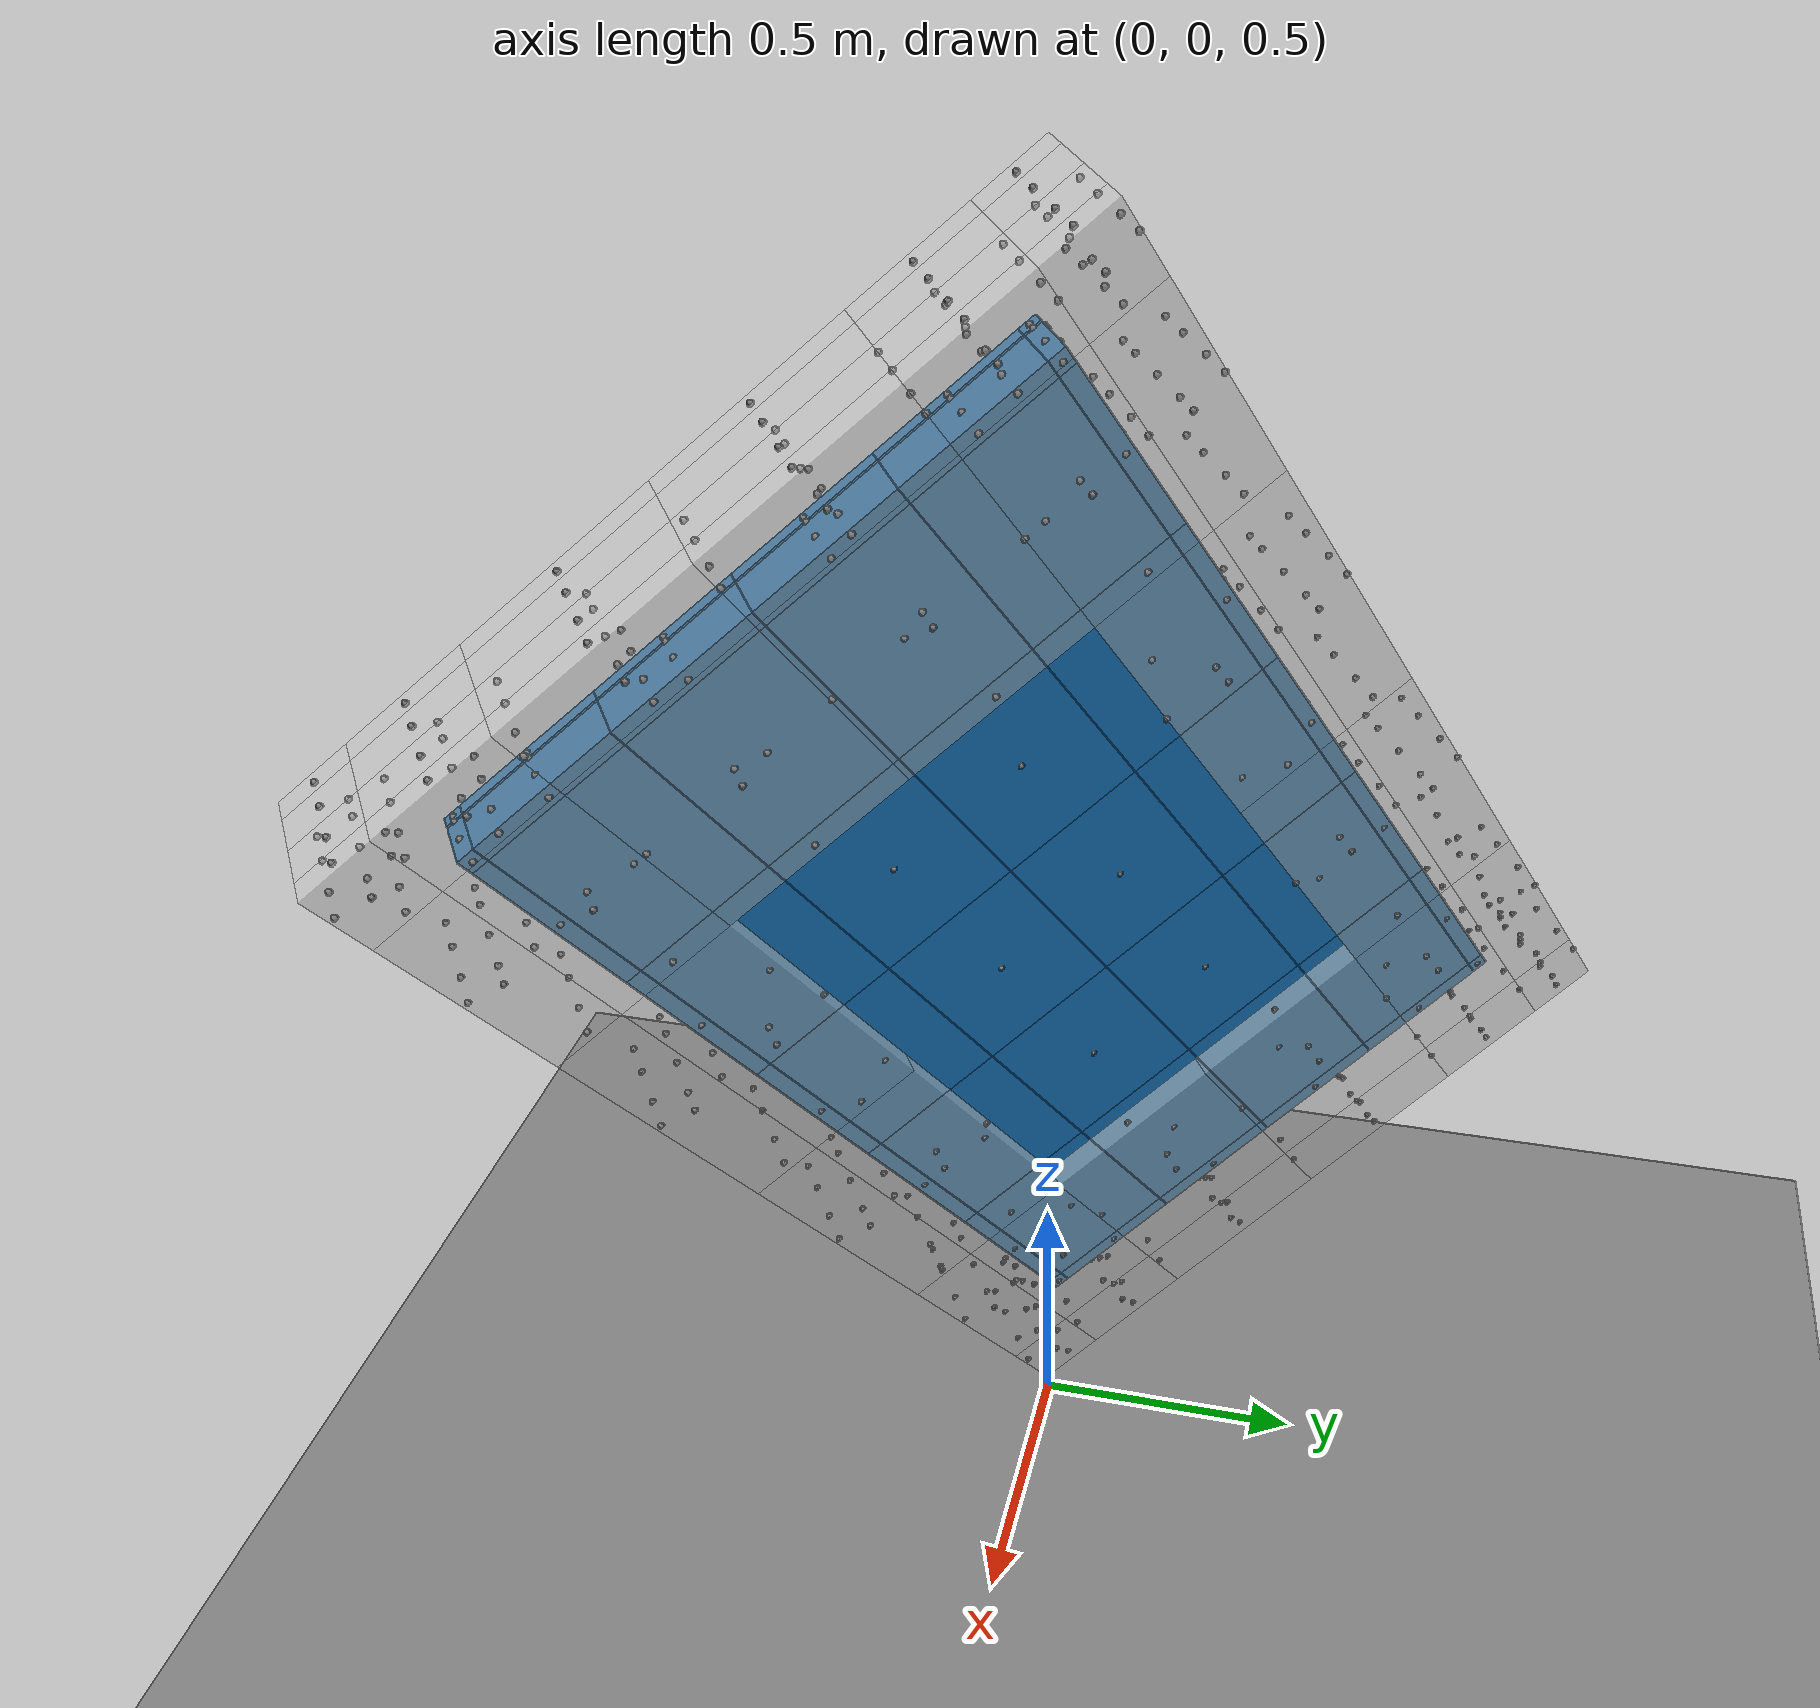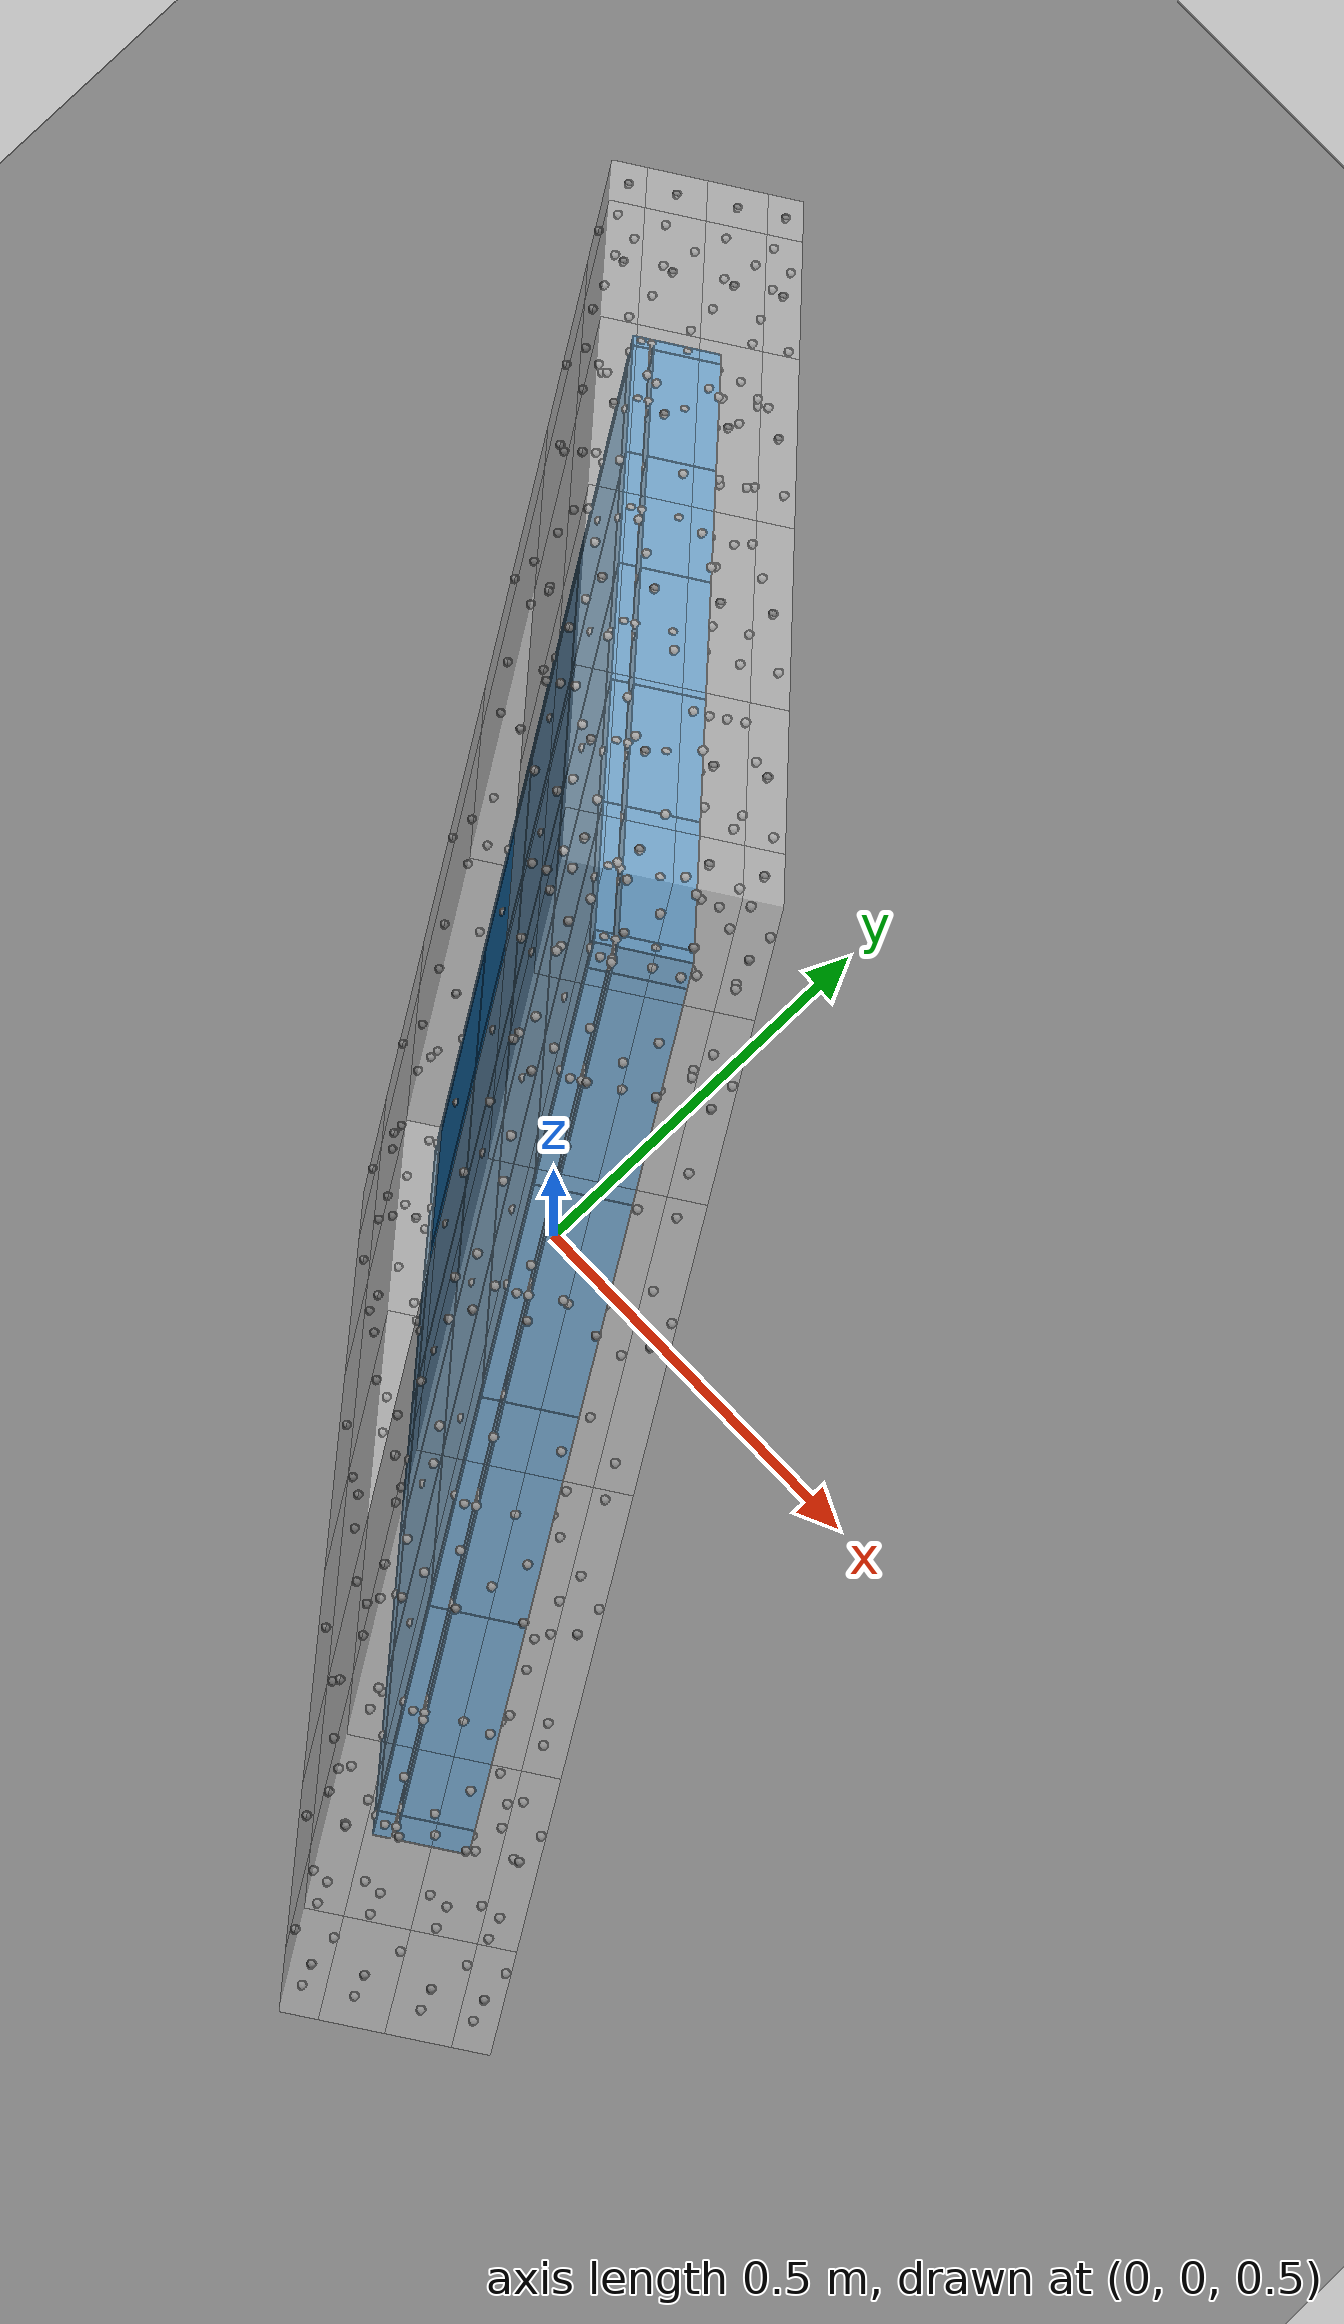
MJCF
<mujoco model="discrete_custom_box">
  <option integrator="implicitfast" timestep="0.001"><flag contact="enable"/></option>
  <default>
    <joint armature="0.05" damping="1.0"/>
    <geom friction="0.8" solref="0.02 1.0" solimp="0.9 0.95 0.001"/>
  </default>
  <worldbody>
    <light pos="0 0 5" dir="0 0 -1"/>
    <geom name="floor" type="plane" size="5 5 0.1" friction="0.8" contype="1" conaffinity="1"/>
    <body name="BPackagingBox" pos="0.00000 0.00000 1.72704" axisangle="0.5735 -0.8192 0.0000 84.1531">
      <freejoint/>
      <geom type="box" size="0.001 0.001 0.001" mass="0.000021" rgba="0.9 0.9 0.9 0.5" contype="2" conaffinity="5" friction="0.8"/>
      <body name="BCushion">
        <body name="b_bcushion_0_0_0" pos="-0.92500 -0.62500 -0.09375">
          <joint type="slide" axis="1 0 0"/>
          <joint type="slide" axis="0 1 0"/>
          <joint type="slide" axis="0 0 1"/>
          <joint type="ball"/>
          <geom type="box" size="0.06500 0.06500 0.02125" mass="0.002468" rgba="0.9 0.9 0.9 0.5" contype="2" conaffinity="5" friction="0.8" solref="0.005 1.5" solimp="0.95 0.99 0.001 0.5 2.0"/>
          <site name="s_BCushion_0_0_0_PX" pos="0.06500 0 0"/>
          <site name="s_BCushion_0_0_0_NX" pos="-0.06500 0 0"/>
          <site name="s_BCushion_0_0_0_PY" pos="0 0.06500 0"/>
          <site name="s_BCushion_0_0_0_NY" pos="0 -0.06500 0"/>
          <site name="s_BCushion_0_0_0_PZ" pos="0 0 0.02125"/>
          <site name="s_BCushion_0_0_0_NZ" pos="0 0 -0.02125"/>
        </body>
        <body name="b_bcushion_0_0_1" pos="-0.92500 -0.62500 -0.03625">
          <joint type="slide" axis="1 0 0"/>
          <joint type="slide" axis="0 1 0"/>
          <joint type="slide" axis="0 0 1"/>
          <joint type="ball"/>
          <geom type="box" size="0.06500 0.06500 0.03625" mass="0.004210" rgba="0.9 0.9 0.9 0.5" contype="2" conaffinity="5" friction="0.8" solref="0.005 1.5" solimp="0.95 0.99 0.001 0.5 2.0"/>
          <site name="s_BCushion_0_0_1_PX" pos="0.06500 0 0"/>
          <site name="s_BCushion_0_0_1_NX" pos="-0.06500 0 0"/>
          <site name="s_BCushion_0_0_1_PY" pos="0 0.06500 0"/>
          <site name="s_BCushion_0_0_1_NY" pos="0 -0.06500 0"/>
          <site name="s_BCushion_0_0_1_PZ" pos="0 0 0.03625"/>
          <site name="s_BCushion_0_0_1_NZ" pos="0 0 -0.03625"/>
        </body>
        <body name="b_bcushion_0_0_2" pos="-0.92500 -0.62500 0.03625">
          <joint type="slide" axis="1 0 0"/>
          <joint type="slide" axis="0 1 0"/>
          <joint type="slide" axis="0 0 1"/>
          <joint type="ball"/>
          <geom type="box" size="0.06500 0.06500 0.03625" mass="0.004210" rgba="0.9 0.9 0.9 0.5" contype="2" conaffinity="5" friction="0.8" solref="0.005 1.5" solimp="0.95 0.99 0.001 0.5 2.0"/>
          <site name="s_BCushion_0_0_2_PX" pos="0.06500 0 0"/>
          <site name="s_BCushion_0_0_2_NX" pos="-0.06500 0 0"/>
          <site name="s_BCushion_0_0_2_PY" pos="0 0.06500 0"/>
          <site name="s_BCushion_0_0_2_NY" pos="0 -0.06500 0"/>
          <site name="s_BCushion_0_0_2_PZ" pos="0 0 0.03625"/>
          <site name="s_BCushion_0_0_2_NZ" pos="0 0 -0.03625"/>
        </body>
        <body name="b_bcushion_0_0_3" pos="-0.92500 -0.62500 0.09375">
          <joint type="slide" axis="1 0 0"/>
          <joint type="slide" axis="0 1 0"/>
          <joint type="slide" axis="0 0 1"/>
          <joint type="ball"/>
          <geom type="box" size="0.06500 0.06500 0.02125" mass="0.002468" rgba="0.9 0.9 0.9 0.5" contype="2" conaffinity="5" friction="0.8" solref="0.005 1.5" solimp="0.95 0.99 0.001 0.5 2.0"/>
          <site name="s_BCushion_0_0_3_PX" pos="0.06500 0 0"/>
          <site name="s_BCushion_0_0_3_NX" pos="-0.06500 0 0"/>
          <site name="s_BCushion_0_0_3_PY" pos="0 0.06500 0"/>
          <site name="s_BCushion_0_0_3_NY" pos="0 -0.06500 0"/>
          <site name="s_BCushion_0_0_3_PZ" pos="0 0 0.02125"/>
          <site name="s_BCushion_0_0_3_NZ" pos="0 0 -0.02125"/>
        </body>
        <body name="b_bcushion_0_1_0" pos="-0.92500 -0.45250 -0.09375">
          <joint type="slide" axis="1 0 0"/>
          <joint type="slide" axis="0 1 0"/>
          <joint type="slide" axis="0 0 1"/>
          <joint type="ball"/>
          <geom type="box" size="0.06500 0.10750 0.02125" mass="0.004081" rgba="0.9 0.9 0.9 0.5" contype="2" conaffinity="5" friction="0.8" solref="0.005 1.5" solimp="0.95 0.99 0.001 0.5 2.0"/>
          <site name="s_BCushion_0_1_0_PX" pos="0.06500 0 0"/>
          <site name="s_BCushion_0_1_0_NX" pos="-0.06500 0 0"/>
          <site name="s_BCushion_0_1_0_PY" pos="0 0.10750 0"/>
          <site name="s_BCushion_0_1_0_NY" pos="0 -0.10750 0"/>
          <site name="s_BCushion_0_1_0_PZ" pos="0 0 0.02125"/>
          <site name="s_BCushion_0_1_0_NZ" pos="0 0 -0.02125"/>
        </body>
        <body name="b_bcushion_0_1_1" pos="-0.92500 -0.45250 -0.03625">
          <joint type="slide" axis="1 0 0"/>
          <joint type="slide" axis="0 1 0"/>
          <joint type="slide" axis="0 0 1"/>
          <joint type="ball"/>
          <geom type="box" size="0.06500 0.10750 0.03625" mass="0.006962" rgba="0.9 0.9 0.9 0.5" contype="2" conaffinity="5" friction="0.8" solref="0.005 1.5" solimp="0.95 0.99 0.001 0.5 2.0"/>
          <site name="s_BCushion_0_1_1_PX" pos="0.06500 0 0"/>
          <site name="s_BCushion_0_1_1_NX" pos="-0.06500 0 0"/>
          <site name="s_BCushion_0_1_1_PY" pos="0 0.10750 0"/>
          <site name="s_BCushion_0_1_1_NY" pos="0 -0.10750 0"/>
          <site name="s_BCushion_0_1_1_PZ" pos="0 0 0.03625"/>
          <site name="s_BCushion_0_1_1_NZ" pos="0 0 -0.03625"/>
        </body>
        <body name="b_bcushion_0_1_2" pos="-0.92500 -0.45250 0.03625">
          <joint type="slide" axis="1 0 0"/>
          <joint type="slide" axis="0 1 0"/>
          <joint type="slide" axis="0 0 1"/>
          <joint type="ball"/>
          <geom type="box" size="0.06500 0.10750 0.03625" mass="0.006962" rgba="0.9 0.9 0.9 0.5" contype="2" conaffinity="5" friction="0.8" solref="0.005 1.5" solimp="0.95 0.99 0.001 0.5 2.0"/>
          <site name="s_BCushion_0_1_2_PX" pos="0.06500 0 0"/>
          <site name="s_BCushion_0_1_2_NX" pos="-0.06500 0 0"/>
          <site name="s_BCushion_0_1_2_PY" pos="0 0.10750 0"/>
          <site name="s_BCushion_0_1_2_NY" pos="0 -0.10750 0"/>
          <site name="s_BCushion_0_1_2_PZ" pos="0 0 0.03625"/>
          <site name="s_BCushion_0_1_2_NZ" pos="0 0 -0.03625"/>
        </body>
        <body name="b_bcushion_0_1_3" pos="-0.92500 -0.45250 0.09375">
          <joint type="slide" axis="1 0 0"/>
          <joint type="slide" axis="0 1 0"/>
          <joint type="slide" axis="0 0 1"/>
          <joint type="ball"/>
          <geom type="box" size="0.06500 0.10750 0.02125" mass="0.004081" rgba="0.9 0.9 0.9 0.5" contype="2" conaffinity="5" friction="0.8" solref="0.005 1.5" solimp="0.95 0.99 0.001 0.5 2.0"/>
          <site name="s_BCushion_0_1_3_PX" pos="0.06500 0 0"/>
          <site name="s_BCushion_0_1_3_NX" pos="-0.06500 0 0"/>
          <site name="s_BCushion_0_1_3_PY" pos="0 0.10750 0"/>
          <site name="s_BCushion_0_1_3_NY" pos="0 -0.10750 0"/>
          <site name="s_BCushion_0_1_3_PZ" pos="0 0 0.02125"/>
          <site name="s_BCushion_0_1_3_NZ" pos="0 0 -0.02125"/>
        </body>
        <body name="b_bcushion_0_2_0" pos="-0.92500 -0.17250 -0.09375">
          <joint type="slide" axis="1 0 0"/>
          <joint type="slide" axis="0 1 0"/>
          <joint type="slide" axis="0 0 1"/>
          <joint type="ball"/>
          <geom type="box" size="0.06500 0.17250 0.02125" mass="0.006549" rgba="0.9 0.9 0.9 0.5" contype="2" conaffinity="5" friction="0.8" solref="0.005 1.5" solimp="0.95 0.99 0.001 0.5 2.0"/>
          <site name="s_BCushion_0_2_0_PX" pos="0.06500 0 0"/>
          <site name="s_BCushion_0_2_0_NX" pos="-0.06500 0 0"/>
          <site name="s_BCushion_0_2_0_PY" pos="0 0.17250 0"/>
          <site name="s_BCushion_0_2_0_NY" pos="0 -0.17250 0"/>
          <site name="s_BCushion_0_2_0_PZ" pos="0 0 0.02125"/>
          <site name="s_BCushion_0_2_0_NZ" pos="0 0 -0.02125"/>
        </body>
        <body name="b_bcushion_0_2_1" pos="-0.92500 -0.17250 -0.03625">
          <joint type="slide" axis="1 0 0"/>
          <joint type="slide" axis="0 1 0"/>
          <joint type="slide" axis="0 0 1"/>
          <joint type="ball"/>
          <geom type="box" size="0.06500 0.17250 0.03625" mass="0.011172" rgba="0.9 0.9 0.9 0.5" contype="2" conaffinity="5" friction="0.8" solref="0.005 1.5" solimp="0.95 0.99 0.001 0.5 2.0"/>
          <site name="s_BCushion_0_2_1_PX" pos="0.06500 0 0"/>
          <site name="s_BCushion_0_2_1_NX" pos="-0.06500 0 0"/>
          <site name="s_BCushion_0_2_1_PY" pos="0 0.17250 0"/>
          <site name="s_BCushion_0_2_1_NY" pos="0 -0.17250 0"/>
          <site name="s_BCushion_0_2_1_PZ" pos="0 0 0.03625"/>
          <site name="s_BCushion_0_2_1_NZ" pos="0 0 -0.03625"/>
        </body>
        <body name="b_bcushion_0_2_2" pos="-0.92500 -0.17250 0.03625">
          <joint type="slide" axis="1 0 0"/>
          <joint type="slide" axis="0 1 0"/>
          <joint type="slide" axis="0 0 1"/>
          <joint type="ball"/>
          <geom type="box" size="0.06500 0.17250 0.03625" mass="0.011172" rgba="0.9 0.9 0.9 0.5" contype="2" conaffinity="5" friction="0.8" solref="0.005 1.5" solimp="0.95 0.99 0.001 0.5 2.0"/>
          <site name="s_BCushion_0_2_2_PX" pos="0.06500 0 0"/>
          <site name="s_BCushion_0_2_2_NX" pos="-0.06500 0 0"/>
          <site name="s_BCushion_0_2_2_PY" pos="0 0.17250 0"/>
          <site name="s_BCushion_0_2_2_NY" pos="0 -0.17250 0"/>
          <site name="s_BCushion_0_2_2_PZ" pos="0 0 0.03625"/>
          <site name="s_BCushion_0_2_2_NZ" pos="0 0 -0.03625"/>
        </body>
        <body name="b_bcushion_0_2_3" pos="-0.92500 -0.17250 0.09375">
          <joint type="slide" axis="1 0 0"/>
          <joint type="slide" axis="0 1 0"/>
          <joint type="slide" axis="0 0 1"/>
          <joint type="ball"/>
          <geom type="box" size="0.06500 0.17250 0.02125" mass="0.006549" rgba="0.9 0.9 0.9 0.5" contype="2" conaffinity="5" friction="0.8" solref="0.005 1.5" solimp="0.95 0.99 0.001 0.5 2.0"/>
          <site name="s_BCushion_0_2_3_PX" pos="0.06500 0 0"/>
          <site name="s_BCushion_0_2_3_NX" pos="-0.06500 0 0"/>
          <site name="s_BCushion_0_2_3_PY" pos="0 0.17250 0"/>
          <site name="s_BCushion_0_2_3_NY" pos="0 -0.17250 0"/>
          <site name="s_BCushion_0_2_3_PZ" pos="0 0 0.02125"/>
          <site name="s_BCushion_0_2_3_NZ" pos="0 0 -0.02125"/>
        </body>
        <body name="b_bcushion_0_3_0" pos="-0.92500 0.17250 -0.09375">
          <joint type="slide" axis="1 0 0"/>
          <joint type="slide" axis="0 1 0"/>
          <joint type="slide" axis="0 0 1"/>
          <joint type="ball"/>
          <geom type="box" size="0.06500 0.17250 0.02125" mass="0.006549" rgba="0.9 0.9 0.9 0.5" contype="2" conaffinity="5" friction="0.8" solref="0.005 1.5" solimp="0.95 0.99 0.001 0.5 2.0"/>
          <site name="s_BCushion_0_3_0_PX" pos="0.06500 0 0"/>
          <site name="s_BCushion_0_3_0_NX" pos="-0.06500 0 0"/>
          <site name="s_BCushion_0_3_0_PY" pos="0 0.17250 0"/>
          <site name="s_BCushion_0_3_0_NY" pos="0 -0.17250 0"/>
          <site name="s_BCushion_0_3_0_PZ" pos="0 0 0.02125"/>
          <site name="s_BCushion_0_3_0_NZ" pos="0 0 -0.02125"/>
        </body>
        <body name="b_bcushion_0_3_1" pos="-0.92500 0.17250 -0.03625">
          <joint type="slide" axis="1 0 0"/>
          <joint type="slide" axis="0 1 0"/>
          <joint type="slide" axis="0 0 1"/>
          <joint type="ball"/>
          <geom type="box" size="0.06500 0.17250 0.03625" mass="0.011172" rgba="0.9 0.9 0.9 0.5" contype="2" conaffinity="5" friction="0.8" solref="0.005 1.5" solimp="0.95 0.99 0.001 0.5 2.0"/>
          <site name="s_BCushion_0_3_1_PX" pos="0.06500 0 0"/>
          <site name="s_BCushion_0_3_1_NX" pos="-0.06500 0 0"/>
          <site name="s_BCushion_0_3_1_PY" pos="0 0.17250 0"/>
          <site name="s_BCushion_0_3_1_NY" pos="0 -0.17250 0"/>
          <site name="s_BCushion_0_3_1_PZ" pos="0 0 0.03625"/>
          <site name="s_BCushion_0_3_1_NZ" pos="0 0 -0.03625"/>
        </body>
        <body name="b_bcushion_0_3_2" pos="-0.92500 0.17250 0.03625">
          <joint type="slide" axis="1 0 0"/>
          <joint type="slide" axis="0 1 0"/>
          <joint type="slide" axis="0 0 1"/>
          <joint type="ball"/>
          <geom type="box" size="0.06500 0.17250 0.03625" mass="0.011172" rgba="0.9 0.9 0.9 0.5" contype="2" conaffinity="5" friction="0.8" solref="0.005 1.5" solimp="0.95 0.99 0.001 0.5 2.0"/>
          <site name="s_BCushion_0_3_2_PX" pos="0.06500 0 0"/>
          <site name="s_BCushion_0_3_2_NX" pos="-0.06500 0 0"/>
          <site name="s_BCushion_0_3_2_PY" pos="0 0.17250 0"/>
          <site name="s_BCushion_0_3_2_NY" pos="0 -0.17250 0"/>
          <site name="s_BCushion_0_3_2_PZ" pos="0 0 0.03625"/>
          <site name="s_BCushion_0_3_2_NZ" pos="0 0 -0.03625"/>
        </body>
        <body name="b_bcushion_0_3_3" pos="-0.92500 0.17250 0.09375">
          <joint type="slide" axis="1 0 0"/>
          <joint type="slide" axis="0 1 0"/>
          <joint type="slide" axis="0 0 1"/>
          <joint type="ball"/>
          <geom type="box" size="0.06500 0.17250 0.02125" mass="0.006549" rgba="0.9 0.9 0.9 0.5" contype="2" conaffinity="5" friction="0.8" solref="0.005 1.5" solimp="0.95 0.99 0.001 0.5 2.0"/>
          <site name="s_BCushion_0_3_3_PX" pos="0.06500 0 0"/>
          <site name="s_BCushion_0_3_3_NX" pos="-0.06500 0 0"/>
          <site name="s_BCushion_0_3_3_PY" pos="0 0.17250 0"/>
          <site name="s_BCushion_0_3_3_NY" pos="0 -0.17250 0"/>
          <site name="s_BCushion_0_3_3_PZ" pos="0 0 0.02125"/>
          <site name="s_BCushion_0_3_3_NZ" pos="0 0 -0.02125"/>
        </body>
        <body name="b_bcushion_0_4_0" pos="-0.92500 0.45250 -0.09375">
          <joint type="slide" axis="1 0 0"/>
          <joint type="slide" axis="0 1 0"/>
          <joint type="slide" axis="0 0 1"/>
          <joint type="ball"/>
          <geom type="box" size="0.06500 0.10750 0.02125" mass="0.004081" rgba="0.9 0.9 0.9 0.5" contype="2" conaffinity="5" friction="0.8" solref="0.005 1.5" solimp="0.95 0.99 0.001 0.5 2.0"/>
          <site name="s_BCushion_0_4_0_PX" pos="0.06500 0 0"/>
          <site name="s_BCushion_0_4_0_NX" pos="-0.06500 0 0"/>
          <site name="s_BCushion_0_4_0_PY" pos="0 0.10750 0"/>
          <site name="s_BCushion_0_4_0_NY" pos="0 -0.10750 0"/>
          <site name="s_BCushion_0_4_0_PZ" pos="0 0 0.02125"/>
          <site name="s_BCushion_0_4_0_NZ" pos="0 0 -0.02125"/>
        </body>
        <body name="b_bcushion_0_4_1" pos="-0.92500 0.45250 -0.03625">
          <joint type="slide" axis="1 0 0"/>
          <joint type="slide" axis="0 1 0"/>
          <joint type="slide" axis="0 0 1"/>
          <joint type="ball"/>
          <geom type="box" size="0.06500 0.10750 0.03625" mass="0.006962" rgba="0.9 0.9 0.9 0.5" contype="2" conaffinity="5" friction="0.8" solref="0.005 1.5" solimp="0.95 0.99 0.001 0.5 2.0"/>
          <site name="s_BCushion_0_4_1_PX" pos="0.06500 0 0"/>
          <site name="s_BCushion_0_4_1_NX" pos="-0.06500 0 0"/>
          <site name="s_BCushion_0_4_1_PY" pos="0 0.10750 0"/>
          <site name="s_BCushion_0_4_1_NY" pos="0 -0.10750 0"/>
          <site name="s_BCushion_0_4_1_PZ" pos="0 0 0.03625"/>
          <site name="s_BCushion_0_4_1_NZ" pos="0 0 -0.03625"/>
        </body>
        <body name="b_bcushion_0_4_2" pos="-0.92500 0.45250 0.03625">
          <joint type="slide" axis="1 0 0"/>
          <joint type="slide" axis="0 1 0"/>
          <joint type="slide" axis="0 0 1"/>
          <joint type="ball"/>
          <geom type="box" size="0.06500 0.10750 0.03625" mass="0.006962" rgba="0.9 0.9 0.9 0.5" contype="2" conaffinity="5" friction="0.8" solref="0.005 1.5" solimp="0.95 0.99 0.001 0.5 2.0"/>
          <site name="s_BCushion_0_4_2_PX" pos="0.06500 0 0"/>
          <site name="s_BCushion_0_4_2_NX" pos="-0.06500 0 0"/>
          <site name="s_BCushion_0_4_2_PY" pos="0 0.10750 0"/>
          <site name="s_BCushion_0_4_2_NY" pos="0 -0.10750 0"/>
          <site name="s_BCushion_0_4_2_PZ" pos="0 0 0.03625"/>
          <site name="s_BCushion_0_4_2_NZ" pos="0 0 -0.03625"/>
        </body>
        <body name="b_bcushion_0_4_3" pos="-0.92500 0.45250 0.09375">
          <joint type="slide" axis="1 0 0"/>
          <joint type="slide" axis="0 1 0"/>
          <joint type="slide" axis="0 0 1"/>
          <joint type="ball"/>
          <geom type="box" size="0.06500 0.10750 0.02125" mass="0.004081" rgba="0.9 0.9 0.9 0.5" contype="2" conaffinity="5" friction="0.8" solref="0.005 1.5" solimp="0.95 0.99 0.001 0.5 2.0"/>
          <site name="s_BCushion_0_4_3_PX" pos="0.06500 0 0"/>
          <site name="s_BCushion_0_4_3_NX" pos="-0.06500 0 0"/>
          <site name="s_BCushion_0_4_3_PY" pos="0 0.10750 0"/>
          <site name="s_BCushion_0_4_3_NY" pos="0 -0.10750 0"/>
          <site name="s_BCushion_0_4_3_PZ" pos="0 0 0.02125"/>
          <site name="s_BCushion_0_4_3_NZ" pos="0 0 -0.02125"/>
        </body>
        <body name="b_bcushion_0_5_0" pos="-0.92500 0.62500 -0.09375">
          <joint type="slide" axis="1 0 0"/>
          <joint type="slide" axis="0 1 0"/>
          <joint type="slide" axis="0 0 1"/>
          <joint type="ball"/>
          <geom type="box" size="0.06500 0.06500 0.02125" mass="0.002468" rgba="0.9 0.9 0.9 0.5" contype="2" conaffinity="5" friction="0.8" solref="0.005 1.5" solimp="0.95 0.99 0.001 0.5 2.0"/>
          <site name="s_BCushion_0_5_0_PX" pos="0.06500 0 0"/>
          <site name="s_BCushion_0_5_0_NX" pos="-0.06500 0 0"/>
          <site name="s_BCushion_0_5_0_PY" pos="0 0.06500 0"/>
          <site name="s_BCushion_0_5_0_NY" pos="0 -0.06500 0"/>
          <site name="s_BCushion_0_5_0_PZ" pos="0 0 0.02125"/>
          <site name="s_BCushion_0_5_0_NZ" pos="0 0 -0.02125"/>
        </body>
        <body name="b_bcushion_0_5_1" pos="-0.92500 0.62500 -0.03625">
          <joint type="slide" axis="1 0 0"/>
          <joint type="slide" axis="0 1 0"/>
          <joint type="slide" axis="0 0 1"/>
          <joint type="ball"/>
          <geom type="box" size="0.06500 0.06500 0.03625" mass="0.004210" rgba="0.9 0.9 0.9 0.5" contype="2" conaffinity="5" friction="0.8" solref="0.005 1.5" solimp="0.95 0.99 0.001 0.5 2.0"/>
          <site name="s_BCushion_0_5_1_PX" pos="0.06500 0 0"/>
          <site name="s_BCushion_0_5_1_NX" pos="-0.06500 0 0"/>
          <site name="s_BCushion_0_5_1_PY" pos="0 0.06500 0"/>
          <site name="s_BCushion_0_5_1_NY" pos="0 -0.06500 0"/>
          <site name="s_BCushion_0_5_1_PZ" pos="0 0 0.03625"/>
          <site name="s_BCushion_0_5_1_NZ" pos="0 0 -0.03625"/>
        </body>
        <body name="b_bcushion_0_5_2" pos="-0.92500 0.62500 0.03625">
          <joint type="slide" axis="1 0 0"/>
          <joint type="slide" axis="0 1 0"/>
          <joint type="slide" axis="0 0 1"/>
          <joint type="ball"/>
          <geom type="box" size="0.06500 0.06500 0.03625" mass="0.004210" rgba="0.9 0.9 0.9 0.5" contype="2" conaffinity="5" friction="0.8" solref="0.005 1.5" solimp="0.95 0.99 0.001 0.5 2.0"/>
          <site name="s_BCushion_0_5_2_PX" pos="0.06500 0 0"/>
          <site name="s_BCushion_0_5_2_NX" pos="-0.06500 0 0"/>
          <site name="s_BCushion_0_5_2_PY" pos="0 0.06500 0"/>
          <site name="s_BCushion_0_5_2_NY" pos="0 -0.06500 0"/>
          <site name="s_BCushion_0_5_2_PZ" pos="0 0 0.03625"/>
          <site name="s_BCushion_0_5_2_NZ" pos="0 0 -0.03625"/>
        </body>
        <body name="b_bcushion_0_5_3" pos="-0.92500 0.62500 0.09375">
          <joint type="slide" axis="1 0 0"/>
          <joint type="slide" axis="0 1 0"/>
          <joint type="slide" axis="0 0 1"/>
          <joint type="ball"/>
          <geom type="box" size="0.06500 0.06500 0.02125" mass="0.002468" rgba="0.9 0.9 0.9 0.5" contype="2" conaffinity="5" friction="0.8" solref="0.005 1.5" solimp="0.95 0.99 0.001 0.5 2.0"/>
          <site name="s_BCushion_0_5_3_PX" pos="0.06500 0 0"/>
          <site name="s_BCushion_0_5_3_NX" pos="-0.06500 0 0"/>
          <site name="s_BCushion_0_5_3_PY" pos="0 0.06500 0"/>
          <site name="s_BCushion_0_5_3_NY" pos="0 -0.06500 0"/>
          <site name="s_BCushion_0_5_3_PZ" pos="0 0 0.02125"/>
          <site name="s_BCushion_0_5_3_NZ" pos="0 0 -0.02125"/>
        </body>
        <body name="b_bcushion_1_0_0" pos="-0.67750 -0.62500 -0.09375">
          <joint type="slide" axis="1 0 0"/>
          <joint type="slide" axis="0 1 0"/>
          <joint type="slide" axis="0 0 1"/>
          <joint type="ball"/>
          <geom type="box" size="0.18250 0.06500 0.02125" mass="0.006929" rgba="0.9 0.9 0.9 0.5" contype="2" conaffinity="5" friction="0.8" solref="0.005 1.5" solimp="0.95 0.99 0.001 0.5 2.0"/>
          <site name="s_BCushion_1_0_0_PX" pos="0.18250 0 0"/>
          <site name="s_BCushion_1_0_0_NX" pos="-0.18250 0 0"/>
          <site name="s_BCushion_1_0_0_PY" pos="0 0.06500 0"/>
          <site name="s_BCushion_1_0_0_NY" pos="0 -0.06500 0"/>
          <site name="s_BCushion_1_0_0_PZ" pos="0 0 0.02125"/>
          <site name="s_BCushion_1_0_0_NZ" pos="0 0 -0.02125"/>
        </body>
        <body name="b_bcushion_1_0_1" pos="-0.67750 -0.62500 -0.03625">
          <joint type="slide" axis="1 0 0"/>
          <joint type="slide" axis="0 1 0"/>
          <joint type="slide" axis="0 0 1"/>
          <joint type="ball"/>
          <geom type="box" size="0.18250 0.06500 0.03625" mass="0.011819" rgba="0.9 0.9 0.9 0.5" contype="2" conaffinity="5" friction="0.8" solref="0.005 1.5" solimp="0.95 0.99 0.001 0.5 2.0"/>
          <site name="s_BCushion_1_0_1_PX" pos="0.18250 0 0"/>
          <site name="s_BCushion_1_0_1_NX" pos="-0.18250 0 0"/>
          <site name="s_BCushion_1_0_1_PY" pos="0 0.06500 0"/>
          <site name="s_BCushion_1_0_1_NY" pos="0 -0.06500 0"/>
          <site name="s_BCushion_1_0_1_PZ" pos="0 0 0.03625"/>
          <site name="s_BCushion_1_0_1_NZ" pos="0 0 -0.03625"/>
        </body>
        <body name="b_bcushion_1_0_2" pos="-0.67750 -0.62500 0.03625">
          <joint type="slide" axis="1 0 0"/>
          <joint type="slide" axis="0 1 0"/>
          <joint type="slide" axis="0 0 1"/>
          <joint type="ball"/>
          <geom type="box" size="0.18250 0.06500 0.03625" mass="0.011819" rgba="0.9 0.9 0.9 0.5" contype="2" conaffinity="5" friction="0.8" solref="0.005 1.5" solimp="0.95 0.99 0.001 0.5 2.0"/>
          <site name="s_BCushion_1_0_2_PX" pos="0.18250 0 0"/>
          <site name="s_BCushion_1_0_2_NX" pos="-0.18250 0 0"/>
          <site name="s_BCushion_1_0_2_PY" pos="0 0.06500 0"/>
          <site name="s_BCushion_1_0_2_NY" pos="0 -0.06500 0"/>
          <site name="s_BCushion_1_0_2_PZ" pos="0 0 0.03625"/>
          <site name="s_BCushion_1_0_2_NZ" pos="0 0 -0.03625"/>
        </body>
        <body name="b_bcushion_1_0_3" pos="-0.67750 -0.62500 0.09375">
          <joint type="slide" axis="1 0 0"/>
          <joint type="slide" axis="0 1 0"/>
          <joint type="slide" axis="0 0 1"/>
          <joint type="ball"/>
          <geom type="box" size="0.18250 0.06500 0.02125" mass="0.006929" rgba="0.9 0.9 0.9 0.5" contype="2" conaffinity="5" friction="0.8" solref="0.005 1.5" solimp="0.95 0.99 0.001 0.5 2.0"/>
          <site name="s_BCushion_1_0_3_PX" pos="0.18250 0 0"/>
          <site name="s_BCushion_1_0_3_NX" pos="-0.18250 0 0"/>
          <site name="s_BCushion_1_0_3_PY" pos="0 0.06500 0"/>
          <site name="s_BCushion_1_0_3_NY" pos="0 -0.06500 0"/>
          <site name="s_BCushion_1_0_3_PZ" pos="0 0 0.02125"/>
          <site name="s_BCushion_1_0_3_NZ" pos="0 0 -0.02125"/>
        </body>
        <body name="b_bcushion_1_1_0" pos="-0.67750 -0.45250 -0.09375">
          <joint type="slide" axis="1 0 0"/>
          <joint type="slide" axis="0 1 0"/>
          <joint type="slide" axis="0 0 1"/>
          <joint type="ball"/>
          <geom type="box" size="0.18250 0.10750 0.02125" mass="0.011459" rgba="0.9 0.9 0.9 0.5" contype="2" conaffinity="5" friction="0.8" solref="0.005 1.5" solimp="0.95 0.99 0.001 0.5 2.0"/>
          <site name="s_BCushion_1_1_0_PX" pos="0.18250 0 0"/>
          <site name="s_BCushion_1_1_0_NX" pos="-0.18250 0 0"/>
          <site name="s_BCushion_1_1_0_PY" pos="0 0.10750 0"/>
          <site name="s_BCushion_1_1_0_NY" pos="0 -0.10750 0"/>
          <site name="s_BCushion_1_1_0_PZ" pos="0 0 0.02125"/>
          <site name="s_BCushion_1_1_0_NZ" pos="0 0 -0.02125"/>
        </body>
        <body name="b_bcushion_1_1_3" pos="-0.67750 -0.45250 0.09375">
          <joint type="slide" axis="1 0 0"/>
          <joint type="slide" axis="0 1 0"/>
          <joint type="slide" axis="0 0 1"/>
          <joint type="ball"/>
          <geom type="box" size="0.18250 0.10750 0.02125" mass="0.011459" rgba="0.9 0.9 0.9 0.5" contype="2" conaffinity="5" friction="0.8" solref="0.005 1.5" solimp="0.95 0.99 0.001 0.5 2.0"/>
          <site name="s_BCushion_1_1_3_PX" pos="0.18250 0 0"/>
          <site name="s_BCushion_1_1_3_NX" pos="-0.18250 0 0"/>
          <site name="s_BCushion_1_1_3_PY" pos="0 0.10750 0"/>
          <site name="s_BCushion_1_1_3_NY" pos="0 -0.10750 0"/>
          <site name="s_BCushion_1_1_3_PZ" pos="0 0 0.02125"/>
          <site name="s_BCushion_1_1_3_NZ" pos="0 0 -0.02125"/>
        </body>
        <body name="b_bcushion_1_2_0" pos="-0.67750 -0.17250 -0.09375">
          <joint type="slide" axis="1 0 0"/>
          <joint type="slide" axis="0 1 0"/>
          <joint type="slide" axis="0 0 1"/>
          <joint type="ball"/>
          <geom type="box" size="0.18250 0.17250 0.02125" mass="0.018387" rgba="0.9 0.9 0.9 0.5" contype="2" conaffinity="5" friction="0.8" solref="0.005 1.5" solimp="0.95 0.99 0.001 0.5 2.0"/>
          <site name="s_BCushion_1_2_0_PX" pos="0.18250 0 0"/>
          <site name="s_BCushion_1_2_0_NX" pos="-0.18250 0 0"/>
          <site name="s_BCushion_1_2_0_PY" pos="0 0.17250 0"/>
          <site name="s_BCushion_1_2_0_NY" pos="0 -0.17250 0"/>
          <site name="s_BCushion_1_2_0_PZ" pos="0 0 0.02125"/>
          <site name="s_BCushion_1_2_0_NZ" pos="0 0 -0.02125"/>
        </body>
        <body name="b_bcushion_1_2_3" pos="-0.67750 -0.17250 0.09375">
          <joint type="slide" axis="1 0 0"/>
          <joint type="slide" axis="0 1 0"/>
          <joint type="slide" axis="0 0 1"/>
          <joint type="ball"/>
          <geom type="box" size="0.18250 0.17250 0.02125" mass="0.018387" rgba="0.9 0.9 0.9 0.5" contype="2" conaffinity="5" friction="0.8" solref="0.005 1.5" solimp="0.95 0.99 0.001 0.5 2.0"/>
          <site name="s_BCushion_1_2_3_PX" pos="0.18250 0 0"/>
          <site name="s_BCushion_1_2_3_NX" pos="-0.18250 0 0"/>
          <site name="s_BCushion_1_2_3_PY" pos="0 0.17250 0"/>
          <site name="s_BCushion_1_2_3_NY" pos="0 -0.17250 0"/>
          <site name="s_BCushion_1_2_3_PZ" pos="0 0 0.02125"/>
          <site name="s_BCushion_1_2_3_NZ" pos="0 0 -0.02125"/>
        </body>
        <body name="b_bcushion_1_3_0" pos="-0.67750 0.17250 -0.09375">
          <joint type="slide" axis="1 0 0"/>
          <joint type="slide" axis="0 1 0"/>
          <joint type="slide" axis="0 0 1"/>
          <joint type="ball"/>
          <geom type="box" size="0.18250 0.17250 0.02125" mass="0.018387" rgba="0.9 0.9 0.9 0.5" contype="2" conaffinity="5" friction="0.8" solref="0.005 1.5" solimp="0.95 0.99 0.001 0.5 2.0"/>
          <site name="s_BCushion_1_3_0_PX" pos="0.18250 0 0"/>
          <site name="s_BCushion_1_3_0_NX" pos="-0.18250 0 0"/>
          <site name="s_BCushion_1_3_0_PY" pos="0 0.17250 0"/>
          <site name="s_BCushion_1_3_0_NY" pos="0 -0.17250 0"/>
          <site name="s_BCushion_1_3_0_PZ" pos="0 0 0.02125"/>
          <site name="s_BCushion_1_3_0_NZ" pos="0 0 -0.02125"/>
        </body>
        <body name="b_bcushion_1_3_3" pos="-0.67750 0.17250 0.09375">
          <joint type="slide" axis="1 0 0"/>
          <joint type="slide" axis="0 1 0"/>
          <joint type="slide" axis="0 0 1"/>
          <joint type="ball"/>
          <geom type="box" size="0.18250 0.17250 0.02125" mass="0.018387" rgba="0.9 0.9 0.9 0.5" contype="2" conaffinity="5" friction="0.8" solref="0.005 1.5" solimp="0.95 0.99 0.001 0.5 2.0"/>
          <site name="s_BCushion_1_3_3_PX" pos="0.18250 0 0"/>
          <site name="s_BCushion_1_3_3_NX" pos="-0.18250 0 0"/>
          <site name="s_BCushion_1_3_3_PY" pos="0 0.17250 0"/>
          <site name="s_BCushion_1_3_3_NY" pos="0 -0.17250 0"/>
          <site name="s_BCushion_1_3_3_PZ" pos="0 0 0.02125"/>
          <site name="s_BCushion_1_3_3_NZ" pos="0 0 -0.02125"/>
        </body>
        <body name="b_bcushion_1_4_0" pos="-0.67750 0.45250 -0.09375">
          <joint type="slide" axis="1 0 0"/>
          <joint type="slide" axis="0 1 0"/>
          <joint type="slide" axis="0 0 1"/>
          <joint type="ball"/>
          <geom type="box" size="0.18250 0.10750 0.02125" mass="0.011459" rgba="0.9 0.9 0.9 0.5" contype="2" conaffinity="5" friction="0.8" solref="0.005 1.5" solimp="0.95 0.99 0.001 0.5 2.0"/>
          <site name="s_BCushion_1_4_0_PX" pos="0.18250 0 0"/>
          <site name="s_BCushion_1_4_0_NX" pos="-0.18250 0 0"/>
          <site name="s_BCushion_1_4_0_PY" pos="0 0.10750 0"/>
          <site name="s_BCushion_1_4_0_NY" pos="0 -0.10750 0"/>
          <site name="s_BCushion_1_4_0_PZ" pos="0 0 0.02125"/>
          <site name="s_BCushion_1_4_0_NZ" pos="0 0 -0.02125"/>
        </body>
        <body name="b_bcushion_1_4_3" pos="-0.67750 0.45250 0.09375">
          <joint type="slide" axis="1 0 0"/>
          <joint type="slide" axis="0 1 0"/>
          <joint type="slide" axis="0 0 1"/>
          <joint type="ball"/>
          <geom type="box" size="0.18250 0.10750 0.02125" mass="0.011459" rgba="0.9 0.9 0.9 0.5" contype="2" conaffinity="5" friction="0.8" solref="0.005 1.5" solimp="0.95 0.99 0.001 0.5 2.0"/>
          <site name="s_BCushion_1_4_3_PX" pos="0.18250 0 0"/>
          <site name="s_BCushion_1_4_3_NX" pos="-0.18250 0 0"/>
          <site name="s_BCushion_1_4_3_PY" pos="0 0.10750 0"/>
          <site name="s_BCushion_1_4_3_NY" pos="0 -0.10750 0"/>
          <site name="s_BCushion_1_4_3_PZ" pos="0 0 0.02125"/>
          <site name="s_BCushion_1_4_3_NZ" pos="0 0 -0.02125"/>
        </body>
        <body name="b_bcushion_1_5_0" pos="-0.67750 0.62500 -0.09375">
          <joint type="slide" axis="1 0 0"/>
          <joint type="slide" axis="0 1 0"/>
          <joint type="slide" axis="0 0 1"/>
          <joint type="ball"/>
          <geom type="box" size="0.18250 0.06500 0.02125" mass="0.006929" rgba="0.9 0.9 0.9 0.5" contype="2" conaffinity="5" friction="0.8" solref="0.005 1.5" solimp="0.95 0.99 0.001 0.5 2.0"/>
          <site name="s_BCushion_1_5_0_PX" pos="0.18250 0 0"/>
          <site name="s_BCushion_1_5_0_NX" pos="-0.18250 0 0"/>
          <site name="s_BCushion_1_5_0_PY" pos="0 0.06500 0"/>
          <site name="s_BCushion_1_5_0_NY" pos="0 -0.06500 0"/>
          <site name="s_BCushion_1_5_0_PZ" pos="0 0 0.02125"/>
          <site name="s_BCushion_1_5_0_NZ" pos="0 0 -0.02125"/>
        </body>
        <body name="b_bcushion_1_5_1" pos="-0.67750 0.62500 -0.03625">
          <joint type="slide" axis="1 0 0"/>
          <joint type="slide" axis="0 1 0"/>
          <joint type="slide" axis="0 0 1"/>
          <joint type="ball"/>
          <geom type="box" size="0.18250 0.06500 0.03625" mass="0.011819" rgba="0.9 0.9 0.9 0.5" contype="2" conaffinity="5" friction="0.8" solref="0.005 1.5" solimp="0.95 0.99 0.001 0.5 2.0"/>
          <site name="s_BCushion_1_5_1_PX" pos="0.18250 0 0"/>
          <site name="s_BCushion_1_5_1_NX" pos="-0.18250 0 0"/>
          <site name="s_BCushion_1_5_1_PY" pos="0 0.06500 0"/>
          <site name="s_BCushion_1_5_1_NY" pos="0 -0.06500 0"/>
          <site name="s_BCushion_1_5_1_PZ" pos="0 0 0.03625"/>
          <site name="s_BCushion_1_5_1_NZ" pos="0 0 -0.03625"/>
        </body>
        <body name="b_bcushion_1_5_2" pos="-0.67750 0.62500 0.03625">
          <joint type="slide" axis="1 0 0"/>
          <joint type="slide" axis="0 1 0"/>
          <joint type="slide" axis="0 0 1"/>
          <joint type="ball"/>
          <geom type="box" size="0.18250 0.06500 0.03625" mass="0.011819" rgba="0.9 0.9 0.9 0.5" contype="2" conaffinity="5" friction="0.8" solref="0.005 1.5" solimp="0.95 0.99 0.001 0.5 2.0"/>
          <site name="s_BCushion_1_5_2_PX" pos="0.18250 0 0"/>
          <site name="s_BCushion_1_5_2_NX" pos="-0.18250 0 0"/>
          <site name="s_BCushion_1_5_2_PY" pos="0 0.06500 0"/>
          <site name="s_BCushion_1_5_2_NY" pos="0 -0.06500 0"/>
          <site name="s_BCushion_1_5_2_PZ" pos="0 0 0.03625"/>
          <site name="s_BCushion_1_5_2_NZ" pos="0 0 -0.03625"/>
        </body>
        <body name="b_bcushion_1_5_3" pos="-0.67750 0.62500 0.09375">
          <joint type="slide" axis="1 0 0"/>
          <joint type="slide" axis="0 1 0"/>
          <joint type="slide" axis="0 0 1"/>
          <joint type="ball"/>
          <geom type="box" size="0.18250 0.06500 0.02125" mass="0.006929" rgba="0.9 0.9 0.9 0.5" contype="2" conaffinity="5" friction="0.8" solref="0.005 1.5" solimp="0.95 0.99 0.001 0.5 2.0"/>
          <site name="s_BCushion_1_5_3_PX" pos="0.18250 0 0"/>
          <site name="s_BCushion_1_5_3_NX" pos="-0.18250 0 0"/>
          <site name="s_BCushion_1_5_3_PY" pos="0 0.06500 0"/>
          <site name="s_BCushion_1_5_3_NY" pos="0 -0.06500 0"/>
          <site name="s_BCushion_1_5_3_PZ" pos="0 0 0.02125"/>
          <site name="s_BCushion_1_5_3_NZ" pos="0 0 -0.02125"/>
        </body>
        <body name="b_bcushion_2_0_0" pos="-0.24750 -0.62500 -0.09375">
          <joint type="slide" axis="1 0 0"/>
          <joint type="slide" axis="0 1 0"/>
          <joint type="slide" axis="0 0 1"/>
          <joint type="ball"/>
          <geom type="box" size="0.24750 0.06500 0.02125" mass="0.009396" rgba="0.9 0.9 0.9 0.5" contype="2" conaffinity="5" friction="0.8" solref="0.005 1.5" solimp="0.95 0.99 0.001 0.5 2.0"/>
          <site name="s_BCushion_2_0_0_PX" pos="0.24750 0 0"/>
          <site name="s_BCushion_2_0_0_NX" pos="-0.24750 0 0"/>
          <site name="s_BCushion_2_0_0_PY" pos="0 0.06500 0"/>
          <site name="s_BCushion_2_0_0_NY" pos="0 -0.06500 0"/>
          <site name="s_BCushion_2_0_0_PZ" pos="0 0 0.02125"/>
          <site name="s_BCushion_2_0_0_NZ" pos="0 0 -0.02125"/>
        </body>
        <body name="b_bcushion_2_0_1" pos="-0.24750 -0.62500 -0.03625">
          <joint type="slide" axis="1 0 0"/>
          <joint type="slide" axis="0 1 0"/>
          <joint type="slide" axis="0 0 1"/>
          <joint type="ball"/>
          <geom type="box" size="0.24750 0.06500 0.03625" mass="0.016029" rgba="0.9 0.9 0.9 0.5" contype="2" conaffinity="5" friction="0.8" solref="0.005 1.5" solimp="0.95 0.99 0.001 0.5 2.0"/>
          <site name="s_BCushion_2_0_1_PX" pos="0.24750 0 0"/>
          <site name="s_BCushion_2_0_1_NX" pos="-0.24750 0 0"/>
          <site name="s_BCushion_2_0_1_PY" pos="0 0.06500 0"/>
          <site name="s_BCushion_2_0_1_NY" pos="0 -0.06500 0"/>
          <site name="s_BCushion_2_0_1_PZ" pos="0 0 0.03625"/>
          <site name="s_BCushion_2_0_1_NZ" pos="0 0 -0.03625"/>
        </body>
        <body name="b_bcushion_2_0_2" pos="-0.24750 -0.62500 0.03625">
          <joint type="slide" axis="1 0 0"/>
          <joint type="slide" axis="0 1 0"/>
          <joint type="slide" axis="0 0 1"/>
          <joint type="ball"/>
          <geom type="box" size="0.24750 0.06500 0.03625" mass="0.016029" rgba="0.9 0.9 0.9 0.5" contype="2" conaffinity="5" friction="0.8" solref="0.005 1.5" solimp="0.95 0.99 0.001 0.5 2.0"/>
          <site name="s_BCushion_2_0_2_PX" pos="0.24750 0 0"/>
          <site name="s_BCushion_2_0_2_NX" pos="-0.24750 0 0"/>
          <site name="s_BCushion_2_0_2_PY" pos="0 0.06500 0"/>
          <site name="s_BCushion_2_0_2_NY" pos="0 -0.06500 0"/>
          <site name="s_BCushion_2_0_2_PZ" pos="0 0 0.03625"/>
          <site name="s_BCushion_2_0_2_NZ" pos="0 0 -0.03625"/>
        </body>
        <body name="b_bcushion_2_0_3" pos="-0.24750 -0.62500 0.09375">
          <joint type="slide" axis="1 0 0"/>
          <joint type="slide" axis="0 1 0"/>
          <joint type="slide" axis="0 0 1"/>
          <joint type="ball"/>
          <geom type="box" size="0.24750 0.06500 0.02125" mass="0.009396" rgba="0.9 0.9 0.9 0.5" contype="2" conaffinity="5" friction="0.8" solref="0.005 1.5" solimp="0.95 0.99 0.001 0.5 2.0"/>
          <site name="s_BCushion_2_0_3_PX" pos="0.24750 0 0"/>
          <site name="s_BCushion_2_0_3_NX" pos="-0.24750 0 0"/>
          <site name="s_BCushion_2_0_3_PY" pos="0 0.06500 0"/>
          <site name="s_BCushion_2_0_3_NY" pos="0 -0.06500 0"/>
          <site name="s_BCushion_2_0_3_PZ" pos="0 0 0.02125"/>
          <site name="s_BCushion_2_0_3_NZ" pos="0 0 -0.02125"/>
        </body>
        <body name="b_bcushion_2_1_0" pos="-0.24750 -0.45250 -0.09375">
          <joint type="slide" axis="1 0 0"/>
          <joint type="slide" axis="0 1 0"/>
          <joint type="slide" axis="0 0 1"/>
          <joint type="ball"/>
          <geom type="box" size="0.24750 0.10750 0.02125" mass="0.015540" rgba="0.9 0.9 0.9 0.5" contype="2" conaffinity="5" friction="0.8" solref="0.005 1.5" solimp="0.95 0.99 0.001 0.5 2.0"/>
          <site name="s_BCushion_2_1_0_PX" pos="0.24750 0 0"/>
          <site name="s_BCushion_2_1_0_NX" pos="-0.24750 0 0"/>
          <site name="s_BCushion_2_1_0_PY" pos="0 0.10750 0"/>
          <site name="s_BCushion_2_1_0_NY" pos="0 -0.10750 0"/>
          <site name="s_BCushion_2_1_0_PZ" pos="0 0 0.02125"/>
          <site name="s_BCushion_2_1_0_NZ" pos="0 0 -0.02125"/>
        </body>
        <body name="b_bcushion_2_1_3" pos="-0.24750 -0.45250 0.09375">
          <joint type="slide" axis="1 0 0"/>
          <joint type="slide" axis="0 1 0"/>
          <joint type="slide" axis="0 0 1"/>
          <joint type="ball"/>
          <geom type="box" size="0.24750 0.10750 0.02125" mass="0.015540" rgba="0.9 0.9 0.9 0.5" contype="2" conaffinity="5" friction="0.8" solref="0.005 1.5" solimp="0.95 0.99 0.001 0.5 2.0"/>
          <site name="s_BCushion_2_1_3_PX" pos="0.24750 0 0"/>
          <site name="s_BCushion_2_1_3_NX" pos="-0.24750 0 0"/>
          <site name="s_BCushion_2_1_3_PY" pos="0 0.10750 0"/>
          <site name="s_BCushion_2_1_3_NY" pos="0 -0.10750 0"/>
          <site name="s_BCushion_2_1_3_PZ" pos="0 0 0.02125"/>
          <site name="s_BCushion_2_1_3_NZ" pos="0 0 -0.02125"/>
        </body>
        <body name="b_bcushion_2_4_0" pos="-0.24750 0.45250 -0.09375">
          <joint type="slide" axis="1 0 0"/>
          <joint type="slide" axis="0 1 0"/>
          <joint type="slide" axis="0 0 1"/>
          <joint type="ball"/>
          <geom type="box" size="0.24750 0.10750 0.02125" mass="0.015540" rgba="0.9 0.9 0.9 0.5" contype="2" conaffinity="5" friction="0.8" solref="0.005 1.5" solimp="0.95 0.99 0.001 0.5 2.0"/>
          <site name="s_BCushion_2_4_0_PX" pos="0.24750 0 0"/>
          <site name="s_BCushion_2_4_0_NX" pos="-0.24750 0 0"/>
          <site name="s_BCushion_2_4_0_PY" pos="0 0.10750 0"/>
          <site name="s_BCushion_2_4_0_NY" pos="0 -0.10750 0"/>
          <site name="s_BCushion_2_4_0_PZ" pos="0 0 0.02125"/>
          <site name="s_BCushion_2_4_0_NZ" pos="0 0 -0.02125"/>
        </body>
        <body name="b_bcushion_2_4_3" pos="-0.24750 0.45250 0.09375">
          <joint type="slide" axis="1 0 0"/>
          <joint type="slide" axis="0 1 0"/>
          <joint type="slide" axis="0 0 1"/>
          <joint type="ball"/>
          <geom type="box" size="0.24750 0.10750 0.02125" mass="0.015540" rgba="0.9 0.9 0.9 0.5" contype="2" conaffinity="5" friction="0.8" solref="0.005 1.5" solimp="0.95 0.99 0.001 0.5 2.0"/>
          <site name="s_BCushion_2_4_3_PX" pos="0.24750 0 0"/>
          <site name="s_BCushion_2_4_3_NX" pos="-0.24750 0 0"/>
          <site name="s_BCushion_2_4_3_PY" pos="0 0.10750 0"/>
          <site name="s_BCushion_2_4_3_NY" pos="0 -0.10750 0"/>
          <site name="s_BCushion_2_4_3_PZ" pos="0 0 0.02125"/>
          <site name="s_BCushion_2_4_3_NZ" pos="0 0 -0.02125"/>
        </body>
        <body name="b_bcushion_2_5_0" pos="-0.24750 0.62500 -0.09375">
          <joint type="slide" axis="1 0 0"/>
          <joint type="slide" axis="0 1 0"/>
          <joint type="slide" axis="0 0 1"/>
          <joint type="ball"/>
          <geom type="box" size="0.24750 0.06500 0.02125" mass="0.009396" rgba="0.9 0.9 0.9 0.5" contype="2" conaffinity="5" friction="0.8" solref="0.005 1.5" solimp="0.95 0.99 0.001 0.5 2.0"/>
          <site name="s_BCushion_2_5_0_PX" pos="0.24750 0 0"/>
          <site name="s_BCushion_2_5_0_NX" pos="-0.24750 0 0"/>
          <site name="s_BCushion_2_5_0_PY" pos="0 0.06500 0"/>
          <site name="s_BCushion_2_5_0_NY" pos="0 -0.06500 0"/>
          <site name="s_BCushion_2_5_0_PZ" pos="0 0 0.02125"/>
          <site name="s_BCushion_2_5_0_NZ" pos="0 0 -0.02125"/>
        </body>
        <body name="b_bcushion_2_5_1" pos="-0.24750 0.62500 -0.03625">
          <joint type="slide" axis="1 0 0"/>
          <joint type="slide" axis="0 1 0"/>
          <joint type="slide" axis="0 0 1"/>
          <joint type="ball"/>
          <geom type="box" size="0.24750 0.06500 0.03625" mass="0.016029" rgba="0.9 0.9 0.9 0.5" contype="2" conaffinity="5" friction="0.8" solref="0.005 1.5" solimp="0.95 0.99 0.001 0.5 2.0"/>
          <site name="s_BCushion_2_5_1_PX" pos="0.24750 0 0"/>
          <site name="s_BCushion_2_5_1_NX" pos="-0.24750 0 0"/>
          <site name="s_BCushion_2_5_1_PY" pos="0 0.06500 0"/>
          <site name="s_BCushion_2_5_1_NY" pos="0 -0.06500 0"/>
          <site name="s_BCushion_2_5_1_PZ" pos="0 0 0.03625"/>
          <site name="s_BCushion_2_5_1_NZ" pos="0 0 -0.03625"/>
        </body>
        <body name="b_bcushion_2_5_2" pos="-0.24750 0.62500 0.03625">
          <joint type="slide" axis="1 0 0"/>
          <joint type="slide" axis="0 1 0"/>
          <joint type="slide" axis="0 0 1"/>
          <joint type="ball"/>
          <geom type="box" size="0.24750 0.06500 0.03625" mass="0.016029" rgba="0.9 0.9 0.9 0.5" contype="2" conaffinity="5" friction="0.8" solref="0.005 1.5" solimp="0.95 0.99 0.001 0.5 2.0"/>
          <site name="s_BCushion_2_5_2_PX" pos="0.24750 0 0"/>
          <site name="s_BCushion_2_5_2_NX" pos="-0.24750 0 0"/>
          <site name="s_BCushion_2_5_2_PY" pos="0 0.06500 0"/>
          <site name="s_BCushion_2_5_2_NY" pos="0 -0.06500 0"/>
          <site name="s_BCushion_2_5_2_PZ" pos="0 0 0.03625"/>
          <site name="s_BCushion_2_5_2_NZ" pos="0 0 -0.03625"/>
        </body>
        <body name="b_bcushion_2_5_3" pos="-0.24750 0.62500 0.09375">
          <joint type="slide" axis="1 0 0"/>
          <joint type="slide" axis="0 1 0"/>
          <joint type="slide" axis="0 0 1"/>
          <joint type="ball"/>
          <geom type="box" size="0.24750 0.06500 0.02125" mass="0.009396" rgba="0.9 0.9 0.9 0.5" contype="2" conaffinity="5" friction="0.8" solref="0.005 1.5" solimp="0.95 0.99 0.001 0.5 2.0"/>
          <site name="s_BCushion_2_5_3_PX" pos="0.24750 0 0"/>
          <site name="s_BCushion_2_5_3_NX" pos="-0.24750 0 0"/>
          <site name="s_BCushion_2_5_3_PY" pos="0 0.06500 0"/>
          <site name="s_BCushion_2_5_3_NY" pos="0 -0.06500 0"/>
          <site name="s_BCushion_2_5_3_PZ" pos="0 0 0.02125"/>
          <site name="s_BCushion_2_5_3_NZ" pos="0 0 -0.02125"/>
        </body>
        <body name="b_bcushion_3_0_0" pos="0.24750 -0.62500 -0.09375">
          <joint type="slide" axis="1 0 0"/>
          <joint type="slide" axis="0 1 0"/>
          <joint type="slide" axis="0 0 1"/>
          <joint type="ball"/>
          <geom type="box" size="0.24750 0.06500 0.02125" mass="0.009396" rgba="0.9 0.9 0.9 0.5" contype="2" conaffinity="5" friction="0.8" solref="0.005 1.5" solimp="0.95 0.99 0.001 0.5 2.0"/>
          <site name="s_BCushion_3_0_0_PX" pos="0.24750 0 0"/>
          <site name="s_BCushion_3_0_0_NX" pos="-0.24750 0 0"/>
          <site name="s_BCushion_3_0_0_PY" pos="0 0.06500 0"/>
          <site name="s_BCushion_3_0_0_NY" pos="0 -0.06500 0"/>
          <site name="s_BCushion_3_0_0_PZ" pos="0 0 0.02125"/>
          <site name="s_BCushion_3_0_0_NZ" pos="0 0 -0.02125"/>
        </body>
        <body name="b_bcushion_3_0_1" pos="0.24750 -0.62500 -0.03625">
          <joint type="slide" axis="1 0 0"/>
          <joint type="slide" axis="0 1 0"/>
          <joint type="slide" axis="0 0 1"/>
          <joint type="ball"/>
          <geom type="box" size="0.24750 0.06500 0.03625" mass="0.016029" rgba="0.9 0.9 0.9 0.5" contype="2" conaffinity="5" friction="0.8" solref="0.005 1.5" solimp="0.95 0.99 0.001 0.5 2.0"/>
          <site name="s_BCushion_3_0_1_PX" pos="0.24750 0 0"/>
          <site name="s_BCushion_3_0_1_NX" pos="-0.24750 0 0"/>
          <site name="s_BCushion_3_0_1_PY" pos="0 0.06500 0"/>
          <site name="s_BCushion_3_0_1_NY" pos="0 -0.06500 0"/>
          <site name="s_BCushion_3_0_1_PZ" pos="0 0 0.03625"/>
          <site name="s_BCushion_3_0_1_NZ" pos="0 0 -0.03625"/>
        </body>
        <body name="b_bcushion_3_0_2" pos="0.24750 -0.62500 0.03625">
          <joint type="slide" axis="1 0 0"/>
          <joint type="slide" axis="0 1 0"/>
          <joint type="slide" axis="0 0 1"/>
          <joint type="ball"/>
          <geom type="box" size="0.24750 0.06500 0.03625" mass="0.016029" rgba="0.9 0.9 0.9 0.5" contype="2" conaffinity="5" friction="0.8" solref="0.005 1.5" solimp="0.95 0.99 0.001 0.5 2.0"/>
          <site name="s_BCushion_3_0_2_PX" pos="0.24750 0 0"/>
          <site name="s_BCushion_3_0_2_NX" pos="-0.24750 0 0"/>
          <site name="s_BCushion_3_0_2_PY" pos="0 0.06500 0"/>
          <site name="s_BCushion_3_0_2_NY" pos="0 -0.06500 0"/>
          <site name="s_BCushion_3_0_2_PZ" pos="0 0 0.03625"/>
          <site name="s_BCushion_3_0_2_NZ" pos="0 0 -0.03625"/>
        </body>
        <body name="b_bcushion_3_0_3" pos="0.24750 -0.62500 0.09375">
          <joint type="slide" axis="1 0 0"/>
          <joint type="slide" axis="0 1 0"/>
          <joint type="slide" axis="0 0 1"/>
          <joint type="ball"/>
          <geom type="box" size="0.24750 0.06500 0.02125" mass="0.009396" rgba="0.9 0.9 0.9 0.5" contype="2" conaffinity="5" friction="0.8" solref="0.005 1.5" solimp="0.95 0.99 0.001 0.5 2.0"/>
          <site name="s_BCushion_3_0_3_PX" pos="0.24750 0 0"/>
          <site name="s_BCushion_3_0_3_NX" pos="-0.24750 0 0"/>
          <site name="s_BCushion_3_0_3_PY" pos="0 0.06500 0"/>
          <site name="s_BCushion_3_0_3_NY" pos="0 -0.06500 0"/>
          <site name="s_BCushion_3_0_3_PZ" pos="0 0 0.02125"/>
          <site name="s_BCushion_3_0_3_NZ" pos="0 0 -0.02125"/>
        </body>
        <body name="b_bcushion_3_1_0" pos="0.24750 -0.45250 -0.09375">
          <joint type="slide" axis="1 0 0"/>
          <joint type="slide" axis="0 1 0"/>
          <joint type="slide" axis="0 0 1"/>
          <joint type="ball"/>
          <geom type="box" size="0.24750 0.10750 0.02125" mass="0.015540" rgba="0.9 0.9 0.9 0.5" contype="2" conaffinity="5" friction="0.8" solref="0.005 1.5" solimp="0.95 0.99 0.001 0.5 2.0"/>
          <site name="s_BCushion_3_1_0_PX" pos="0.24750 0 0"/>
          <site name="s_BCushion_3_1_0_NX" pos="-0.24750 0 0"/>
          <site name="s_BCushion_3_1_0_PY" pos="0 0.10750 0"/>
          <site name="s_BCushion_3_1_0_NY" pos="0 -0.10750 0"/>
          <site name="s_BCushion_3_1_0_PZ" pos="0 0 0.02125"/>
          <site name="s_BCushion_3_1_0_NZ" pos="0 0 -0.02125"/>
        </body>
        <body name="b_bcushion_3_1_3" pos="0.24750 -0.45250 0.09375">
          <joint type="slide" axis="1 0 0"/>
          <joint type="slide" axis="0 1 0"/>
          <joint type="slide" axis="0 0 1"/>
          <joint type="ball"/>
          <geom type="box" size="0.24750 0.10750 0.02125" mass="0.015540" rgba="0.9 0.9 0.9 0.5" contype="2" conaffinity="5" friction="0.8" solref="0.005 1.5" solimp="0.95 0.99 0.001 0.5 2.0"/>
          <site name="s_BCushion_3_1_3_PX" pos="0.24750 0 0"/>
          <site name="s_BCushion_3_1_3_NX" pos="-0.24750 0 0"/>
          <site name="s_BCushion_3_1_3_PY" pos="0 0.10750 0"/>
          <site name="s_BCushion_3_1_3_NY" pos="0 -0.10750 0"/>
          <site name="s_BCushion_3_1_3_PZ" pos="0 0 0.02125"/>
          <site name="s_BCushion_3_1_3_NZ" pos="0 0 -0.02125"/>
        </body>
        <body name="b_bcushion_3_4_0" pos="0.24750 0.45250 -0.09375">
          <joint type="slide" axis="1 0 0"/>
          <joint type="slide" axis="0 1 0"/>
          <joint type="slide" axis="0 0 1"/>
          <joint type="ball"/>
          <geom type="box" size="0.24750 0.10750 0.02125" mass="0.015540" rgba="0.9 0.9 0.9 0.5" contype="2" conaffinity="5" friction="0.8" solref="0.005 1.5" solimp="0.95 0.99 0.001 0.5 2.0"/>
          <site name="s_BCushion_3_4_0_PX" pos="0.24750 0 0"/>
          <site name="s_BCushion_3_4_0_NX" pos="-0.24750 0 0"/>
          <site name="s_BCushion_3_4_0_PY" pos="0 0.10750 0"/>
          <site name="s_BCushion_3_4_0_NY" pos="0 -0.10750 0"/>
          <site name="s_BCushion_3_4_0_PZ" pos="0 0 0.02125"/>
          <site name="s_BCushion_3_4_0_NZ" pos="0 0 -0.02125"/>
        </body>
        <body name="b_bcushion_3_4_3" pos="0.24750 0.45250 0.09375">
          <joint type="slide" axis="1 0 0"/>
          <joint type="slide" axis="0 1 0"/>
          <joint type="slide" axis="0 0 1"/>
          <joint type="ball"/>
          <geom type="box" size="0.24750 0.10750 0.02125" mass="0.015540" rgba="0.9 0.9 0.9 0.5" contype="2" conaffinity="5" friction="0.8" solref="0.005 1.5" solimp="0.95 0.99 0.001 0.5 2.0"/>
          <site name="s_BCushion_3_4_3_PX" pos="0.24750 0 0"/>
          <site name="s_BCushion_3_4_3_NX" pos="-0.24750 0 0"/>
          <site name="s_BCushion_3_4_3_PY" pos="0 0.10750 0"/>
          <site name="s_BCushion_3_4_3_NY" pos="0 -0.10750 0"/>
          <site name="s_BCushion_3_4_3_PZ" pos="0 0 0.02125"/>
          <site name="s_BCushion_3_4_3_NZ" pos="0 0 -0.02125"/>
        </body>
        <body name="b_bcushion_3_5_0" pos="0.24750 0.62500 -0.09375">
          <joint type="slide" axis="1 0 0"/>
          <joint type="slide" axis="0 1 0"/>
          <joint type="slide" axis="0 0 1"/>
          <joint type="ball"/>
          <geom type="box" size="0.24750 0.06500 0.02125" mass="0.009396" rgba="0.9 0.9 0.9 0.5" contype="2" conaffinity="5" friction="0.8" solref="0.005 1.5" solimp="0.95 0.99 0.001 0.5 2.0"/>
          <site name="s_BCushion_3_5_0_PX" pos="0.24750 0 0"/>
          <site name="s_BCushion_3_5_0_NX" pos="-0.24750 0 0"/>
          <site name="s_BCushion_3_5_0_PY" pos="0 0.06500 0"/>
          <site name="s_BCushion_3_5_0_NY" pos="0 -0.06500 0"/>
          <site name="s_BCushion_3_5_0_PZ" pos="0 0 0.02125"/>
          <site name="s_BCushion_3_5_0_NZ" pos="0 0 -0.02125"/>
        </body>
        <body name="b_bcushion_3_5_1" pos="0.24750 0.62500 -0.03625">
          <joint type="slide" axis="1 0 0"/>
          <joint type="slide" axis="0 1 0"/>
          <joint type="slide" axis="0 0 1"/>
          <joint type="ball"/>
          <geom type="box" size="0.24750 0.06500 0.03625" mass="0.016029" rgba="0.9 0.9 0.9 0.5" contype="2" conaffinity="5" friction="0.8" solref="0.005 1.5" solimp="0.95 0.99 0.001 0.5 2.0"/>
          <site name="s_BCushion_3_5_1_PX" pos="0.24750 0 0"/>
          <site name="s_BCushion_3_5_1_NX" pos="-0.24750 0 0"/>
          <site name="s_BCushion_3_5_1_PY" pos="0 0.06500 0"/>
          <site name="s_BCushion_3_5_1_NY" pos="0 -0.06500 0"/>
          <site name="s_BCushion_3_5_1_PZ" pos="0 0 0.03625"/>
          <site name="s_BCushion_3_5_1_NZ" pos="0 0 -0.03625"/>
        </body>
        <body name="b_bcushion_3_5_2" pos="0.24750 0.62500 0.03625">
          <joint type="slide" axis="1 0 0"/>
          <joint type="slide" axis="0 1 0"/>
          <joint type="slide" axis="0 0 1"/>
          <joint type="ball"/>
          <geom type="box" size="0.24750 0.06500 0.03625" mass="0.016029" rgba="0.9 0.9 0.9 0.5" contype="2" conaffinity="5" friction="0.8" solref="0.005 1.5" solimp="0.95 0.99 0.001 0.5 2.0"/>
          <site name="s_BCushion_3_5_2_PX" pos="0.24750 0 0"/>
          <site name="s_BCushion_3_5_2_NX" pos="-0.24750 0 0"/>
          <site name="s_BCushion_3_5_2_PY" pos="0 0.06500 0"/>
          <site name="s_BCushion_3_5_2_NY" pos="0 -0.06500 0"/>
          <site name="s_BCushion_3_5_2_PZ" pos="0 0 0.03625"/>
          <site name="s_BCushion_3_5_2_NZ" pos="0 0 -0.03625"/>
        </body>
        <body name="b_bcushion_3_5_3" pos="0.24750 0.62500 0.09375">
          <joint type="slide" axis="1 0 0"/>
          <joint type="slide" axis="0 1 0"/>
          <joint type="slide" axis="0 0 1"/>
          <joint type="ball"/>
          <geom type="box" size="0.24750 0.06500 0.02125" mass="0.009396" rgba="0.9 0.9 0.9 0.5" contype="2" conaffinity="5" friction="0.8" solref="0.005 1.5" solimp="0.95 0.99 0.001 0.5 2.0"/>
          <site name="s_BCushion_3_5_3_PX" pos="0.24750 0 0"/>
          <site name="s_BCushion_3_5_3_NX" pos="-0.24750 0 0"/>
          <site name="s_BCushion_3_5_3_PY" pos="0 0.06500 0"/>
          <site name="s_BCushion_3_5_3_NY" pos="0 -0.06500 0"/>
          <site name="s_BCushion_3_5_3_PZ" pos="0 0 0.02125"/>
          <site name="s_BCushion_3_5_3_NZ" pos="0 0 -0.02125"/>
        </body>
        <body name="b_bcushion_4_0_0" pos="0.67750 -0.62500 -0.09375">
          <joint type="slide" axis="1 0 0"/>
          <joint type="slide" axis="0 1 0"/>
          <joint type="slide" axis="0 0 1"/>
          <joint type="ball"/>
          <geom type="box" size="0.18250 0.06500 0.02125" mass="0.006929" rgba="0.9 0.9 0.9 0.5" contype="2" conaffinity="5" friction="0.8" solref="0.005 1.5" solimp="0.95 0.99 0.001 0.5 2.0"/>
          <site name="s_BCushion_4_0_0_PX" pos="0.18250 0 0"/>
          <site name="s_BCushion_4_0_0_NX" pos="-0.18250 0 0"/>
          <site name="s_BCushion_4_0_0_PY" pos="0 0.06500 0"/>
          <site name="s_BCushion_4_0_0_NY" pos="0 -0.06500 0"/>
          <site name="s_BCushion_4_0_0_PZ" pos="0 0 0.02125"/>
          <site name="s_BCushion_4_0_0_NZ" pos="0 0 -0.02125"/>
        </body>
        <body name="b_bcushion_4_0_1" pos="0.67750 -0.62500 -0.03625">
          <joint type="slide" axis="1 0 0"/>
          <joint type="slide" axis="0 1 0"/>
          <joint type="slide" axis="0 0 1"/>
          <joint type="ball"/>
          <geom type="box" size="0.18250 0.06500 0.03625" mass="0.011819" rgba="0.9 0.9 0.9 0.5" contype="2" conaffinity="5" friction="0.8" solref="0.005 1.5" solimp="0.95 0.99 0.001 0.5 2.0"/>
          <site name="s_BCushion_4_0_1_PX" pos="0.18250 0 0"/>
          <site name="s_BCushion_4_0_1_NX" pos="-0.18250 0 0"/>
          <site name="s_BCushion_4_0_1_PY" pos="0 0.06500 0"/>
          <site name="s_BCushion_4_0_1_NY" pos="0 -0.06500 0"/>
          <site name="s_BCushion_4_0_1_PZ" pos="0 0 0.03625"/>
          <site name="s_BCushion_4_0_1_NZ" pos="0 0 -0.03625"/>
        </body>
        <body name="b_bcushion_4_0_2" pos="0.67750 -0.62500 0.03625">
          <joint type="slide" axis="1 0 0"/>
          <joint type="slide" axis="0 1 0"/>
          <joint type="slide" axis="0 0 1"/>
          <joint type="ball"/>
          <geom type="box" size="0.18250 0.06500 0.03625" mass="0.011819" rgba="0.9 0.9 0.9 0.5" contype="2" conaffinity="5" friction="0.8" solref="0.005 1.5" solimp="0.95 0.99 0.001 0.5 2.0"/>
          <site name="s_BCushion_4_0_2_PX" pos="0.18250 0 0"/>
          <site name="s_BCushion_4_0_2_NX" pos="-0.18250 0 0"/>
          <site name="s_BCushion_4_0_2_PY" pos="0 0.06500 0"/>
          <site name="s_BCushion_4_0_2_NY" pos="0 -0.06500 0"/>
          <site name="s_BCushion_4_0_2_PZ" pos="0 0 0.03625"/>
          <site name="s_BCushion_4_0_2_NZ" pos="0 0 -0.03625"/>
        </body>
        <body name="b_bcushion_4_0_3" pos="0.67750 -0.62500 0.09375">
          <joint type="slide" axis="1 0 0"/>
          <joint type="slide" axis="0 1 0"/>
          <joint type="slide" axis="0 0 1"/>
          <joint type="ball"/>
          <geom type="box" size="0.18250 0.06500 0.02125" mass="0.006929" rgba="0.9 0.9 0.9 0.5" contype="2" conaffinity="5" friction="0.8" solref="0.005 1.5" solimp="0.95 0.99 0.001 0.5 2.0"/>
          <site name="s_BCushion_4_0_3_PX" pos="0.18250 0 0"/>
          <site name="s_BCushion_4_0_3_NX" pos="-0.18250 0 0"/>
          <site name="s_BCushion_4_0_3_PY" pos="0 0.06500 0"/>
          <site name="s_BCushion_4_0_3_NY" pos="0 -0.06500 0"/>
          <site name="s_BCushion_4_0_3_PZ" pos="0 0 0.02125"/>
          <site name="s_BCushion_4_0_3_NZ" pos="0 0 -0.02125"/>
        </body>
        <body name="b_bcushion_4_1_0" pos="0.67750 -0.45250 -0.09375">
          <joint type="slide" axis="1 0 0"/>
          <joint type="slide" axis="0 1 0"/>
          <joint type="slide" axis="0 0 1"/>
          <joint type="ball"/>
          <geom type="box" size="0.18250 0.10750 0.02125" mass="0.011459" rgba="0.9 0.9 0.9 0.5" contype="2" conaffinity="5" friction="0.8" solref="0.005 1.5" solimp="0.95 0.99 0.001 0.5 2.0"/>
          <site name="s_BCushion_4_1_0_PX" pos="0.18250 0 0"/>
          <site name="s_BCushion_4_1_0_NX" pos="-0.18250 0 0"/>
          <site name="s_BCushion_4_1_0_PY" pos="0 0.10750 0"/>
          <site name="s_BCushion_4_1_0_NY" pos="0 -0.10750 0"/>
          <site name="s_BCushion_4_1_0_PZ" pos="0 0 0.02125"/>
          <site name="s_BCushion_4_1_0_NZ" pos="0 0 -0.02125"/>
        </body>
        <body name="b_bcushion_4_1_3" pos="0.67750 -0.45250 0.09375">
          <joint type="slide" axis="1 0 0"/>
          <joint type="slide" axis="0 1 0"/>
          <joint type="slide" axis="0 0 1"/>
          <joint type="ball"/>
          <geom type="box" size="0.18250 0.10750 0.02125" mass="0.011459" rgba="0.9 0.9 0.9 0.5" contype="2" conaffinity="5" friction="0.8" solref="0.005 1.5" solimp="0.95 0.99 0.001 0.5 2.0"/>
          <site name="s_BCushion_4_1_3_PX" pos="0.18250 0 0"/>
          <site name="s_BCushion_4_1_3_NX" pos="-0.18250 0 0"/>
          <site name="s_BCushion_4_1_3_PY" pos="0 0.10750 0"/>
          <site name="s_BCushion_4_1_3_NY" pos="0 -0.10750 0"/>
          <site name="s_BCushion_4_1_3_PZ" pos="0 0 0.02125"/>
          <site name="s_BCushion_4_1_3_NZ" pos="0 0 -0.02125"/>
        </body>
        <body name="b_bcushion_4_2_0" pos="0.67750 -0.17250 -0.09375">
          <joint type="slide" axis="1 0 0"/>
          <joint type="slide" axis="0 1 0"/>
          <joint type="slide" axis="0 0 1"/>
          <joint type="ball"/>
          <geom type="box" size="0.18250 0.17250 0.02125" mass="0.018387" rgba="0.9 0.9 0.9 0.5" contype="2" conaffinity="5" friction="0.8" solref="0.005 1.5" solimp="0.95 0.99 0.001 0.5 2.0"/>
          <site name="s_BCushion_4_2_0_PX" pos="0.18250 0 0"/>
          <site name="s_BCushion_4_2_0_NX" pos="-0.18250 0 0"/>
          <site name="s_BCushion_4_2_0_PY" pos="0 0.17250 0"/>
          <site name="s_BCushion_4_2_0_NY" pos="0 -0.17250 0"/>
          <site name="s_BCushion_4_2_0_PZ" pos="0 0 0.02125"/>
          <site name="s_BCushion_4_2_0_NZ" pos="0 0 -0.02125"/>
        </body>
        <body name="b_bcushion_4_2_3" pos="0.67750 -0.17250 0.09375">
          <joint type="slide" axis="1 0 0"/>
          <joint type="slide" axis="0 1 0"/>
          <joint type="slide" axis="0 0 1"/>
          <joint type="ball"/>
          <geom type="box" size="0.18250 0.17250 0.02125" mass="0.018387" rgba="0.9 0.9 0.9 0.5" contype="2" conaffinity="5" friction="0.8" solref="0.005 1.5" solimp="0.95 0.99 0.001 0.5 2.0"/>
          <site name="s_BCushion_4_2_3_PX" pos="0.18250 0 0"/>
          <site name="s_BCushion_4_2_3_NX" pos="-0.18250 0 0"/>
          <site name="s_BCushion_4_2_3_PY" pos="0 0.17250 0"/>
          <site name="s_BCushion_4_2_3_NY" pos="0 -0.17250 0"/>
          <site name="s_BCushion_4_2_3_PZ" pos="0 0 0.02125"/>
          <site name="s_BCushion_4_2_3_NZ" pos="0 0 -0.02125"/>
        </body>
        <body name="b_bcushion_4_3_0" pos="0.67750 0.17250 -0.09375">
          <joint type="slide" axis="1 0 0"/>
          <joint type="slide" axis="0 1 0"/>
          <joint type="slide" axis="0 0 1"/>
          <joint type="ball"/>
          <geom type="box" size="0.18250 0.17250 0.02125" mass="0.018387" rgba="0.9 0.9 0.9 0.5" contype="2" conaffinity="5" friction="0.8" solref="0.005 1.5" solimp="0.95 0.99 0.001 0.5 2.0"/>
          <site name="s_BCushion_4_3_0_PX" pos="0.18250 0 0"/>
          <site name="s_BCushion_4_3_0_NX" pos="-0.18250 0 0"/>
          <site name="s_BCushion_4_3_0_PY" pos="0 0.17250 0"/>
          <site name="s_BCushion_4_3_0_NY" pos="0 -0.17250 0"/>
          <site name="s_BCushion_4_3_0_PZ" pos="0 0 0.02125"/>
          <site name="s_BCushion_4_3_0_NZ" pos="0 0 -0.02125"/>
        </body>
        <body name="b_bcushion_4_3_3" pos="0.67750 0.17250 0.09375">
          <joint type="slide" axis="1 0 0"/>
          <joint type="slide" axis="0 1 0"/>
          <joint type="slide" axis="0 0 1"/>
          <joint type="ball"/>
          <geom type="box" size="0.18250 0.17250 0.02125" mass="0.018387" rgba="0.9 0.9 0.9 0.5" contype="2" conaffinity="5" friction="0.8" solref="0.005 1.5" solimp="0.95 0.99 0.001 0.5 2.0"/>
          <site name="s_BCushion_4_3_3_PX" pos="0.18250 0 0"/>
          <site name="s_BCushion_4_3_3_NX" pos="-0.18250 0 0"/>
          <site name="s_BCushion_4_3_3_PY" pos="0 0.17250 0"/>
          <site name="s_BCushion_4_3_3_NY" pos="0 -0.17250 0"/>
          <site name="s_BCushion_4_3_3_PZ" pos="0 0 0.02125"/>
          <site name="s_BCushion_4_3_3_NZ" pos="0 0 -0.02125"/>
        </body>
        <body name="b_bcushion_4_4_0" pos="0.67750 0.45250 -0.09375">
          <joint type="slide" axis="1 0 0"/>
          <joint type="slide" axis="0 1 0"/>
          <joint type="slide" axis="0 0 1"/>
          <joint type="ball"/>
          <geom type="box" size="0.18250 0.10750 0.02125" mass="0.011459" rgba="0.9 0.9 0.9 0.5" contype="2" conaffinity="5" friction="0.8" solref="0.005 1.5" solimp="0.95 0.99 0.001 0.5 2.0"/>
          <site name="s_BCushion_4_4_0_PX" pos="0.18250 0 0"/>
          <site name="s_BCushion_4_4_0_NX" pos="-0.18250 0 0"/>
          <site name="s_BCushion_4_4_0_PY" pos="0 0.10750 0"/>
          <site name="s_BCushion_4_4_0_NY" pos="0 -0.10750 0"/>
          <site name="s_BCushion_4_4_0_PZ" pos="0 0 0.02125"/>
          <site name="s_BCushion_4_4_0_NZ" pos="0 0 -0.02125"/>
        </body>
        <body name="b_bcushion_4_4_3" pos="0.67750 0.45250 0.09375">
          <joint type="slide" axis="1 0 0"/>
          <joint type="slide" axis="0 1 0"/>
          <joint type="slide" axis="0 0 1"/>
          <joint type="ball"/>
          <geom type="box" size="0.18250 0.10750 0.02125" mass="0.011459" rgba="0.9 0.9 0.9 0.5" contype="2" conaffinity="5" friction="0.8" solref="0.005 1.5" solimp="0.95 0.99 0.001 0.5 2.0"/>
          <site name="s_BCushion_4_4_3_PX" pos="0.18250 0 0"/>
          <site name="s_BCushion_4_4_3_NX" pos="-0.18250 0 0"/>
          <site name="s_BCushion_4_4_3_PY" pos="0 0.10750 0"/>
          <site name="s_BCushion_4_4_3_NY" pos="0 -0.10750 0"/>
          <site name="s_BCushion_4_4_3_PZ" pos="0 0 0.02125"/>
          <site name="s_BCushion_4_4_3_NZ" pos="0 0 -0.02125"/>
        </body>
        <body name="b_bcushion_4_5_0" pos="0.67750 0.62500 -0.09375">
          <joint type="slide" axis="1 0 0"/>
          <joint type="slide" axis="0 1 0"/>
          <joint type="slide" axis="0 0 1"/>
          <joint type="ball"/>
          <geom type="box" size="0.18250 0.06500 0.02125" mass="0.006929" rgba="0.9 0.9 0.9 0.5" contype="2" conaffinity="5" friction="0.8" solref="0.005 1.5" solimp="0.95 0.99 0.001 0.5 2.0"/>
          <site name="s_BCushion_4_5_0_PX" pos="0.18250 0 0"/>
          <site name="s_BCushion_4_5_0_NX" pos="-0.18250 0 0"/>
          <site name="s_BCushion_4_5_0_PY" pos="0 0.06500 0"/>
          <site name="s_BCushion_4_5_0_NY" pos="0 -0.06500 0"/>
          <site name="s_BCushion_4_5_0_PZ" pos="0 0 0.02125"/>
          <site name="s_BCushion_4_5_0_NZ" pos="0 0 -0.02125"/>
        </body>
        <body name="b_bcushion_4_5_1" pos="0.67750 0.62500 -0.03625">
          <joint type="slide" axis="1 0 0"/>
          <joint type="slide" axis="0 1 0"/>
          <joint type="slide" axis="0 0 1"/>
          <joint type="ball"/>
          <geom type="box" size="0.18250 0.06500 0.03625" mass="0.011819" rgba="0.9 0.9 0.9 0.5" contype="2" conaffinity="5" friction="0.8" solref="0.005 1.5" solimp="0.95 0.99 0.001 0.5 2.0"/>
          <site name="s_BCushion_4_5_1_PX" pos="0.18250 0 0"/>
          <site name="s_BCushion_4_5_1_NX" pos="-0.18250 0 0"/>
          <site name="s_BCushion_4_5_1_PY" pos="0 0.06500 0"/>
          <site name="s_BCushion_4_5_1_NY" pos="0 -0.06500 0"/>
          <site name="s_BCushion_4_5_1_PZ" pos="0 0 0.03625"/>
          <site name="s_BCushion_4_5_1_NZ" pos="0 0 -0.03625"/>
        </body>
        <body name="b_bcushion_4_5_2" pos="0.67750 0.62500 0.03625">
          <joint type="slide" axis="1 0 0"/>
          <joint type="slide" axis="0 1 0"/>
          <joint type="slide" axis="0 0 1"/>
          <joint type="ball"/>
          <geom type="box" size="0.18250 0.06500 0.03625" mass="0.011819" rgba="0.9 0.9 0.9 0.5" contype="2" conaffinity="5" friction="0.8" solref="0.005 1.5" solimp="0.95 0.99 0.001 0.5 2.0"/>
          <site name="s_BCushion_4_5_2_PX" pos="0.18250 0 0"/>
          <site name="s_BCushion_4_5_2_NX" pos="-0.18250 0 0"/>
          <site name="s_BCushion_4_5_2_PY" pos="0 0.06500 0"/>
          <site name="s_BCushion_4_5_2_NY" pos="0 -0.06500 0"/>
          <site name="s_BCushion_4_5_2_PZ" pos="0 0 0.03625"/>
          <site name="s_BCushion_4_5_2_NZ" pos="0 0 -0.03625"/>
        </body>
        <body name="b_bcushion_4_5_3" pos="0.67750 0.62500 0.09375">
          <joint type="slide" axis="1 0 0"/>
          <joint type="slide" axis="0 1 0"/>
          <joint type="slide" axis="0 0 1"/>
          <joint type="ball"/>
          <geom type="box" size="0.18250 0.06500 0.02125" mass="0.006929" rgba="0.9 0.9 0.9 0.5" contype="2" conaffinity="5" friction="0.8" solref="0.005 1.5" solimp="0.95 0.99 0.001 0.5 2.0"/>
          <site name="s_BCushion_4_5_3_PX" pos="0.18250 0 0"/>
          <site name="s_BCushion_4_5_3_NX" pos="-0.18250 0 0"/>
          <site name="s_BCushion_4_5_3_PY" pos="0 0.06500 0"/>
          <site name="s_BCushion_4_5_3_NY" pos="0 -0.06500 0"/>
          <site name="s_BCushion_4_5_3_PZ" pos="0 0 0.02125"/>
          <site name="s_BCushion_4_5_3_NZ" pos="0 0 -0.02125"/>
        </body>
        <body name="b_bcushion_5_0_0" pos="0.92500 -0.62500 -0.09375">
          <joint type="slide" axis="1 0 0"/>
          <joint type="slide" axis="0 1 0"/>
          <joint type="slide" axis="0 0 1"/>
          <joint type="ball"/>
          <geom type="box" size="0.06500 0.06500 0.02125" mass="0.002468" rgba="0.9 0.9 0.9 0.5" contype="2" conaffinity="5" friction="0.8" solref="0.005 1.5" solimp="0.95 0.99 0.001 0.5 2.0"/>
          <site name="s_BCushion_5_0_0_PX" pos="0.06500 0 0"/>
          <site name="s_BCushion_5_0_0_NX" pos="-0.06500 0 0"/>
          <site name="s_BCushion_5_0_0_PY" pos="0 0.06500 0"/>
          <site name="s_BCushion_5_0_0_NY" pos="0 -0.06500 0"/>
          <site name="s_BCushion_5_0_0_PZ" pos="0 0 0.02125"/>
          <site name="s_BCushion_5_0_0_NZ" pos="0 0 -0.02125"/>
        </body>
        <body name="b_bcushion_5_0_1" pos="0.92500 -0.62500 -0.03625">
          <joint type="slide" axis="1 0 0"/>
          <joint type="slide" axis="0 1 0"/>
          <joint type="slide" axis="0 0 1"/>
          <joint type="ball"/>
          <geom type="box" size="0.06500 0.06500 0.03625" mass="0.004210" rgba="0.9 0.9 0.9 0.5" contype="2" conaffinity="5" friction="0.8" solref="0.005 1.5" solimp="0.95 0.99 0.001 0.5 2.0"/>
          <site name="s_BCushion_5_0_1_PX" pos="0.06500 0 0"/>
          <site name="s_BCushion_5_0_1_NX" pos="-0.06500 0 0"/>
          <site name="s_BCushion_5_0_1_PY" pos="0 0.06500 0"/>
          <site name="s_BCushion_5_0_1_NY" pos="0 -0.06500 0"/>
          <site name="s_BCushion_5_0_1_PZ" pos="0 0 0.03625"/>
          <site name="s_BCushion_5_0_1_NZ" pos="0 0 -0.03625"/>
        </body>
        <body name="b_bcushion_5_0_2" pos="0.92500 -0.62500 0.03625">
          <joint type="slide" axis="1 0 0"/>
          <joint type="slide" axis="0 1 0"/>
          <joint type="slide" axis="0 0 1"/>
          <joint type="ball"/>
          <geom type="box" size="0.06500 0.06500 0.03625" mass="0.004210" rgba="0.9 0.9 0.9 0.5" contype="2" conaffinity="5" friction="0.8" solref="0.005 1.5" solimp="0.95 0.99 0.001 0.5 2.0"/>
          <site name="s_BCushion_5_0_2_PX" pos="0.06500 0 0"/>
          <site name="s_BCushion_5_0_2_NX" pos="-0.06500 0 0"/>
          <site name="s_BCushion_5_0_2_PY" pos="0 0.06500 0"/>
          <site name="s_BCushion_5_0_2_NY" pos="0 -0.06500 0"/>
          <site name="s_BCushion_5_0_2_PZ" pos="0 0 0.03625"/>
          <site name="s_BCushion_5_0_2_NZ" pos="0 0 -0.03625"/>
        </body>
        <body name="b_bcushion_5_0_3" pos="0.92500 -0.62500 0.09375">
          <joint type="slide" axis="1 0 0"/>
          <joint type="slide" axis="0 1 0"/>
          <joint type="slide" axis="0 0 1"/>
          <joint type="ball"/>
          <geom type="box" size="0.06500 0.06500 0.02125" mass="0.002468" rgba="0.9 0.9 0.9 0.5" contype="2" conaffinity="5" friction="0.8" solref="0.005 1.5" solimp="0.95 0.99 0.001 0.5 2.0"/>
          <site name="s_BCushion_5_0_3_PX" pos="0.06500 0 0"/>
          <site name="s_BCushion_5_0_3_NX" pos="-0.06500 0 0"/>
          <site name="s_BCushion_5_0_3_PY" pos="0 0.06500 0"/>
          <site name="s_BCushion_5_0_3_NY" pos="0 -0.06500 0"/>
          <site name="s_BCushion_5_0_3_PZ" pos="0 0 0.02125"/>
          <site name="s_BCushion_5_0_3_NZ" pos="0 0 -0.02125"/>
        </body>
        <body name="b_bcushion_5_1_0" pos="0.92500 -0.45250 -0.09375">
          <joint type="slide" axis="1 0 0"/>
          <joint type="slide" axis="0 1 0"/>
          <joint type="slide" axis="0 0 1"/>
          <joint type="ball"/>
          <geom type="box" size="0.06500 0.10750 0.02125" mass="0.004081" rgba="0.9 0.9 0.9 0.5" contype="2" conaffinity="5" friction="0.8" solref="0.005 1.5" solimp="0.95 0.99 0.001 0.5 2.0"/>
          <site name="s_BCushion_5_1_0_PX" pos="0.06500 0 0"/>
          <site name="s_BCushion_5_1_0_NX" pos="-0.06500 0 0"/>
          <site name="s_BCushion_5_1_0_PY" pos="0 0.10750 0"/>
          <site name="s_BCushion_5_1_0_NY" pos="0 -0.10750 0"/>
          <site name="s_BCushion_5_1_0_PZ" pos="0 0 0.02125"/>
          <site name="s_BCushion_5_1_0_NZ" pos="0 0 -0.02125"/>
        </body>
        <body name="b_bcushion_5_1_1" pos="0.92500 -0.45250 -0.03625">
          <joint type="slide" axis="1 0 0"/>
          <joint type="slide" axis="0 1 0"/>
          <joint type="slide" axis="0 0 1"/>
          <joint type="ball"/>
          <geom type="box" size="0.06500 0.10750 0.03625" mass="0.006962" rgba="0.9 0.9 0.9 0.5" contype="2" conaffinity="5" friction="0.8" solref="0.005 1.5" solimp="0.95 0.99 0.001 0.5 2.0"/>
          <site name="s_BCushion_5_1_1_PX" pos="0.06500 0 0"/>
          <site name="s_BCushion_5_1_1_NX" pos="-0.06500 0 0"/>
          <site name="s_BCushion_5_1_1_PY" pos="0 0.10750 0"/>
          <site name="s_BCushion_5_1_1_NY" pos="0 -0.10750 0"/>
          <site name="s_BCushion_5_1_1_PZ" pos="0 0 0.03625"/>
          <site name="s_BCushion_5_1_1_NZ" pos="0 0 -0.03625"/>
        </body>
        <body name="b_bcushion_5_1_2" pos="0.92500 -0.45250 0.03625">
          <joint type="slide" axis="1 0 0"/>
          <joint type="slide" axis="0 1 0"/>
          <joint type="slide" axis="0 0 1"/>
          <joint type="ball"/>
          <geom type="box" size="0.06500 0.10750 0.03625" mass="0.006962" rgba="0.9 0.9 0.9 0.5" contype="2" conaffinity="5" friction="0.8" solref="0.005 1.5" solimp="0.95 0.99 0.001 0.5 2.0"/>
          <site name="s_BCushion_5_1_2_PX" pos="0.06500 0 0"/>
          <site name="s_BCushion_5_1_2_NX" pos="-0.06500 0 0"/>
          <site name="s_BCushion_5_1_2_PY" pos="0 0.10750 0"/>
          <site name="s_BCushion_5_1_2_NY" pos="0 -0.10750 0"/>
          <site name="s_BCushion_5_1_2_PZ" pos="0 0 0.03625"/>
          <site name="s_BCushion_5_1_2_NZ" pos="0 0 -0.03625"/>
        </body>
        <body name="b_bcushion_5_1_3" pos="0.92500 -0.45250 0.09375">
          <joint type="slide" axis="1 0 0"/>
          <joint type="slide" axis="0 1 0"/>
          <joint type="slide" axis="0 0 1"/>
          <joint type="ball"/>
          <geom type="box" size="0.06500 0.10750 0.02125" mass="0.004081" rgba="0.9 0.9 0.9 0.5" contype="2" conaffinity="5" friction="0.8" solref="0.005 1.5" solimp="0.95 0.99 0.001 0.5 2.0"/>
          <site name="s_BCushion_5_1_3_PX" pos="0.06500 0 0"/>
          <site name="s_BCushion_5_1_3_NX" pos="-0.06500 0 0"/>
          <site name="s_BCushion_5_1_3_PY" pos="0 0.10750 0"/>
          <site name="s_BCushion_5_1_3_NY" pos="0 -0.10750 0"/>
          <site name="s_BCushion_5_1_3_PZ" pos="0 0 0.02125"/>
          <site name="s_BCushion_5_1_3_NZ" pos="0 0 -0.02125"/>
        </body>
        <body name="b_bcushion_5_2_0" pos="0.92500 -0.17250 -0.09375">
          <joint type="slide" axis="1 0 0"/>
          <joint type="slide" axis="0 1 0"/>
          <joint type="slide" axis="0 0 1"/>
          <joint type="ball"/>
          <geom type="box" size="0.06500 0.17250 0.02125" mass="0.006549" rgba="0.9 0.9 0.9 0.5" contype="2" conaffinity="5" friction="0.8" solref="0.005 1.5" solimp="0.95 0.99 0.001 0.5 2.0"/>
          <site name="s_BCushion_5_2_0_PX" pos="0.06500 0 0"/>
          <site name="s_BCushion_5_2_0_NX" pos="-0.06500 0 0"/>
          <site name="s_BCushion_5_2_0_PY" pos="0 0.17250 0"/>
          <site name="s_BCushion_5_2_0_NY" pos="0 -0.17250 0"/>
          <site name="s_BCushion_5_2_0_PZ" pos="0 0 0.02125"/>
          <site name="s_BCushion_5_2_0_NZ" pos="0 0 -0.02125"/>
        </body>
        <body name="b_bcushion_5_2_1" pos="0.92500 -0.17250 -0.03625">
          <joint type="slide" axis="1 0 0"/>
          <joint type="slide" axis="0 1 0"/>
          <joint type="slide" axis="0 0 1"/>
          <joint type="ball"/>
          <geom type="box" size="0.06500 0.17250 0.03625" mass="0.011172" rgba="0.9 0.9 0.9 0.5" contype="2" conaffinity="5" friction="0.8" solref="0.005 1.5" solimp="0.95 0.99 0.001 0.5 2.0"/>
          <site name="s_BCushion_5_2_1_PX" pos="0.06500 0 0"/>
          <site name="s_BCushion_5_2_1_NX" pos="-0.06500 0 0"/>
          <site name="s_BCushion_5_2_1_PY" pos="0 0.17250 0"/>
          <site name="s_BCushion_5_2_1_NY" pos="0 -0.17250 0"/>
          <site name="s_BCushion_5_2_1_PZ" pos="0 0 0.03625"/>
          <site name="s_BCushion_5_2_1_NZ" pos="0 0 -0.03625"/>
        </body>
        <body name="b_bcushion_5_2_2" pos="0.92500 -0.17250 0.03625">
          <joint type="slide" axis="1 0 0"/>
          <joint type="slide" axis="0 1 0"/>
          <joint type="slide" axis="0 0 1"/>
          <joint type="ball"/>
          <geom type="box" size="0.06500 0.17250 0.03625" mass="0.011172" rgba="0.9 0.9 0.9 0.5" contype="2" conaffinity="5" friction="0.8" solref="0.005 1.5" solimp="0.95 0.99 0.001 0.5 2.0"/>
          <site name="s_BCushion_5_2_2_PX" pos="0.06500 0 0"/>
          <site name="s_BCushion_5_2_2_NX" pos="-0.06500 0 0"/>
          <site name="s_BCushion_5_2_2_PY" pos="0 0.17250 0"/>
          <site name="s_BCushion_5_2_2_NY" pos="0 -0.17250 0"/>
          <site name="s_BCushion_5_2_2_PZ" pos="0 0 0.03625"/>
          <site name="s_BCushion_5_2_2_NZ" pos="0 0 -0.03625"/>
        </body>
        <body name="b_bcushion_5_2_3" pos="0.92500 -0.17250 0.09375">
          <joint type="slide" axis="1 0 0"/>
          <joint type="slide" axis="0 1 0"/>
          <joint type="slide" axis="0 0 1"/>
          <joint type="ball"/>
          <geom type="box" size="0.06500 0.17250 0.02125" mass="0.006549" rgba="0.9 0.9 0.9 0.5" contype="2" conaffinity="5" friction="0.8" solref="0.005 1.5" solimp="0.95 0.99 0.001 0.5 2.0"/>
          <site name="s_BCushion_5_2_3_PX" pos="0.06500 0 0"/>
          <site name="s_BCushion_5_2_3_NX" pos="-0.06500 0 0"/>
          <site name="s_BCushion_5_2_3_PY" pos="0 0.17250 0"/>
          <site name="s_BCushion_5_2_3_NY" pos="0 -0.17250 0"/>
          <site name="s_BCushion_5_2_3_PZ" pos="0 0 0.02125"/>
          <site name="s_BCushion_5_2_3_NZ" pos="0 0 -0.02125"/>
        </body>
        <body name="b_bcushion_5_3_0" pos="0.92500 0.17250 -0.09375">
          <joint type="slide" axis="1 0 0"/>
          <joint type="slide" axis="0 1 0"/>
          <joint type="slide" axis="0 0 1"/>
          <joint type="ball"/>
          <geom type="box" size="0.06500 0.17250 0.02125" mass="0.006549" rgba="0.9 0.9 0.9 0.5" contype="2" conaffinity="5" friction="0.8" solref="0.005 1.5" solimp="0.95 0.99 0.001 0.5 2.0"/>
          <site name="s_BCushion_5_3_0_PX" pos="0.06500 0 0"/>
          <site name="s_BCushion_5_3_0_NX" pos="-0.06500 0 0"/>
          <site name="s_BCushion_5_3_0_PY" pos="0 0.17250 0"/>
          <site name="s_BCushion_5_3_0_NY" pos="0 -0.17250 0"/>
          <site name="s_BCushion_5_3_0_PZ" pos="0 0 0.02125"/>
          <site name="s_BCushion_5_3_0_NZ" pos="0 0 -0.02125"/>
        </body>
        <body name="b_bcushion_5_3_1" pos="0.92500 0.17250 -0.03625">
          <joint type="slide" axis="1 0 0"/>
          <joint type="slide" axis="0 1 0"/>
          <joint type="slide" axis="0 0 1"/>
          <joint type="ball"/>
          <geom type="box" size="0.06500 0.17250 0.03625" mass="0.011172" rgba="0.9 0.9 0.9 0.5" contype="2" conaffinity="5" friction="0.8" solref="0.005 1.5" solimp="0.95 0.99 0.001 0.5 2.0"/>
          <site name="s_BCushion_5_3_1_PX" pos="0.06500 0 0"/>
          <site name="s_BCushion_5_3_1_NX" pos="-0.06500 0 0"/>
          <site name="s_BCushion_5_3_1_PY" pos="0 0.17250 0"/>
          <site name="s_BCushion_5_3_1_NY" pos="0 -0.17250 0"/>
          <site name="s_BCushion_5_3_1_PZ" pos="0 0 0.03625"/>
          <site name="s_BCushion_5_3_1_NZ" pos="0 0 -0.03625"/>
        </body>
        <body name="b_bcushion_5_3_2" pos="0.92500 0.17250 0.03625">
          <joint type="slide" axis="1 0 0"/>
          <joint type="slide" axis="0 1 0"/>
          <joint type="slide" axis="0 0 1"/>
          <joint type="ball"/>
          <geom type="box" size="0.06500 0.17250 0.03625" mass="0.011172" rgba="0.9 0.9 0.9 0.5" contype="2" conaffinity="5" friction="0.8" solref="0.005 1.5" solimp="0.95 0.99 0.001 0.5 2.0"/>
          <site name="s_BCushion_5_3_2_PX" pos="0.06500 0 0"/>
          <site name="s_BCushion_5_3_2_NX" pos="-0.06500 0 0"/>
          <site name="s_BCushion_5_3_2_PY" pos="0 0.17250 0"/>
          <site name="s_BCushion_5_3_2_NY" pos="0 -0.17250 0"/>
          <site name="s_BCushion_5_3_2_PZ" pos="0 0 0.03625"/>
          <site name="s_BCushion_5_3_2_NZ" pos="0 0 -0.03625"/>
        </body>
        <body name="b_bcushion_5_3_3" pos="0.92500 0.17250 0.09375">
          <joint type="slide" axis="1 0 0"/>
          <joint type="slide" axis="0 1 0"/>
          <joint type="slide" axis="0 0 1"/>
          <joint type="ball"/>
          <geom type="box" size="0.06500 0.17250 0.02125" mass="0.006549" rgba="0.9 0.9 0.9 0.5" contype="2" conaffinity="5" friction="0.8" solref="0.005 1.5" solimp="0.95 0.99 0.001 0.5 2.0"/>
          <site name="s_BCushion_5_3_3_PX" pos="0.06500 0 0"/>
          <site name="s_BCushion_5_3_3_NX" pos="-0.06500 0 0"/>
          <site name="s_BCushion_5_3_3_PY" pos="0 0.17250 0"/>
          <site name="s_BCushion_5_3_3_NY" pos="0 -0.17250 0"/>
          <site name="s_BCushion_5_3_3_PZ" pos="0 0 0.02125"/>
          <site name="s_BCushion_5_3_3_NZ" pos="0 0 -0.02125"/>
        </body>
        <body name="b_bcushion_5_4_0" pos="0.92500 0.45250 -0.09375">
          <joint type="slide" axis="1 0 0"/>
          <joint type="slide" axis="0 1 0"/>
          <joint type="slide" axis="0 0 1"/>
          <joint type="ball"/>
          <geom type="box" size="0.06500 0.10750 0.02125" mass="0.004081" rgba="0.9 0.9 0.9 0.5" contype="2" conaffinity="5" friction="0.8" solref="0.005 1.5" solimp="0.95 0.99 0.001 0.5 2.0"/>
          <site name="s_BCushion_5_4_0_PX" pos="0.06500 0 0"/>
          <site name="s_BCushion_5_4_0_NX" pos="-0.06500 0 0"/>
          <site name="s_BCushion_5_4_0_PY" pos="0 0.10750 0"/>
          <site name="s_BCushion_5_4_0_NY" pos="0 -0.10750 0"/>
          <site name="s_BCushion_5_4_0_PZ" pos="0 0 0.02125"/>
          <site name="s_BCushion_5_4_0_NZ" pos="0 0 -0.02125"/>
        </body>
        <body name="b_bcushion_5_4_1" pos="0.92500 0.45250 -0.03625">
          <joint type="slide" axis="1 0 0"/>
          <joint type="slide" axis="0 1 0"/>
          <joint type="slide" axis="0 0 1"/>
          <joint type="ball"/>
          <geom type="box" size="0.06500 0.10750 0.03625" mass="0.006962" rgba="0.9 0.9 0.9 0.5" contype="2" conaffinity="5" friction="0.8" solref="0.005 1.5" solimp="0.95 0.99 0.001 0.5 2.0"/>
          <site name="s_BCushion_5_4_1_PX" pos="0.06500 0 0"/>
          <site name="s_BCushion_5_4_1_NX" pos="-0.06500 0 0"/>
          <site name="s_BCushion_5_4_1_PY" pos="0 0.10750 0"/>
          <site name="s_BCushion_5_4_1_NY" pos="0 -0.10750 0"/>
          <site name="s_BCushion_5_4_1_PZ" pos="0 0 0.03625"/>
          <site name="s_BCushion_5_4_1_NZ" pos="0 0 -0.03625"/>
        </body>
        <body name="b_bcushion_5_4_2" pos="0.92500 0.45250 0.03625">
          <joint type="slide" axis="1 0 0"/>
          <joint type="slide" axis="0 1 0"/>
          <joint type="slide" axis="0 0 1"/>
          <joint type="ball"/>
          <geom type="box" size="0.06500 0.10750 0.03625" mass="0.006962" rgba="0.9 0.9 0.9 0.5" contype="2" conaffinity="5" friction="0.8" solref="0.005 1.5" solimp="0.95 0.99 0.001 0.5 2.0"/>
          <site name="s_BCushion_5_4_2_PX" pos="0.06500 0 0"/>
          <site name="s_BCushion_5_4_2_NX" pos="-0.06500 0 0"/>
          <site name="s_BCushion_5_4_2_PY" pos="0 0.10750 0"/>
          <site name="s_BCushion_5_4_2_NY" pos="0 -0.10750 0"/>
          <site name="s_BCushion_5_4_2_PZ" pos="0 0 0.03625"/>
          <site name="s_BCushion_5_4_2_NZ" pos="0 0 -0.03625"/>
        </body>
        <body name="b_bcushion_5_4_3" pos="0.92500 0.45250 0.09375">
          <joint type="slide" axis="1 0 0"/>
          <joint type="slide" axis="0 1 0"/>
          <joint type="slide" axis="0 0 1"/>
          <joint type="ball"/>
          <geom type="box" size="0.06500 0.10750 0.02125" mass="0.004081" rgba="0.9 0.9 0.9 0.5" contype="2" conaffinity="5" friction="0.8" solref="0.005 1.5" solimp="0.95 0.99 0.001 0.5 2.0"/>
          <site name="s_BCushion_5_4_3_PX" pos="0.06500 0 0"/>
          <site name="s_BCushion_5_4_3_NX" pos="-0.06500 0 0"/>
          <site name="s_BCushion_5_4_3_PY" pos="0 0.10750 0"/>
          <site name="s_BCushion_5_4_3_NY" pos="0 -0.10750 0"/>
          <site name="s_BCushion_5_4_3_PZ" pos="0 0 0.02125"/>
          <site name="s_BCushion_5_4_3_NZ" pos="0 0 -0.02125"/>
        </body>
        <body name="b_bcushion_5_5_0" pos="0.92500 0.62500 -0.09375">
          <joint type="slide" axis="1 0 0"/>
          <joint type="slide" axis="0 1 0"/>
          <joint type="slide" axis="0 0 1"/>
          <joint type="ball"/>
          <geom type="box" size="0.06500 0.06500 0.02125" mass="0.002468" rgba="0.9 0.9 0.9 0.5" contype="2" conaffinity="5" friction="0.8" solref="0.005 1.5" solimp="0.95 0.99 0.001 0.5 2.0"/>
          <site name="s_BCushion_5_5_0_PX" pos="0.06500 0 0"/>
          <site name="s_BCushion_5_5_0_NX" pos="-0.06500 0 0"/>
          <site name="s_BCushion_5_5_0_PY" pos="0 0.06500 0"/>
          <site name="s_BCushion_5_5_0_NY" pos="0 -0.06500 0"/>
          <site name="s_BCushion_5_5_0_PZ" pos="0 0 0.02125"/>
          <site name="s_BCushion_5_5_0_NZ" pos="0 0 -0.02125"/>
        </body>
        <body name="b_bcushion_5_5_1" pos="0.92500 0.62500 -0.03625">
          <joint type="slide" axis="1 0 0"/>
          <joint type="slide" axis="0 1 0"/>
          <joint type="slide" axis="0 0 1"/>
          <joint type="ball"/>
          <geom type="box" size="0.06500 0.06500 0.03625" mass="0.004210" rgba="0.9 0.9 0.9 0.5" contype="2" conaffinity="5" friction="0.8" solref="0.005 1.5" solimp="0.95 0.99 0.001 0.5 2.0"/>
          <site name="s_BCushion_5_5_1_PX" pos="0.06500 0 0"/>
          <site name="s_BCushion_5_5_1_NX" pos="-0.06500 0 0"/>
          <site name="s_BCushion_5_5_1_PY" pos="0 0.06500 0"/>
          <site name="s_BCushion_5_5_1_NY" pos="0 -0.06500 0"/>
          <site name="s_BCushion_5_5_1_PZ" pos="0 0 0.03625"/>
          <site name="s_BCushion_5_5_1_NZ" pos="0 0 -0.03625"/>
        </body>
        <body name="b_bcushion_5_5_2" pos="0.92500 0.62500 0.03625">
          <joint type="slide" axis="1 0 0"/>
          <joint type="slide" axis="0 1 0"/>
          <joint type="slide" axis="0 0 1"/>
          <joint type="ball"/>
          <geom type="box" size="0.06500 0.06500 0.03625" mass="0.004210" rgba="0.9 0.9 0.9 0.5" contype="2" conaffinity="5" friction="0.8" solref="0.005 1.5" solimp="0.95 0.99 0.001 0.5 2.0"/>
          <site name="s_BCushion_5_5_2_PX" pos="0.06500 0 0"/>
          <site name="s_BCushion_5_5_2_NX" pos="-0.06500 0 0"/>
          <site name="s_BCushion_5_5_2_PY" pos="0 0.06500 0"/>
          <site name="s_BCushion_5_5_2_NY" pos="0 -0.06500 0"/>
          <site name="s_BCushion_5_5_2_PZ" pos="0 0 0.03625"/>
          <site name="s_BCushion_5_5_2_NZ" pos="0 0 -0.03625"/>
        </body>
        <body name="b_bcushion_5_5_3" pos="0.92500 0.62500 0.09375">
          <joint type="slide" axis="1 0 0"/>
          <joint type="slide" axis="0 1 0"/>
          <joint type="slide" axis="0 0 1"/>
          <joint type="ball"/>
          <geom type="box" size="0.06500 0.06500 0.02125" mass="0.002468" rgba="0.9 0.9 0.9 0.5" contype="2" conaffinity="5" friction="0.8" solref="0.005 1.5" solimp="0.95 0.99 0.001 0.5 2.0"/>
          <site name="s_BCushion_5_5_3_PX" pos="0.06500 0 0"/>
          <site name="s_BCushion_5_5_3_NX" pos="-0.06500 0 0"/>
          <site name="s_BCushion_5_5_3_PY" pos="0 0.06500 0"/>
          <site name="s_BCushion_5_5_3_NY" pos="0 -0.06500 0"/>
          <site name="s_BCushion_5_5_3_PZ" pos="0 0 0.02125"/>
          <site name="s_BCushion_5_5_3_NZ" pos="0 0 -0.02125"/>
        </body>
      </body>
      <body name="BOpenCell">
        <body name="b_bopencell_0_0_0" pos="-0.82500 -0.52500 0.04250">
          <joint type="slide" axis="1 0 0"/>
          <joint type="slide" axis="0 1 0"/>
          <joint type="slide" axis="0 0 1"/>
          <joint type="ball"/>
          <geom type="box" size="0.01500 0.01500 0.01000" mass="0.002480" rgba="0.1 0.5 0.8 1.0" contype="4" conaffinity="2" friction="0.8" solref="0.002 1.0" solimp="0.9 0.95 0.001 0.5 2.0"/>
          <site name="s_BOpenCell_0_0_0_PX" pos="0.01500 0 0"/>
          <site name="s_BOpenCell_0_0_0_NX" pos="-0.01500 0 0"/>
          <site name="s_BOpenCell_0_0_0_PY" pos="0 0.01500 0"/>
          <site name="s_BOpenCell_0_0_0_NY" pos="0 -0.01500 0"/>
          <site name="s_BOpenCell_0_0_0_PZ" pos="0 0 0.01000"/>
          <site name="s_BOpenCell_0_0_0_NZ" pos="0 0 -0.01000"/>
        </body>
        <body name="b_bopencell_0_1_0" pos="-0.82500 -0.38250 0.04250">
          <joint type="slide" axis="1 0 0"/>
          <joint type="slide" axis="0 1 0"/>
          <joint type="slide" axis="0 0 1"/>
          <joint type="ball"/>
          <geom type="box" size="0.01500 0.12750 0.01000" mass="0.021081" rgba="0.1 0.5 0.8 1.0" contype="4" conaffinity="2" friction="0.8" solref="0.002 1.0" solimp="0.9 0.95 0.001 0.5 2.0"/>
          <site name="s_BOpenCell_0_1_0_PX" pos="0.01500 0 0"/>
          <site name="s_BOpenCell_0_1_0_NX" pos="-0.01500 0 0"/>
          <site name="s_BOpenCell_0_1_0_PY" pos="0 0.12750 0"/>
          <site name="s_BOpenCell_0_1_0_NY" pos="0 -0.12750 0"/>
          <site name="s_BOpenCell_0_1_0_PZ" pos="0 0 0.01000"/>
          <site name="s_BOpenCell_0_1_0_NZ" pos="0 0 -0.01000"/>
        </body>
        <body name="b_bopencell_0_2_0" pos="-0.82500 -0.12750 0.04250">
          <joint type="slide" axis="1 0 0"/>
          <joint type="slide" axis="0 1 0"/>
          <joint type="slide" axis="0 0 1"/>
          <joint type="ball"/>
          <geom type="box" size="0.01500 0.12750 0.01000" mass="0.021081" rgba="0.1 0.5 0.8 1.0" contype="4" conaffinity="2" friction="0.8" solref="0.002 1.0" solimp="0.9 0.95 0.001 0.5 2.0"/>
          <site name="s_BOpenCell_0_2_0_PX" pos="0.01500 0 0"/>
          <site name="s_BOpenCell_0_2_0_NX" pos="-0.01500 0 0"/>
          <site name="s_BOpenCell_0_2_0_PY" pos="0 0.12750 0"/>
          <site name="s_BOpenCell_0_2_0_NY" pos="0 -0.12750 0"/>
          <site name="s_BOpenCell_0_2_0_PZ" pos="0 0 0.01000"/>
          <site name="s_BOpenCell_0_2_0_NZ" pos="0 0 -0.01000"/>
        </body>
        <body name="b_bopencell_0_3_0" pos="-0.82500 0.12750 0.04250">
          <joint type="slide" axis="1 0 0"/>
          <joint type="slide" axis="0 1 0"/>
          <joint type="slide" axis="0 0 1"/>
          <joint type="ball"/>
          <geom type="box" size="0.01500 0.12750 0.01000" mass="0.021081" rgba="0.1 0.5 0.8 1.0" contype="4" conaffinity="2" friction="0.8" solref="0.002 1.0" solimp="0.9 0.95 0.001 0.5 2.0"/>
          <site name="s_BOpenCell_0_3_0_PX" pos="0.01500 0 0"/>
          <site name="s_BOpenCell_0_3_0_NX" pos="-0.01500 0 0"/>
          <site name="s_BOpenCell_0_3_0_PY" pos="0 0.12750 0"/>
          <site name="s_BOpenCell_0_3_0_NY" pos="0 -0.12750 0"/>
          <site name="s_BOpenCell_0_3_0_PZ" pos="0 0 0.01000"/>
          <site name="s_BOpenCell_0_3_0_NZ" pos="0 0 -0.01000"/>
        </body>
        <body name="b_bopencell_0_4_0" pos="-0.82500 0.38250 0.04250">
          <joint type="slide" axis="1 0 0"/>
          <joint type="slide" axis="0 1 0"/>
          <joint type="slide" axis="0 0 1"/>
          <joint type="ball"/>
          <geom type="box" size="0.01500 0.12750 0.01000" mass="0.021081" rgba="0.1 0.5 0.8 1.0" contype="4" conaffinity="2" friction="0.8" solref="0.002 1.0" solimp="0.9 0.95 0.001 0.5 2.0"/>
          <site name="s_BOpenCell_0_4_0_PX" pos="0.01500 0 0"/>
          <site name="s_BOpenCell_0_4_0_NX" pos="-0.01500 0 0"/>
          <site name="s_BOpenCell_0_4_0_PY" pos="0 0.12750 0"/>
          <site name="s_BOpenCell_0_4_0_NY" pos="0 -0.12750 0"/>
          <site name="s_BOpenCell_0_4_0_PZ" pos="0 0 0.01000"/>
          <site name="s_BOpenCell_0_4_0_NZ" pos="0 0 -0.01000"/>
        </body>
        <body name="b_bopencell_0_5_0" pos="-0.82500 0.52500 0.04250">
          <joint type="slide" axis="1 0 0"/>
          <joint type="slide" axis="0 1 0"/>
          <joint type="slide" axis="0 0 1"/>
          <joint type="ball"/>
          <geom type="box" size="0.01500 0.01500 0.01000" mass="0.002480" rgba="0.1 0.5 0.8 1.0" contype="4" conaffinity="2" friction="0.8" solref="0.002 1.0" solimp="0.9 0.95 0.001 0.5 2.0"/>
          <site name="s_BOpenCell_0_5_0_PX" pos="0.01500 0 0"/>
          <site name="s_BOpenCell_0_5_0_NX" pos="-0.01500 0 0"/>
          <site name="s_BOpenCell_0_5_0_PY" pos="0 0.01500 0"/>
          <site name="s_BOpenCell_0_5_0_NY" pos="0 -0.01500 0"/>
          <site name="s_BOpenCell_0_5_0_PZ" pos="0 0 0.01000"/>
          <site name="s_BOpenCell_0_5_0_NZ" pos="0 0 -0.01000"/>
        </body>
        <body name="b_bopencell_1_0_0" pos="-0.64800 -0.52500 0.04250">
          <joint type="slide" axis="1 0 0"/>
          <joint type="slide" axis="0 1 0"/>
          <joint type="slide" axis="0 0 1"/>
          <joint type="ball"/>
          <geom type="box" size="0.16200 0.01500 0.01000" mass="0.026786" rgba="0.1 0.5 0.8 1.0" contype="4" conaffinity="2" friction="0.8" solref="0.002 1.0" solimp="0.9 0.95 0.001 0.5 2.0"/>
          <site name="s_BOpenCell_1_0_0_PX" pos="0.16200 0 0"/>
          <site name="s_BOpenCell_1_0_0_NX" pos="-0.16200 0 0"/>
          <site name="s_BOpenCell_1_0_0_PY" pos="0 0.01500 0"/>
          <site name="s_BOpenCell_1_0_0_NY" pos="0 -0.01500 0"/>
          <site name="s_BOpenCell_1_0_0_PZ" pos="0 0 0.01000"/>
          <site name="s_BOpenCell_1_0_0_NZ" pos="0 0 -0.01000"/>
        </body>
        <body name="b_bopencell_1_1_0" pos="-0.64800 -0.38250 0.04250">
          <joint type="slide" axis="1 0 0"/>
          <joint type="slide" axis="0 1 0"/>
          <joint type="slide" axis="0 0 1"/>
          <joint type="ball"/>
          <geom type="box" size="0.16200 0.12750 0.01000" mass="0.227679" rgba="0.1 0.5 0.8 1.0" contype="4" conaffinity="2" friction="0.8" solref="0.002 1.0" solimp="0.9 0.95 0.001 0.5 2.0"/>
          <site name="s_BOpenCell_1_1_0_PX" pos="0.16200 0 0"/>
          <site name="s_BOpenCell_1_1_0_NX" pos="-0.16200 0 0"/>
          <site name="s_BOpenCell_1_1_0_PY" pos="0 0.12750 0"/>
          <site name="s_BOpenCell_1_1_0_NY" pos="0 -0.12750 0"/>
          <site name="s_BOpenCell_1_1_0_PZ" pos="0 0 0.01000"/>
          <site name="s_BOpenCell_1_1_0_NZ" pos="0 0 -0.01000"/>
        </body>
        <body name="b_bopencell_1_2_0" pos="-0.64800 -0.12750 0.04250">
          <joint type="slide" axis="1 0 0"/>
          <joint type="slide" axis="0 1 0"/>
          <joint type="slide" axis="0 0 1"/>
          <joint type="ball"/>
          <geom type="box" size="0.16200 0.12750 0.01000" mass="0.227679" rgba="0.1 0.5 0.8 1.0" contype="4" conaffinity="2" friction="0.8" solref="0.002 1.0" solimp="0.9 0.95 0.001 0.5 2.0"/>
          <site name="s_BOpenCell_1_2_0_PX" pos="0.16200 0 0"/>
          <site name="s_BOpenCell_1_2_0_NX" pos="-0.16200 0 0"/>
          <site name="s_BOpenCell_1_2_0_PY" pos="0 0.12750 0"/>
          <site name="s_BOpenCell_1_2_0_NY" pos="0 -0.12750 0"/>
          <site name="s_BOpenCell_1_2_0_PZ" pos="0 0 0.01000"/>
          <site name="s_BOpenCell_1_2_0_NZ" pos="0 0 -0.01000"/>
        </body>
        <body name="b_bopencell_1_3_0" pos="-0.64800 0.12750 0.04250">
          <joint type="slide" axis="1 0 0"/>
          <joint type="slide" axis="0 1 0"/>
          <joint type="slide" axis="0 0 1"/>
          <joint type="ball"/>
          <geom type="box" size="0.16200 0.12750 0.01000" mass="0.227679" rgba="0.1 0.5 0.8 1.0" contype="4" conaffinity="2" friction="0.8" solref="0.002 1.0" solimp="0.9 0.95 0.001 0.5 2.0"/>
          <site name="s_BOpenCell_1_3_0_PX" pos="0.16200 0 0"/>
          <site name="s_BOpenCell_1_3_0_NX" pos="-0.16200 0 0"/>
          <site name="s_BOpenCell_1_3_0_PY" pos="0 0.12750 0"/>
          <site name="s_BOpenCell_1_3_0_NY" pos="0 -0.12750 0"/>
          <site name="s_BOpenCell_1_3_0_PZ" pos="0 0 0.01000"/>
          <site name="s_BOpenCell_1_3_0_NZ" pos="0 0 -0.01000"/>
        </body>
        <body name="b_bopencell_1_4_0" pos="-0.64800 0.38250 0.04250">
          <joint type="slide" axis="1 0 0"/>
          <joint type="slide" axis="0 1 0"/>
          <joint type="slide" axis="0 0 1"/>
          <joint type="ball"/>
          <geom type="box" size="0.16200 0.12750 0.01000" mass="0.227679" rgba="0.1 0.5 0.8 1.0" contype="4" conaffinity="2" friction="0.8" solref="0.002 1.0" solimp="0.9 0.95 0.001 0.5 2.0"/>
          <site name="s_BOpenCell_1_4_0_PX" pos="0.16200 0 0"/>
          <site name="s_BOpenCell_1_4_0_NX" pos="-0.16200 0 0"/>
          <site name="s_BOpenCell_1_4_0_PY" pos="0 0.12750 0"/>
          <site name="s_BOpenCell_1_4_0_NY" pos="0 -0.12750 0"/>
          <site name="s_BOpenCell_1_4_0_PZ" pos="0 0 0.01000"/>
          <site name="s_BOpenCell_1_4_0_NZ" pos="0 0 -0.01000"/>
        </body>
        <body name="b_bopencell_1_5_0" pos="-0.64800 0.52500 0.04250">
          <joint type="slide" axis="1 0 0"/>
          <joint type="slide" axis="0 1 0"/>
          <joint type="slide" axis="0 0 1"/>
          <joint type="ball"/>
          <geom type="box" size="0.16200 0.01500 0.01000" mass="0.026786" rgba="0.1 0.5 0.8 1.0" contype="4" conaffinity="2" friction="0.8" solref="0.002 1.0" solimp="0.9 0.95 0.001 0.5 2.0"/>
          <site name="s_BOpenCell_1_5_0_PX" pos="0.16200 0 0"/>
          <site name="s_BOpenCell_1_5_0_NX" pos="-0.16200 0 0"/>
          <site name="s_BOpenCell_1_5_0_PY" pos="0 0.01500 0"/>
          <site name="s_BOpenCell_1_5_0_NY" pos="0 -0.01500 0"/>
          <site name="s_BOpenCell_1_5_0_PZ" pos="0 0 0.01000"/>
          <site name="s_BOpenCell_1_5_0_NZ" pos="0 0 -0.01000"/>
        </body>
        <body name="b_bopencell_2_0_0" pos="-0.32400 -0.52500 0.04250">
          <joint type="slide" axis="1 0 0"/>
          <joint type="slide" axis="0 1 0"/>
          <joint type="slide" axis="0 0 1"/>
          <joint type="ball"/>
          <geom type="box" size="0.16200 0.01500 0.01000" mass="0.026786" rgba="0.1 0.5 0.8 1.0" contype="4" conaffinity="2" friction="0.8" solref="0.002 1.0" solimp="0.9 0.95 0.001 0.5 2.0"/>
          <site name="s_BOpenCell_2_0_0_PX" pos="0.16200 0 0"/>
          <site name="s_BOpenCell_2_0_0_NX" pos="-0.16200 0 0"/>
          <site name="s_BOpenCell_2_0_0_PY" pos="0 0.01500 0"/>
          <site name="s_BOpenCell_2_0_0_NY" pos="0 -0.01500 0"/>
          <site name="s_BOpenCell_2_0_0_PZ" pos="0 0 0.01000"/>
          <site name="s_BOpenCell_2_0_0_NZ" pos="0 0 -0.01000"/>
        </body>
        <body name="b_bopencell_2_1_0" pos="-0.32400 -0.38250 0.04250">
          <joint type="slide" axis="1 0 0"/>
          <joint type="slide" axis="0 1 0"/>
          <joint type="slide" axis="0 0 1"/>
          <joint type="ball"/>
          <geom type="box" size="0.16200 0.12750 0.01000" mass="0.227679" rgba="0.1 0.5 0.8 1.0" contype="4" conaffinity="2" friction="0.8" solref="0.002 1.0" solimp="0.9 0.95 0.001 0.5 2.0"/>
          <site name="s_BOpenCell_2_1_0_PX" pos="0.16200 0 0"/>
          <site name="s_BOpenCell_2_1_0_NX" pos="-0.16200 0 0"/>
          <site name="s_BOpenCell_2_1_0_PY" pos="0 0.12750 0"/>
          <site name="s_BOpenCell_2_1_0_NY" pos="0 -0.12750 0"/>
          <site name="s_BOpenCell_2_1_0_PZ" pos="0 0 0.01000"/>
          <site name="s_BOpenCell_2_1_0_NZ" pos="0 0 -0.01000"/>
        </body>
        <body name="b_bopencell_2_2_0" pos="-0.32400 -0.12750 0.04250">
          <joint type="slide" axis="1 0 0"/>
          <joint type="slide" axis="0 1 0"/>
          <joint type="slide" axis="0 0 1"/>
          <joint type="ball"/>
          <geom type="box" size="0.16200 0.12750 0.01000" mass="0.227679" rgba="0.1 0.5 0.8 1.0" contype="4" conaffinity="2" friction="0.8" solref="0.002 1.0" solimp="0.9 0.95 0.001 0.5 2.0"/>
          <site name="s_BOpenCell_2_2_0_PX" pos="0.16200 0 0"/>
          <site name="s_BOpenCell_2_2_0_NX" pos="-0.16200 0 0"/>
          <site name="s_BOpenCell_2_2_0_PY" pos="0 0.12750 0"/>
          <site name="s_BOpenCell_2_2_0_NY" pos="0 -0.12750 0"/>
          <site name="s_BOpenCell_2_2_0_PZ" pos="0 0 0.01000"/>
          <site name="s_BOpenCell_2_2_0_NZ" pos="0 0 -0.01000"/>
        </body>
        <body name="b_bopencell_2_3_0" pos="-0.32400 0.12750 0.04250">
          <joint type="slide" axis="1 0 0"/>
          <joint type="slide" axis="0 1 0"/>
          <joint type="slide" axis="0 0 1"/>
          <joint type="ball"/>
          <geom type="box" size="0.16200 0.12750 0.01000" mass="0.227679" rgba="0.1 0.5 0.8 1.0" contype="4" conaffinity="2" friction="0.8" solref="0.002 1.0" solimp="0.9 0.95 0.001 0.5 2.0"/>
          <site name="s_BOpenCell_2_3_0_PX" pos="0.16200 0 0"/>
          <site name="s_BOpenCell_2_3_0_NX" pos="-0.16200 0 0"/>
          <site name="s_BOpenCell_2_3_0_PY" pos="0 0.12750 0"/>
          <site name="s_BOpenCell_2_3_0_NY" pos="0 -0.12750 0"/>
          <site name="s_BOpenCell_2_3_0_PZ" pos="0 0 0.01000"/>
          <site name="s_BOpenCell_2_3_0_NZ" pos="0 0 -0.01000"/>
        </body>
        <body name="b_bopencell_2_4_0" pos="-0.32400 0.38250 0.04250">
          <joint type="slide" axis="1 0 0"/>
          <joint type="slide" axis="0 1 0"/>
          <joint type="slide" axis="0 0 1"/>
          <joint type="ball"/>
          <geom type="box" size="0.16200 0.12750 0.01000" mass="0.227679" rgba="0.1 0.5 0.8 1.0" contype="4" conaffinity="2" friction="0.8" solref="0.002 1.0" solimp="0.9 0.95 0.001 0.5 2.0"/>
          <site name="s_BOpenCell_2_4_0_PX" pos="0.16200 0 0"/>
          <site name="s_BOpenCell_2_4_0_NX" pos="-0.16200 0 0"/>
          <site name="s_BOpenCell_2_4_0_PY" pos="0 0.12750 0"/>
          <site name="s_BOpenCell_2_4_0_NY" pos="0 -0.12750 0"/>
          <site name="s_BOpenCell_2_4_0_PZ" pos="0 0 0.01000"/>
          <site name="s_BOpenCell_2_4_0_NZ" pos="0 0 -0.01000"/>
        </body>
        <body name="b_bopencell_2_5_0" pos="-0.32400 0.52500 0.04250">
          <joint type="slide" axis="1 0 0"/>
          <joint type="slide" axis="0 1 0"/>
          <joint type="slide" axis="0 0 1"/>
          <joint type="ball"/>
          <geom type="box" size="0.16200 0.01500 0.01000" mass="0.026786" rgba="0.1 0.5 0.8 1.0" contype="4" conaffinity="2" friction="0.8" solref="0.002 1.0" solimp="0.9 0.95 0.001 0.5 2.0"/>
          <site name="s_BOpenCell_2_5_0_PX" pos="0.16200 0 0"/>
          <site name="s_BOpenCell_2_5_0_NX" pos="-0.16200 0 0"/>
          <site name="s_BOpenCell_2_5_0_PY" pos="0 0.01500 0"/>
          <site name="s_BOpenCell_2_5_0_NY" pos="0 -0.01500 0"/>
          <site name="s_BOpenCell_2_5_0_PZ" pos="0 0 0.01000"/>
          <site name="s_BOpenCell_2_5_0_NZ" pos="0 0 -0.01000"/>
        </body>
        <body name="b_bopencell_3_0_0" pos="0.00000 -0.52500 0.04250">
          <joint type="slide" axis="1 0 0"/>
          <joint type="slide" axis="0 1 0"/>
          <joint type="slide" axis="0 0 1"/>
          <joint type="ball"/>
          <geom type="box" size="0.16200 0.01500 0.01000" mass="0.026786" rgba="0.1 0.5 0.8 1.0" contype="4" conaffinity="2" friction="0.8" solref="0.002 1.0" solimp="0.9 0.95 0.001 0.5 2.0"/>
          <site name="s_BOpenCell_3_0_0_PX" pos="0.16200 0 0"/>
          <site name="s_BOpenCell_3_0_0_NX" pos="-0.16200 0 0"/>
          <site name="s_BOpenCell_3_0_0_PY" pos="0 0.01500 0"/>
          <site name="s_BOpenCell_3_0_0_NY" pos="0 -0.01500 0"/>
          <site name="s_BOpenCell_3_0_0_PZ" pos="0 0 0.01000"/>
          <site name="s_BOpenCell_3_0_0_NZ" pos="0 0 -0.01000"/>
        </body>
        <body name="b_bopencell_3_1_0" pos="0.00000 -0.38250 0.04250">
          <joint type="slide" axis="1 0 0"/>
          <joint type="slide" axis="0 1 0"/>
          <joint type="slide" axis="0 0 1"/>
          <joint type="ball"/>
          <geom type="box" size="0.16200 0.12750 0.01000" mass="0.227679" rgba="0.1 0.5 0.8 1.0" contype="4" conaffinity="2" friction="0.8" solref="0.002 1.0" solimp="0.9 0.95 0.001 0.5 2.0"/>
          <site name="s_BOpenCell_3_1_0_PX" pos="0.16200 0 0"/>
          <site name="s_BOpenCell_3_1_0_NX" pos="-0.16200 0 0"/>
          <site name="s_BOpenCell_3_1_0_PY" pos="0 0.12750 0"/>
          <site name="s_BOpenCell_3_1_0_NY" pos="0 -0.12750 0"/>
          <site name="s_BOpenCell_3_1_0_PZ" pos="0 0 0.01000"/>
          <site name="s_BOpenCell_3_1_0_NZ" pos="0 0 -0.01000"/>
        </body>
        <body name="b_bopencell_3_2_0" pos="0.00000 -0.12750 0.04250">
          <joint type="slide" axis="1 0 0"/>
          <joint type="slide" axis="0 1 0"/>
          <joint type="slide" axis="0 0 1"/>
          <joint type="ball"/>
          <geom type="box" size="0.16200 0.12750 0.01000" mass="0.227679" rgba="0.1 0.5 0.8 1.0" contype="4" conaffinity="2" friction="0.8" solref="0.002 1.0" solimp="0.9 0.95 0.001 0.5 2.0"/>
          <site name="s_BOpenCell_3_2_0_PX" pos="0.16200 0 0"/>
          <site name="s_BOpenCell_3_2_0_NX" pos="-0.16200 0 0"/>
          <site name="s_BOpenCell_3_2_0_PY" pos="0 0.12750 0"/>
          <site name="s_BOpenCell_3_2_0_NY" pos="0 -0.12750 0"/>
          <site name="s_BOpenCell_3_2_0_PZ" pos="0 0 0.01000"/>
          <site name="s_BOpenCell_3_2_0_NZ" pos="0 0 -0.01000"/>
        </body>
        <body name="b_bopencell_3_3_0" pos="0.00000 0.12750 0.04250">
          <joint type="slide" axis="1 0 0"/>
          <joint type="slide" axis="0 1 0"/>
          <joint type="slide" axis="0 0 1"/>
          <joint type="ball"/>
          <geom type="box" size="0.16200 0.12750 0.01000" mass="0.227679" rgba="0.1 0.5 0.8 1.0" contype="4" conaffinity="2" friction="0.8" solref="0.002 1.0" solimp="0.9 0.95 0.001 0.5 2.0"/>
          <site name="s_BOpenCell_3_3_0_PX" pos="0.16200 0 0"/>
          <site name="s_BOpenCell_3_3_0_NX" pos="-0.16200 0 0"/>
          <site name="s_BOpenCell_3_3_0_PY" pos="0 0.12750 0"/>
          <site name="s_BOpenCell_3_3_0_NY" pos="0 -0.12750 0"/>
          <site name="s_BOpenCell_3_3_0_PZ" pos="0 0 0.01000"/>
          <site name="s_BOpenCell_3_3_0_NZ" pos="0 0 -0.01000"/>
        </body>
        <body name="b_bopencell_3_4_0" pos="0.00000 0.38250 0.04250">
          <joint type="slide" axis="1 0 0"/>
          <joint type="slide" axis="0 1 0"/>
          <joint type="slide" axis="0 0 1"/>
          <joint type="ball"/>
          <geom type="box" size="0.16200 0.12750 0.01000" mass="0.227679" rgba="0.1 0.5 0.8 1.0" contype="4" conaffinity="2" friction="0.8" solref="0.002 1.0" solimp="0.9 0.95 0.001 0.5 2.0"/>
          <site name="s_BOpenCell_3_4_0_PX" pos="0.16200 0 0"/>
          <site name="s_BOpenCell_3_4_0_NX" pos="-0.16200 0 0"/>
          <site name="s_BOpenCell_3_4_0_PY" pos="0 0.12750 0"/>
          <site name="s_BOpenCell_3_4_0_NY" pos="0 -0.12750 0"/>
          <site name="s_BOpenCell_3_4_0_PZ" pos="0 0 0.01000"/>
          <site name="s_BOpenCell_3_4_0_NZ" pos="0 0 -0.01000"/>
        </body>
        <body name="b_bopencell_3_5_0" pos="0.00000 0.52500 0.04250">
          <joint type="slide" axis="1 0 0"/>
          <joint type="slide" axis="0 1 0"/>
          <joint type="slide" axis="0 0 1"/>
          <joint type="ball"/>
          <geom type="box" size="0.16200 0.01500 0.01000" mass="0.026786" rgba="0.1 0.5 0.8 1.0" contype="4" conaffinity="2" friction="0.8" solref="0.002 1.0" solimp="0.9 0.95 0.001 0.5 2.0"/>
          <site name="s_BOpenCell_3_5_0_PX" pos="0.16200 0 0"/>
          <site name="s_BOpenCell_3_5_0_NX" pos="-0.16200 0 0"/>
          <site name="s_BOpenCell_3_5_0_PY" pos="0 0.01500 0"/>
          <site name="s_BOpenCell_3_5_0_NY" pos="0 -0.01500 0"/>
          <site name="s_BOpenCell_3_5_0_PZ" pos="0 0 0.01000"/>
          <site name="s_BOpenCell_3_5_0_NZ" pos="0 0 -0.01000"/>
        </body>
        <body name="b_bopencell_4_0_0" pos="0.32400 -0.52500 0.04250">
          <joint type="slide" axis="1 0 0"/>
          <joint type="slide" axis="0 1 0"/>
          <joint type="slide" axis="0 0 1"/>
          <joint type="ball"/>
          <geom type="box" size="0.16200 0.01500 0.01000" mass="0.026786" rgba="0.1 0.5 0.8 1.0" contype="4" conaffinity="2" friction="0.8" solref="0.002 1.0" solimp="0.9 0.95 0.001 0.5 2.0"/>
          <site name="s_BOpenCell_4_0_0_PX" pos="0.16200 0 0"/>
          <site name="s_BOpenCell_4_0_0_NX" pos="-0.16200 0 0"/>
          <site name="s_BOpenCell_4_0_0_PY" pos="0 0.01500 0"/>
          <site name="s_BOpenCell_4_0_0_NY" pos="0 -0.01500 0"/>
          <site name="s_BOpenCell_4_0_0_PZ" pos="0 0 0.01000"/>
          <site name="s_BOpenCell_4_0_0_NZ" pos="0 0 -0.01000"/>
        </body>
        <body name="b_bopencell_4_1_0" pos="0.32400 -0.38250 0.04250">
          <joint type="slide" axis="1 0 0"/>
          <joint type="slide" axis="0 1 0"/>
          <joint type="slide" axis="0 0 1"/>
          <joint type="ball"/>
          <geom type="box" size="0.16200 0.12750 0.01000" mass="0.227679" rgba="0.1 0.5 0.8 1.0" contype="4" conaffinity="2" friction="0.8" solref="0.002 1.0" solimp="0.9 0.95 0.001 0.5 2.0"/>
          <site name="s_BOpenCell_4_1_0_PX" pos="0.16200 0 0"/>
          <site name="s_BOpenCell_4_1_0_NX" pos="-0.16200 0 0"/>
          <site name="s_BOpenCell_4_1_0_PY" pos="0 0.12750 0"/>
          <site name="s_BOpenCell_4_1_0_NY" pos="0 -0.12750 0"/>
          <site name="s_BOpenCell_4_1_0_PZ" pos="0 0 0.01000"/>
          <site name="s_BOpenCell_4_1_0_NZ" pos="0 0 -0.01000"/>
        </body>
        <body name="b_bopencell_4_2_0" pos="0.32400 -0.12750 0.04250">
          <joint type="slide" axis="1 0 0"/>
          <joint type="slide" axis="0 1 0"/>
          <joint type="slide" axis="0 0 1"/>
          <joint type="ball"/>
          <geom type="box" size="0.16200 0.12750 0.01000" mass="0.227679" rgba="0.1 0.5 0.8 1.0" contype="4" conaffinity="2" friction="0.8" solref="0.002 1.0" solimp="0.9 0.95 0.001 0.5 2.0"/>
          <site name="s_BOpenCell_4_2_0_PX" pos="0.16200 0 0"/>
          <site name="s_BOpenCell_4_2_0_NX" pos="-0.16200 0 0"/>
          <site name="s_BOpenCell_4_2_0_PY" pos="0 0.12750 0"/>
          <site name="s_BOpenCell_4_2_0_NY" pos="0 -0.12750 0"/>
          <site name="s_BOpenCell_4_2_0_PZ" pos="0 0 0.01000"/>
          <site name="s_BOpenCell_4_2_0_NZ" pos="0 0 -0.01000"/>
        </body>
        <body name="b_bopencell_4_3_0" pos="0.32400 0.12750 0.04250">
          <joint type="slide" axis="1 0 0"/>
          <joint type="slide" axis="0 1 0"/>
          <joint type="slide" axis="0 0 1"/>
          <joint type="ball"/>
          <geom type="box" size="0.16200 0.12750 0.01000" mass="0.227679" rgba="0.1 0.5 0.8 1.0" contype="4" conaffinity="2" friction="0.8" solref="0.002 1.0" solimp="0.9 0.95 0.001 0.5 2.0"/>
          <site name="s_BOpenCell_4_3_0_PX" pos="0.16200 0 0"/>
          <site name="s_BOpenCell_4_3_0_NX" pos="-0.16200 0 0"/>
          <site name="s_BOpenCell_4_3_0_PY" pos="0 0.12750 0"/>
          <site name="s_BOpenCell_4_3_0_NY" pos="0 -0.12750 0"/>
          <site name="s_BOpenCell_4_3_0_PZ" pos="0 0 0.01000"/>
          <site name="s_BOpenCell_4_3_0_NZ" pos="0 0 -0.01000"/>
        </body>
        <body name="b_bopencell_4_4_0" pos="0.32400 0.38250 0.04250">
          <joint type="slide" axis="1 0 0"/>
          <joint type="slide" axis="0 1 0"/>
          <joint type="slide" axis="0 0 1"/>
          <joint type="ball"/>
          <geom type="box" size="0.16200 0.12750 0.01000" mass="0.227679" rgba="0.1 0.5 0.8 1.0" contype="4" conaffinity="2" friction="0.8" solref="0.002 1.0" solimp="0.9 0.95 0.001 0.5 2.0"/>
          <site name="s_BOpenCell_4_4_0_PX" pos="0.16200 0 0"/>
          <site name="s_BOpenCell_4_4_0_NX" pos="-0.16200 0 0"/>
          <site name="s_BOpenCell_4_4_0_PY" pos="0 0.12750 0"/>
          <site name="s_BOpenCell_4_4_0_NY" pos="0 -0.12750 0"/>
          <site name="s_BOpenCell_4_4_0_PZ" pos="0 0 0.01000"/>
          <site name="s_BOpenCell_4_4_0_NZ" pos="0 0 -0.01000"/>
        </body>
        <body name="b_bopencell_4_5_0" pos="0.32400 0.52500 0.04250">
          <joint type="slide" axis="1 0 0"/>
          <joint type="slide" axis="0 1 0"/>
          <joint type="slide" axis="0 0 1"/>
          <joint type="ball"/>
          <geom type="box" size="0.16200 0.01500 0.01000" mass="0.026786" rgba="0.1 0.5 0.8 1.0" contype="4" conaffinity="2" friction="0.8" solref="0.002 1.0" solimp="0.9 0.95 0.001 0.5 2.0"/>
          <site name="s_BOpenCell_4_5_0_PX" pos="0.16200 0 0"/>
          <site name="s_BOpenCell_4_5_0_NX" pos="-0.16200 0 0"/>
          <site name="s_BOpenCell_4_5_0_PY" pos="0 0.01500 0"/>
          <site name="s_BOpenCell_4_5_0_NY" pos="0 -0.01500 0"/>
          <site name="s_BOpenCell_4_5_0_PZ" pos="0 0 0.01000"/>
          <site name="s_BOpenCell_4_5_0_NZ" pos="0 0 -0.01000"/>
        </body>
        <body name="b_bopencell_5_0_0" pos="0.64800 -0.52500 0.04250">
          <joint type="slide" axis="1 0 0"/>
          <joint type="slide" axis="0 1 0"/>
          <joint type="slide" axis="0 0 1"/>
          <joint type="ball"/>
          <geom type="box" size="0.16200 0.01500 0.01000" mass="0.026786" rgba="0.1 0.5 0.8 1.0" contype="4" conaffinity="2" friction="0.8" solref="0.002 1.0" solimp="0.9 0.95 0.001 0.5 2.0"/>
          <site name="s_BOpenCell_5_0_0_PX" pos="0.16200 0 0"/>
          <site name="s_BOpenCell_5_0_0_NX" pos="-0.16200 0 0"/>
          <site name="s_BOpenCell_5_0_0_PY" pos="0 0.01500 0"/>
          <site name="s_BOpenCell_5_0_0_NY" pos="0 -0.01500 0"/>
          <site name="s_BOpenCell_5_0_0_PZ" pos="0 0 0.01000"/>
          <site name="s_BOpenCell_5_0_0_NZ" pos="0 0 -0.01000"/>
        </body>
        <body name="b_bopencell_5_1_0" pos="0.64800 -0.38250 0.04250">
          <joint type="slide" axis="1 0 0"/>
          <joint type="slide" axis="0 1 0"/>
          <joint type="slide" axis="0 0 1"/>
          <joint type="ball"/>
          <geom type="box" size="0.16200 0.12750 0.01000" mass="0.227679" rgba="0.1 0.5 0.8 1.0" contype="4" conaffinity="2" friction="0.8" solref="0.002 1.0" solimp="0.9 0.95 0.001 0.5 2.0"/>
          <site name="s_BOpenCell_5_1_0_PX" pos="0.16200 0 0"/>
          <site name="s_BOpenCell_5_1_0_NX" pos="-0.16200 0 0"/>
          <site name="s_BOpenCell_5_1_0_PY" pos="0 0.12750 0"/>
          <site name="s_BOpenCell_5_1_0_NY" pos="0 -0.12750 0"/>
          <site name="s_BOpenCell_5_1_0_PZ" pos="0 0 0.01000"/>
          <site name="s_BOpenCell_5_1_0_NZ" pos="0 0 -0.01000"/>
        </body>
        <body name="b_bopencell_5_2_0" pos="0.64800 -0.12750 0.04250">
          <joint type="slide" axis="1 0 0"/>
          <joint type="slide" axis="0 1 0"/>
          <joint type="slide" axis="0 0 1"/>
          <joint type="ball"/>
          <geom type="box" size="0.16200 0.12750 0.01000" mass="0.227679" rgba="0.1 0.5 0.8 1.0" contype="4" conaffinity="2" friction="0.8" solref="0.002 1.0" solimp="0.9 0.95 0.001 0.5 2.0"/>
          <site name="s_BOpenCell_5_2_0_PX" pos="0.16200 0 0"/>
          <site name="s_BOpenCell_5_2_0_NX" pos="-0.16200 0 0"/>
          <site name="s_BOpenCell_5_2_0_PY" pos="0 0.12750 0"/>
          <site name="s_BOpenCell_5_2_0_NY" pos="0 -0.12750 0"/>
          <site name="s_BOpenCell_5_2_0_PZ" pos="0 0 0.01000"/>
          <site name="s_BOpenCell_5_2_0_NZ" pos="0 0 -0.01000"/>
        </body>
        <body name="b_bopencell_5_3_0" pos="0.64800 0.12750 0.04250">
          <joint type="slide" axis="1 0 0"/>
          <joint type="slide" axis="0 1 0"/>
          <joint type="slide" axis="0 0 1"/>
          <joint type="ball"/>
          <geom type="box" size="0.16200 0.12750 0.01000" mass="0.227679" rgba="0.1 0.5 0.8 1.0" contype="4" conaffinity="2" friction="0.8" solref="0.002 1.0" solimp="0.9 0.95 0.001 0.5 2.0"/>
          <site name="s_BOpenCell_5_3_0_PX" pos="0.16200 0 0"/>
          <site name="s_BOpenCell_5_3_0_NX" pos="-0.16200 0 0"/>
          <site name="s_BOpenCell_5_3_0_PY" pos="0 0.12750 0"/>
          <site name="s_BOpenCell_5_3_0_NY" pos="0 -0.12750 0"/>
          <site name="s_BOpenCell_5_3_0_PZ" pos="0 0 0.01000"/>
          <site name="s_BOpenCell_5_3_0_NZ" pos="0 0 -0.01000"/>
        </body>
        <body name="b_bopencell_5_4_0" pos="0.64800 0.38250 0.04250">
          <joint type="slide" axis="1 0 0"/>
          <joint type="slide" axis="0 1 0"/>
          <joint type="slide" axis="0 0 1"/>
          <joint type="ball"/>
          <geom type="box" size="0.16200 0.12750 0.01000" mass="0.227679" rgba="0.1 0.5 0.8 1.0" contype="4" conaffinity="2" friction="0.8" solref="0.002 1.0" solimp="0.9 0.95 0.001 0.5 2.0"/>
          <site name="s_BOpenCell_5_4_0_PX" pos="0.16200 0 0"/>
          <site name="s_BOpenCell_5_4_0_NX" pos="-0.16200 0 0"/>
          <site name="s_BOpenCell_5_4_0_PY" pos="0 0.12750 0"/>
          <site name="s_BOpenCell_5_4_0_NY" pos="0 -0.12750 0"/>
          <site name="s_BOpenCell_5_4_0_PZ" pos="0 0 0.01000"/>
          <site name="s_BOpenCell_5_4_0_NZ" pos="0 0 -0.01000"/>
        </body>
        <body name="b_bopencell_5_5_0" pos="0.64800 0.52500 0.04250">
          <joint type="slide" axis="1 0 0"/>
          <joint type="slide" axis="0 1 0"/>
          <joint type="slide" axis="0 0 1"/>
          <joint type="ball"/>
          <geom type="box" size="0.16200 0.01500 0.01000" mass="0.026786" rgba="0.1 0.5 0.8 1.0" contype="4" conaffinity="2" friction="0.8" solref="0.002 1.0" solimp="0.9 0.95 0.001 0.5 2.0"/>
          <site name="s_BOpenCell_5_5_0_PX" pos="0.16200 0 0"/>
          <site name="s_BOpenCell_5_5_0_NX" pos="-0.16200 0 0"/>
          <site name="s_BOpenCell_5_5_0_PY" pos="0 0.01500 0"/>
          <site name="s_BOpenCell_5_5_0_NY" pos="0 -0.01500 0"/>
          <site name="s_BOpenCell_5_5_0_PZ" pos="0 0 0.01000"/>
          <site name="s_BOpenCell_5_5_0_NZ" pos="0 0 -0.01000"/>
        </body>
        <body name="b_bopencell_6_0_0" pos="0.82500 -0.52500 0.04250">
          <joint type="slide" axis="1 0 0"/>
          <joint type="slide" axis="0 1 0"/>
          <joint type="slide" axis="0 0 1"/>
          <joint type="ball"/>
          <geom type="box" size="0.01500 0.01500 0.01000" mass="0.002480" rgba="0.1 0.5 0.8 1.0" contype="4" conaffinity="2" friction="0.8" solref="0.002 1.0" solimp="0.9 0.95 0.001 0.5 2.0"/>
          <site name="s_BOpenCell_6_0_0_PX" pos="0.01500 0 0"/>
          <site name="s_BOpenCell_6_0_0_NX" pos="-0.01500 0 0"/>
          <site name="s_BOpenCell_6_0_0_PY" pos="0 0.01500 0"/>
          <site name="s_BOpenCell_6_0_0_NY" pos="0 -0.01500 0"/>
          <site name="s_BOpenCell_6_0_0_PZ" pos="0 0 0.01000"/>
          <site name="s_BOpenCell_6_0_0_NZ" pos="0 0 -0.01000"/>
        </body>
        <body name="b_bopencell_6_1_0" pos="0.82500 -0.38250 0.04250">
          <joint type="slide" axis="1 0 0"/>
          <joint type="slide" axis="0 1 0"/>
          <joint type="slide" axis="0 0 1"/>
          <joint type="ball"/>
          <geom type="box" size="0.01500 0.12750 0.01000" mass="0.021081" rgba="0.1 0.5 0.8 1.0" contype="4" conaffinity="2" friction="0.8" solref="0.002 1.0" solimp="0.9 0.95 0.001 0.5 2.0"/>
          <site name="s_BOpenCell_6_1_0_PX" pos="0.01500 0 0"/>
          <site name="s_BOpenCell_6_1_0_NX" pos="-0.01500 0 0"/>
          <site name="s_BOpenCell_6_1_0_PY" pos="0 0.12750 0"/>
          <site name="s_BOpenCell_6_1_0_NY" pos="0 -0.12750 0"/>
          <site name="s_BOpenCell_6_1_0_PZ" pos="0 0 0.01000"/>
          <site name="s_BOpenCell_6_1_0_NZ" pos="0 0 -0.01000"/>
        </body>
        <body name="b_bopencell_6_2_0" pos="0.82500 -0.12750 0.04250">
          <joint type="slide" axis="1 0 0"/>
          <joint type="slide" axis="0 1 0"/>
          <joint type="slide" axis="0 0 1"/>
          <joint type="ball"/>
          <geom type="box" size="0.01500 0.12750 0.01000" mass="0.021081" rgba="0.1 0.5 0.8 1.0" contype="4" conaffinity="2" friction="0.8" solref="0.002 1.0" solimp="0.9 0.95 0.001 0.5 2.0"/>
          <site name="s_BOpenCell_6_2_0_PX" pos="0.01500 0 0"/>
          <site name="s_BOpenCell_6_2_0_NX" pos="-0.01500 0 0"/>
          <site name="s_BOpenCell_6_2_0_PY" pos="0 0.12750 0"/>
          <site name="s_BOpenCell_6_2_0_NY" pos="0 -0.12750 0"/>
          <site name="s_BOpenCell_6_2_0_PZ" pos="0 0 0.01000"/>
          <site name="s_BOpenCell_6_2_0_NZ" pos="0 0 -0.01000"/>
        </body>
        <body name="b_bopencell_6_3_0" pos="0.82500 0.12750 0.04250">
          <joint type="slide" axis="1 0 0"/>
          <joint type="slide" axis="0 1 0"/>
          <joint type="slide" axis="0 0 1"/>
          <joint type="ball"/>
          <geom type="box" size="0.01500 0.12750 0.01000" mass="0.021081" rgba="0.1 0.5 0.8 1.0" contype="4" conaffinity="2" friction="0.8" solref="0.002 1.0" solimp="0.9 0.95 0.001 0.5 2.0"/>
          <site name="s_BOpenCell_6_3_0_PX" pos="0.01500 0 0"/>
          <site name="s_BOpenCell_6_3_0_NX" pos="-0.01500 0 0"/>
          <site name="s_BOpenCell_6_3_0_PY" pos="0 0.12750 0"/>
          <site name="s_BOpenCell_6_3_0_NY" pos="0 -0.12750 0"/>
          <site name="s_BOpenCell_6_3_0_PZ" pos="0 0 0.01000"/>
          <site name="s_BOpenCell_6_3_0_NZ" pos="0 0 -0.01000"/>
        </body>
        <body name="b_bopencell_6_4_0" pos="0.82500 0.38250 0.04250">
          <joint type="slide" axis="1 0 0"/>
          <joint type="slide" axis="0 1 0"/>
          <joint type="slide" axis="0 0 1"/>
          <joint type="ball"/>
          <geom type="box" size="0.01500 0.12750 0.01000" mass="0.021081" rgba="0.1 0.5 0.8 1.0" contype="4" conaffinity="2" friction="0.8" solref="0.002 1.0" solimp="0.9 0.95 0.001 0.5 2.0"/>
          <site name="s_BOpenCell_6_4_0_PX" pos="0.01500 0 0"/>
          <site name="s_BOpenCell_6_4_0_NX" pos="-0.01500 0 0"/>
          <site name="s_BOpenCell_6_4_0_PY" pos="0 0.12750 0"/>
          <site name="s_BOpenCell_6_4_0_NY" pos="0 -0.12750 0"/>
          <site name="s_BOpenCell_6_4_0_PZ" pos="0 0 0.01000"/>
          <site name="s_BOpenCell_6_4_0_NZ" pos="0 0 -0.01000"/>
        </body>
        <body name="b_bopencell_6_5_0" pos="0.82500 0.52500 0.04250">
          <joint type="slide" axis="1 0 0"/>
          <joint type="slide" axis="0 1 0"/>
          <joint type="slide" axis="0 0 1"/>
          <joint type="ball"/>
          <geom type="box" size="0.01500 0.01500 0.01000" mass="0.002480" rgba="0.1 0.5 0.8 1.0" contype="4" conaffinity="2" friction="0.8" solref="0.002 1.0" solimp="0.9 0.95 0.001 0.5 2.0"/>
          <site name="s_BOpenCell_6_5_0_PX" pos="0.01500 0 0"/>
          <site name="s_BOpenCell_6_5_0_NX" pos="-0.01500 0 0"/>
          <site name="s_BOpenCell_6_5_0_PY" pos="0 0.01500 0"/>
          <site name="s_BOpenCell_6_5_0_NY" pos="0 -0.01500 0"/>
          <site name="s_BOpenCell_6_5_0_PZ" pos="0 0 0.01000"/>
          <site name="s_BOpenCell_6_5_0_NZ" pos="0 0 -0.01000"/>
        </body>
      </body>
      <body name="BOpenCellCohesive">
        <body name="b_bopencellcohesive_0_0_0" pos="-0.82500 -0.52500 0.03000">
          <joint type="slide" axis="1 0 0"/>
          <joint type="slide" axis="0 1 0"/>
          <joint type="slide" axis="0 0 1"/>
          <joint type="ball"/>
          <geom type="box" size="0.01500 0.01500 0.00250" mass="0.000556" rgba="1.0 0.1 0.1 0.8" contype="4" conaffinity="2" friction="0.8" solref="0.005 1.5" solimp="0.9 0.95 0.001 0.5 2.0"/>
          <site name="s_BOpenCellCohesive_0_0_0_PX" pos="0.01500 0 0"/>
          <site name="s_BOpenCellCohesive_0_0_0_NX" pos="-0.01500 0 0"/>
          <site name="s_BOpenCellCohesive_0_0_0_PY" pos="0 0.01500 0"/>
          <site name="s_BOpenCellCohesive_0_0_0_NY" pos="0 -0.01500 0"/>
          <site name="s_BOpenCellCohesive_0_0_0_PZ" pos="0 0 0.00250"/>
          <site name="s_BOpenCellCohesive_0_0_0_NZ" pos="0 0 -0.00250"/>
        </body>
        <body name="b_bopencellcohesive_0_1_0" pos="-0.82500 -0.38250 0.03000">
          <joint type="slide" axis="1 0 0"/>
          <joint type="slide" axis="0 1 0"/>
          <joint type="slide" axis="0 0 1"/>
          <joint type="ball"/>
          <geom type="box" size="0.01500 0.12750 0.00250" mass="0.004722" rgba="1.0 0.1 0.1 0.8" contype="4" conaffinity="2" friction="0.8" solref="0.005 1.5" solimp="0.9 0.95 0.001 0.5 2.0"/>
          <site name="s_BOpenCellCohesive_0_1_0_PX" pos="0.01500 0 0"/>
          <site name="s_BOpenCellCohesive_0_1_0_NX" pos="-0.01500 0 0"/>
          <site name="s_BOpenCellCohesive_0_1_0_PY" pos="0 0.12750 0"/>
          <site name="s_BOpenCellCohesive_0_1_0_NY" pos="0 -0.12750 0"/>
          <site name="s_BOpenCellCohesive_0_1_0_PZ" pos="0 0 0.00250"/>
          <site name="s_BOpenCellCohesive_0_1_0_NZ" pos="0 0 -0.00250"/>
        </body>
        <body name="b_bopencellcohesive_0_2_0" pos="-0.82500 -0.12750 0.03000">
          <joint type="slide" axis="1 0 0"/>
          <joint type="slide" axis="0 1 0"/>
          <joint type="slide" axis="0 0 1"/>
          <joint type="ball"/>
          <geom type="box" size="0.01500 0.12750 0.00250" mass="0.004722" rgba="1.0 0.1 0.1 0.8" contype="4" conaffinity="2" friction="0.8" solref="0.005 1.5" solimp="0.9 0.95 0.001 0.5 2.0"/>
          <site name="s_BOpenCellCohesive_0_2_0_PX" pos="0.01500 0 0"/>
          <site name="s_BOpenCellCohesive_0_2_0_NX" pos="-0.01500 0 0"/>
          <site name="s_BOpenCellCohesive_0_2_0_PY" pos="0 0.12750 0"/>
          <site name="s_BOpenCellCohesive_0_2_0_NY" pos="0 -0.12750 0"/>
          <site name="s_BOpenCellCohesive_0_2_0_PZ" pos="0 0 0.00250"/>
          <site name="s_BOpenCellCohesive_0_2_0_NZ" pos="0 0 -0.00250"/>
        </body>
        <body name="b_bopencellcohesive_0_3_0" pos="-0.82500 0.12750 0.03000">
          <joint type="slide" axis="1 0 0"/>
          <joint type="slide" axis="0 1 0"/>
          <joint type="slide" axis="0 0 1"/>
          <joint type="ball"/>
          <geom type="box" size="0.01500 0.12750 0.00250" mass="0.004722" rgba="1.0 0.1 0.1 0.8" contype="4" conaffinity="2" friction="0.8" solref="0.005 1.5" solimp="0.9 0.95 0.001 0.5 2.0"/>
          <site name="s_BOpenCellCohesive_0_3_0_PX" pos="0.01500 0 0"/>
          <site name="s_BOpenCellCohesive_0_3_0_NX" pos="-0.01500 0 0"/>
          <site name="s_BOpenCellCohesive_0_3_0_PY" pos="0 0.12750 0"/>
          <site name="s_BOpenCellCohesive_0_3_0_NY" pos="0 -0.12750 0"/>
          <site name="s_BOpenCellCohesive_0_3_0_PZ" pos="0 0 0.00250"/>
          <site name="s_BOpenCellCohesive_0_3_0_NZ" pos="0 0 -0.00250"/>
        </body>
        <body name="b_bopencellcohesive_0_4_0" pos="-0.82500 0.38250 0.03000">
          <joint type="slide" axis="1 0 0"/>
          <joint type="slide" axis="0 1 0"/>
          <joint type="slide" axis="0 0 1"/>
          <joint type="ball"/>
          <geom type="box" size="0.01500 0.12750 0.00250" mass="0.004722" rgba="1.0 0.1 0.1 0.8" contype="4" conaffinity="2" friction="0.8" solref="0.005 1.5" solimp="0.9 0.95 0.001 0.5 2.0"/>
          <site name="s_BOpenCellCohesive_0_4_0_PX" pos="0.01500 0 0"/>
          <site name="s_BOpenCellCohesive_0_4_0_NX" pos="-0.01500 0 0"/>
          <site name="s_BOpenCellCohesive_0_4_0_PY" pos="0 0.12750 0"/>
          <site name="s_BOpenCellCohesive_0_4_0_NY" pos="0 -0.12750 0"/>
          <site name="s_BOpenCellCohesive_0_4_0_PZ" pos="0 0 0.00250"/>
          <site name="s_BOpenCellCohesive_0_4_0_NZ" pos="0 0 -0.00250"/>
        </body>
        <body name="b_bopencellcohesive_0_5_0" pos="-0.82500 0.52500 0.03000">
          <joint type="slide" axis="1 0 0"/>
          <joint type="slide" axis="0 1 0"/>
          <joint type="slide" axis="0 0 1"/>
          <joint type="ball"/>
          <geom type="box" size="0.01500 0.01500 0.00250" mass="0.000556" rgba="1.0 0.1 0.1 0.8" contype="4" conaffinity="2" friction="0.8" solref="0.005 1.5" solimp="0.9 0.95 0.001 0.5 2.0"/>
          <site name="s_BOpenCellCohesive_0_5_0_PX" pos="0.01500 0 0"/>
          <site name="s_BOpenCellCohesive_0_5_0_NX" pos="-0.01500 0 0"/>
          <site name="s_BOpenCellCohesive_0_5_0_PY" pos="0 0.01500 0"/>
          <site name="s_BOpenCellCohesive_0_5_0_NY" pos="0 -0.01500 0"/>
          <site name="s_BOpenCellCohesive_0_5_0_PZ" pos="0 0 0.00250"/>
          <site name="s_BOpenCellCohesive_0_5_0_NZ" pos="0 0 -0.00250"/>
        </body>
        <body name="b_bopencellcohesive_1_0_0" pos="-0.64800 -0.52500 0.03000">
          <joint type="slide" axis="1 0 0"/>
          <joint type="slide" axis="0 1 0"/>
          <joint type="slide" axis="0 0 1"/>
          <joint type="ball"/>
          <geom type="box" size="0.16200 0.01500 0.00250" mass="0.006000" rgba="1.0 0.1 0.1 0.8" contype="4" conaffinity="2" friction="0.8" solref="0.005 1.5" solimp="0.9 0.95 0.001 0.5 2.0"/>
          <site name="s_BOpenCellCohesive_1_0_0_PX" pos="0.16200 0 0"/>
          <site name="s_BOpenCellCohesive_1_0_0_NX" pos="-0.16200 0 0"/>
          <site name="s_BOpenCellCohesive_1_0_0_PY" pos="0 0.01500 0"/>
          <site name="s_BOpenCellCohesive_1_0_0_NY" pos="0 -0.01500 0"/>
          <site name="s_BOpenCellCohesive_1_0_0_PZ" pos="0 0 0.00250"/>
          <site name="s_BOpenCellCohesive_1_0_0_NZ" pos="0 0 -0.00250"/>
        </body>
        <body name="b_bopencellcohesive_1_5_0" pos="-0.64800 0.52500 0.03000">
          <joint type="slide" axis="1 0 0"/>
          <joint type="slide" axis="0 1 0"/>
          <joint type="slide" axis="0 0 1"/>
          <joint type="ball"/>
          <geom type="box" size="0.16200 0.01500 0.00250" mass="0.006000" rgba="1.0 0.1 0.1 0.8" contype="4" conaffinity="2" friction="0.8" solref="0.005 1.5" solimp="0.9 0.95 0.001 0.5 2.0"/>
          <site name="s_BOpenCellCohesive_1_5_0_PX" pos="0.16200 0 0"/>
          <site name="s_BOpenCellCohesive_1_5_0_NX" pos="-0.16200 0 0"/>
          <site name="s_BOpenCellCohesive_1_5_0_PY" pos="0 0.01500 0"/>
          <site name="s_BOpenCellCohesive_1_5_0_NY" pos="0 -0.01500 0"/>
          <site name="s_BOpenCellCohesive_1_5_0_PZ" pos="0 0 0.00250"/>
          <site name="s_BOpenCellCohesive_1_5_0_NZ" pos="0 0 -0.00250"/>
        </body>
        <body name="b_bopencellcohesive_2_0_0" pos="-0.32400 -0.52500 0.03000">
          <joint type="slide" axis="1 0 0"/>
          <joint type="slide" axis="0 1 0"/>
          <joint type="slide" axis="0 0 1"/>
          <joint type="ball"/>
          <geom type="box" size="0.16200 0.01500 0.00250" mass="0.006000" rgba="1.0 0.1 0.1 0.8" contype="4" conaffinity="2" friction="0.8" solref="0.005 1.5" solimp="0.9 0.95 0.001 0.5 2.0"/>
          <site name="s_BOpenCellCohesive_2_0_0_PX" pos="0.16200 0 0"/>
          <site name="s_BOpenCellCohesive_2_0_0_NX" pos="-0.16200 0 0"/>
          <site name="s_BOpenCellCohesive_2_0_0_PY" pos="0 0.01500 0"/>
          <site name="s_BOpenCellCohesive_2_0_0_NY" pos="0 -0.01500 0"/>
          <site name="s_BOpenCellCohesive_2_0_0_PZ" pos="0 0 0.00250"/>
          <site name="s_BOpenCellCohesive_2_0_0_NZ" pos="0 0 -0.00250"/>
        </body>
        <body name="b_bopencellcohesive_2_5_0" pos="-0.32400 0.52500 0.03000">
          <joint type="slide" axis="1 0 0"/>
          <joint type="slide" axis="0 1 0"/>
          <joint type="slide" axis="0 0 1"/>
          <joint type="ball"/>
          <geom type="box" size="0.16200 0.01500 0.00250" mass="0.006000" rgba="1.0 0.1 0.1 0.8" contype="4" conaffinity="2" friction="0.8" solref="0.005 1.5" solimp="0.9 0.95 0.001 0.5 2.0"/>
          <site name="s_BOpenCellCohesive_2_5_0_PX" pos="0.16200 0 0"/>
          <site name="s_BOpenCellCohesive_2_5_0_NX" pos="-0.16200 0 0"/>
          <site name="s_BOpenCellCohesive_2_5_0_PY" pos="0 0.01500 0"/>
          <site name="s_BOpenCellCohesive_2_5_0_NY" pos="0 -0.01500 0"/>
          <site name="s_BOpenCellCohesive_2_5_0_PZ" pos="0 0 0.00250"/>
          <site name="s_BOpenCellCohesive_2_5_0_NZ" pos="0 0 -0.00250"/>
        </body>
        <body name="b_bopencellcohesive_3_0_0" pos="0.00000 -0.52500 0.03000">
          <joint type="slide" axis="1 0 0"/>
          <joint type="slide" axis="0 1 0"/>
          <joint type="slide" axis="0 0 1"/>
          <joint type="ball"/>
          <geom type="box" size="0.16200 0.01500 0.00250" mass="0.006000" rgba="1.0 0.1 0.1 0.8" contype="4" conaffinity="2" friction="0.8" solref="0.005 1.5" solimp="0.9 0.95 0.001 0.5 2.0"/>
          <site name="s_BOpenCellCohesive_3_0_0_PX" pos="0.16200 0 0"/>
          <site name="s_BOpenCellCohesive_3_0_0_NX" pos="-0.16200 0 0"/>
          <site name="s_BOpenCellCohesive_3_0_0_PY" pos="0 0.01500 0"/>
          <site name="s_BOpenCellCohesive_3_0_0_NY" pos="0 -0.01500 0"/>
          <site name="s_BOpenCellCohesive_3_0_0_PZ" pos="0 0 0.00250"/>
          <site name="s_BOpenCellCohesive_3_0_0_NZ" pos="0 0 -0.00250"/>
        </body>
        <body name="b_bopencellcohesive_3_5_0" pos="0.00000 0.52500 0.03000">
          <joint type="slide" axis="1 0 0"/>
          <joint type="slide" axis="0 1 0"/>
          <joint type="slide" axis="0 0 1"/>
          <joint type="ball"/>
          <geom type="box" size="0.16200 0.01500 0.00250" mass="0.006000" rgba="1.0 0.1 0.1 0.8" contype="4" conaffinity="2" friction="0.8" solref="0.005 1.5" solimp="0.9 0.95 0.001 0.5 2.0"/>
          <site name="s_BOpenCellCohesive_3_5_0_PX" pos="0.16200 0 0"/>
          <site name="s_BOpenCellCohesive_3_5_0_NX" pos="-0.16200 0 0"/>
          <site name="s_BOpenCellCohesive_3_5_0_PY" pos="0 0.01500 0"/>
          <site name="s_BOpenCellCohesive_3_5_0_NY" pos="0 -0.01500 0"/>
          <site name="s_BOpenCellCohesive_3_5_0_PZ" pos="0 0 0.00250"/>
          <site name="s_BOpenCellCohesive_3_5_0_NZ" pos="0 0 -0.00250"/>
        </body>
        <body name="b_bopencellcohesive_4_0_0" pos="0.32400 -0.52500 0.03000">
          <joint type="slide" axis="1 0 0"/>
          <joint type="slide" axis="0 1 0"/>
          <joint type="slide" axis="0 0 1"/>
          <joint type="ball"/>
          <geom type="box" size="0.16200 0.01500 0.00250" mass="0.006000" rgba="1.0 0.1 0.1 0.8" contype="4" conaffinity="2" friction="0.8" solref="0.005 1.5" solimp="0.9 0.95 0.001 0.5 2.0"/>
          <site name="s_BOpenCellCohesive_4_0_0_PX" pos="0.16200 0 0"/>
          <site name="s_BOpenCellCohesive_4_0_0_NX" pos="-0.16200 0 0"/>
          <site name="s_BOpenCellCohesive_4_0_0_PY" pos="0 0.01500 0"/>
          <site name="s_BOpenCellCohesive_4_0_0_NY" pos="0 -0.01500 0"/>
          <site name="s_BOpenCellCohesive_4_0_0_PZ" pos="0 0 0.00250"/>
          <site name="s_BOpenCellCohesive_4_0_0_NZ" pos="0 0 -0.00250"/>
        </body>
        <body name="b_bopencellcohesive_4_5_0" pos="0.32400 0.52500 0.03000">
          <joint type="slide" axis="1 0 0"/>
          <joint type="slide" axis="0 1 0"/>
          <joint type="slide" axis="0 0 1"/>
          <joint type="ball"/>
          <geom type="box" size="0.16200 0.01500 0.00250" mass="0.006000" rgba="1.0 0.1 0.1 0.8" contype="4" conaffinity="2" friction="0.8" solref="0.005 1.5" solimp="0.9 0.95 0.001 0.5 2.0"/>
          <site name="s_BOpenCellCohesive_4_5_0_PX" pos="0.16200 0 0"/>
          <site name="s_BOpenCellCohesive_4_5_0_NX" pos="-0.16200 0 0"/>
          <site name="s_BOpenCellCohesive_4_5_0_PY" pos="0 0.01500 0"/>
          <site name="s_BOpenCellCohesive_4_5_0_NY" pos="0 -0.01500 0"/>
          <site name="s_BOpenCellCohesive_4_5_0_PZ" pos="0 0 0.00250"/>
          <site name="s_BOpenCellCohesive_4_5_0_NZ" pos="0 0 -0.00250"/>
        </body>
        <body name="b_bopencellcohesive_5_0_0" pos="0.64800 -0.52500 0.03000">
          <joint type="slide" axis="1 0 0"/>
          <joint type="slide" axis="0 1 0"/>
          <joint type="slide" axis="0 0 1"/>
          <joint type="ball"/>
          <geom type="box" size="0.16200 0.01500 0.00250" mass="0.006000" rgba="1.0 0.1 0.1 0.8" contype="4" conaffinity="2" friction="0.8" solref="0.005 1.5" solimp="0.9 0.95 0.001 0.5 2.0"/>
          <site name="s_BOpenCellCohesive_5_0_0_PX" pos="0.16200 0 0"/>
          <site name="s_BOpenCellCohesive_5_0_0_NX" pos="-0.16200 0 0"/>
          <site name="s_BOpenCellCohesive_5_0_0_PY" pos="0 0.01500 0"/>
          <site name="s_BOpenCellCohesive_5_0_0_NY" pos="0 -0.01500 0"/>
          <site name="s_BOpenCellCohesive_5_0_0_PZ" pos="0 0 0.00250"/>
          <site name="s_BOpenCellCohesive_5_0_0_NZ" pos="0 0 -0.00250"/>
        </body>
        <body name="b_bopencellcohesive_5_5_0" pos="0.64800 0.52500 0.03000">
          <joint type="slide" axis="1 0 0"/>
          <joint type="slide" axis="0 1 0"/>
          <joint type="slide" axis="0 0 1"/>
          <joint type="ball"/>
          <geom type="box" size="0.16200 0.01500 0.00250" mass="0.006000" rgba="1.0 0.1 0.1 0.8" contype="4" conaffinity="2" friction="0.8" solref="0.005 1.5" solimp="0.9 0.95 0.001 0.5 2.0"/>
          <site name="s_BOpenCellCohesive_5_5_0_PX" pos="0.16200 0 0"/>
          <site name="s_BOpenCellCohesive_5_5_0_NX" pos="-0.16200 0 0"/>
          <site name="s_BOpenCellCohesive_5_5_0_PY" pos="0 0.01500 0"/>
          <site name="s_BOpenCellCohesive_5_5_0_NY" pos="0 -0.01500 0"/>
          <site name="s_BOpenCellCohesive_5_5_0_PZ" pos="0 0 0.00250"/>
          <site name="s_BOpenCellCohesive_5_5_0_NZ" pos="0 0 -0.00250"/>
        </body>
        <body name="b_bopencellcohesive_6_0_0" pos="0.82500 -0.52500 0.03000">
          <joint type="slide" axis="1 0 0"/>
          <joint type="slide" axis="0 1 0"/>
          <joint type="slide" axis="0 0 1"/>
          <joint type="ball"/>
          <geom type="box" size="0.01500 0.01500 0.00250" mass="0.000556" rgba="1.0 0.1 0.1 0.8" contype="4" conaffinity="2" friction="0.8" solref="0.005 1.5" solimp="0.9 0.95 0.001 0.5 2.0"/>
          <site name="s_BOpenCellCohesive_6_0_0_PX" pos="0.01500 0 0"/>
          <site name="s_BOpenCellCohesive_6_0_0_NX" pos="-0.01500 0 0"/>
          <site name="s_BOpenCellCohesive_6_0_0_PY" pos="0 0.01500 0"/>
          <site name="s_BOpenCellCohesive_6_0_0_NY" pos="0 -0.01500 0"/>
          <site name="s_BOpenCellCohesive_6_0_0_PZ" pos="0 0 0.00250"/>
          <site name="s_BOpenCellCohesive_6_0_0_NZ" pos="0 0 -0.00250"/>
        </body>
        <body name="b_bopencellcohesive_6_1_0" pos="0.82500 -0.38250 0.03000">
          <joint type="slide" axis="1 0 0"/>
          <joint type="slide" axis="0 1 0"/>
          <joint type="slide" axis="0 0 1"/>
          <joint type="ball"/>
          <geom type="box" size="0.01500 0.12750 0.00250" mass="0.004722" rgba="1.0 0.1 0.1 0.8" contype="4" conaffinity="2" friction="0.8" solref="0.005 1.5" solimp="0.9 0.95 0.001 0.5 2.0"/>
          <site name="s_BOpenCellCohesive_6_1_0_PX" pos="0.01500 0 0"/>
          <site name="s_BOpenCellCohesive_6_1_0_NX" pos="-0.01500 0 0"/>
          <site name="s_BOpenCellCohesive_6_1_0_PY" pos="0 0.12750 0"/>
          <site name="s_BOpenCellCohesive_6_1_0_NY" pos="0 -0.12750 0"/>
          <site name="s_BOpenCellCohesive_6_1_0_PZ" pos="0 0 0.00250"/>
          <site name="s_BOpenCellCohesive_6_1_0_NZ" pos="0 0 -0.00250"/>
        </body>
        <body name="b_bopencellcohesive_6_2_0" pos="0.82500 -0.12750 0.03000">
          <joint type="slide" axis="1 0 0"/>
          <joint type="slide" axis="0 1 0"/>
          <joint type="slide" axis="0 0 1"/>
          <joint type="ball"/>
          <geom type="box" size="0.01500 0.12750 0.00250" mass="0.004722" rgba="1.0 0.1 0.1 0.8" contype="4" conaffinity="2" friction="0.8" solref="0.005 1.5" solimp="0.9 0.95 0.001 0.5 2.0"/>
          <site name="s_BOpenCellCohesive_6_2_0_PX" pos="0.01500 0 0"/>
          <site name="s_BOpenCellCohesive_6_2_0_NX" pos="-0.01500 0 0"/>
          <site name="s_BOpenCellCohesive_6_2_0_PY" pos="0 0.12750 0"/>
          <site name="s_BOpenCellCohesive_6_2_0_NY" pos="0 -0.12750 0"/>
          <site name="s_BOpenCellCohesive_6_2_0_PZ" pos="0 0 0.00250"/>
          <site name="s_BOpenCellCohesive_6_2_0_NZ" pos="0 0 -0.00250"/>
        </body>
        <body name="b_bopencellcohesive_6_3_0" pos="0.82500 0.12750 0.03000">
          <joint type="slide" axis="1 0 0"/>
          <joint type="slide" axis="0 1 0"/>
          <joint type="slide" axis="0 0 1"/>
          <joint type="ball"/>
          <geom type="box" size="0.01500 0.12750 0.00250" mass="0.004722" rgba="1.0 0.1 0.1 0.8" contype="4" conaffinity="2" friction="0.8" solref="0.005 1.5" solimp="0.9 0.95 0.001 0.5 2.0"/>
          <site name="s_BOpenCellCohesive_6_3_0_PX" pos="0.01500 0 0"/>
          <site name="s_BOpenCellCohesive_6_3_0_NX" pos="-0.01500 0 0"/>
          <site name="s_BOpenCellCohesive_6_3_0_PY" pos="0 0.12750 0"/>
          <site name="s_BOpenCellCohesive_6_3_0_NY" pos="0 -0.12750 0"/>
          <site name="s_BOpenCellCohesive_6_3_0_PZ" pos="0 0 0.00250"/>
          <site name="s_BOpenCellCohesive_6_3_0_NZ" pos="0 0 -0.00250"/>
        </body>
        <body name="b_bopencellcohesive_6_4_0" pos="0.82500 0.38250 0.03000">
          <joint type="slide" axis="1 0 0"/>
          <joint type="slide" axis="0 1 0"/>
          <joint type="slide" axis="0 0 1"/>
          <joint type="ball"/>
          <geom type="box" size="0.01500 0.12750 0.00250" mass="0.004722" rgba="1.0 0.1 0.1 0.8" contype="4" conaffinity="2" friction="0.8" solref="0.005 1.5" solimp="0.9 0.95 0.001 0.5 2.0"/>
          <site name="s_BOpenCellCohesive_6_4_0_PX" pos="0.01500 0 0"/>
          <site name="s_BOpenCellCohesive_6_4_0_NX" pos="-0.01500 0 0"/>
          <site name="s_BOpenCellCohesive_6_4_0_PY" pos="0 0.12750 0"/>
          <site name="s_BOpenCellCohesive_6_4_0_NY" pos="0 -0.12750 0"/>
          <site name="s_BOpenCellCohesive_6_4_0_PZ" pos="0 0 0.00250"/>
          <site name="s_BOpenCellCohesive_6_4_0_NZ" pos="0 0 -0.00250"/>
        </body>
        <body name="b_bopencellcohesive_6_5_0" pos="0.82500 0.52500 0.03000">
          <joint type="slide" axis="1 0 0"/>
          <joint type="slide" axis="0 1 0"/>
          <joint type="slide" axis="0 0 1"/>
          <joint type="ball"/>
          <geom type="box" size="0.01500 0.01500 0.00250" mass="0.000556" rgba="1.0 0.1 0.1 0.8" contype="4" conaffinity="2" friction="0.8" solref="0.005 1.5" solimp="0.9 0.95 0.001 0.5 2.0"/>
          <site name="s_BOpenCellCohesive_6_5_0_PX" pos="0.01500 0 0"/>
          <site name="s_BOpenCellCohesive_6_5_0_NX" pos="-0.01500 0 0"/>
          <site name="s_BOpenCellCohesive_6_5_0_PY" pos="0 0.01500 0"/>
          <site name="s_BOpenCellCohesive_6_5_0_NY" pos="0 -0.01500 0"/>
          <site name="s_BOpenCellCohesive_6_5_0_PZ" pos="0 0 0.00250"/>
          <site name="s_BOpenCellCohesive_6_5_0_NZ" pos="0 0 -0.00250"/>
        </body>
      </body>
      <body name="BChassis">
        <body name="b_bchassis_0_0_0" pos="-0.82500 -0.52500 -0.01250">
          <joint type="slide" axis="1 0 0"/>
          <joint type="slide" axis="0 1 0"/>
          <joint type="slide" axis="0 0 1"/>
          <joint type="ball"/>
          <geom type="box" size="0.01500 0.01500 0.04000" mass="0.002480" rgba="0.1 0.5 0.8 1.0" contype="4" conaffinity="2" friction="0.8" solref="0.002 1.0" solimp="0.9 0.95 0.001 0.5 2.0"/>
          <site name="s_BChassis_0_0_0_PX" pos="0.01500 0 0"/>
          <site name="s_BChassis_0_0_0_NX" pos="-0.01500 0 0"/>
          <site name="s_BChassis_0_0_0_PY" pos="0 0.01500 0"/>
          <site name="s_BChassis_0_0_0_NY" pos="0 -0.01500 0"/>
          <site name="s_BChassis_0_0_0_PZ" pos="0 0 0.04000"/>
          <site name="s_BChassis_0_0_0_NZ" pos="0 0 -0.04000"/>
        </body>
        <body name="b_bchassis_0_1_0" pos="-0.82500 -0.38250 -0.01250">
          <joint type="slide" axis="1 0 0"/>
          <joint type="slide" axis="0 1 0"/>
          <joint type="slide" axis="0 0 1"/>
          <joint type="ball"/>
          <geom type="box" size="0.01500 0.12750 0.04000" mass="0.021081" rgba="0.1 0.5 0.8 1.0" contype="4" conaffinity="2" friction="0.8" solref="0.002 1.0" solimp="0.9 0.95 0.001 0.5 2.0"/>
          <site name="s_BChassis_0_1_0_PX" pos="0.01500 0 0"/>
          <site name="s_BChassis_0_1_0_NX" pos="-0.01500 0 0"/>
          <site name="s_BChassis_0_1_0_PY" pos="0 0.12750 0"/>
          <site name="s_BChassis_0_1_0_NY" pos="0 -0.12750 0"/>
          <site name="s_BChassis_0_1_0_PZ" pos="0 0 0.04000"/>
          <site name="s_BChassis_0_1_0_NZ" pos="0 0 -0.04000"/>
        </body>
        <body name="b_bchassis_0_2_0" pos="-0.82500 -0.12750 -0.01250">
          <joint type="slide" axis="1 0 0"/>
          <joint type="slide" axis="0 1 0"/>
          <joint type="slide" axis="0 0 1"/>
          <joint type="ball"/>
          <geom type="box" size="0.01500 0.12750 0.04000" mass="0.021081" rgba="0.1 0.5 0.8 1.0" contype="4" conaffinity="2" friction="0.8" solref="0.002 1.0" solimp="0.9 0.95 0.001 0.5 2.0"/>
          <site name="s_BChassis_0_2_0_PX" pos="0.01500 0 0"/>
          <site name="s_BChassis_0_2_0_NX" pos="-0.01500 0 0"/>
          <site name="s_BChassis_0_2_0_PY" pos="0 0.12750 0"/>
          <site name="s_BChassis_0_2_0_NY" pos="0 -0.12750 0"/>
          <site name="s_BChassis_0_2_0_PZ" pos="0 0 0.04000"/>
          <site name="s_BChassis_0_2_0_NZ" pos="0 0 -0.04000"/>
        </body>
        <body name="b_bchassis_0_3_0" pos="-0.82500 0.12750 -0.01250">
          <joint type="slide" axis="1 0 0"/>
          <joint type="slide" axis="0 1 0"/>
          <joint type="slide" axis="0 0 1"/>
          <joint type="ball"/>
          <geom type="box" size="0.01500 0.12750 0.04000" mass="0.021081" rgba="0.1 0.5 0.8 1.0" contype="4" conaffinity="2" friction="0.8" solref="0.002 1.0" solimp="0.9 0.95 0.001 0.5 2.0"/>
          <site name="s_BChassis_0_3_0_PX" pos="0.01500 0 0"/>
          <site name="s_BChassis_0_3_0_NX" pos="-0.01500 0 0"/>
          <site name="s_BChassis_0_3_0_PY" pos="0 0.12750 0"/>
          <site name="s_BChassis_0_3_0_NY" pos="0 -0.12750 0"/>
          <site name="s_BChassis_0_3_0_PZ" pos="0 0 0.04000"/>
          <site name="s_BChassis_0_3_0_NZ" pos="0 0 -0.04000"/>
        </body>
        <body name="b_bchassis_0_4_0" pos="-0.82500 0.38250 -0.01250">
          <joint type="slide" axis="1 0 0"/>
          <joint type="slide" axis="0 1 0"/>
          <joint type="slide" axis="0 0 1"/>
          <joint type="ball"/>
          <geom type="box" size="0.01500 0.12750 0.04000" mass="0.021081" rgba="0.1 0.5 0.8 1.0" contype="4" conaffinity="2" friction="0.8" solref="0.002 1.0" solimp="0.9 0.95 0.001 0.5 2.0"/>
          <site name="s_BChassis_0_4_0_PX" pos="0.01500 0 0"/>
          <site name="s_BChassis_0_4_0_NX" pos="-0.01500 0 0"/>
          <site name="s_BChassis_0_4_0_PY" pos="0 0.12750 0"/>
          <site name="s_BChassis_0_4_0_NY" pos="0 -0.12750 0"/>
          <site name="s_BChassis_0_4_0_PZ" pos="0 0 0.04000"/>
          <site name="s_BChassis_0_4_0_NZ" pos="0 0 -0.04000"/>
        </body>
        <body name="b_bchassis_0_5_0" pos="-0.82500 0.52500 -0.01250">
          <joint type="slide" axis="1 0 0"/>
          <joint type="slide" axis="0 1 0"/>
          <joint type="slide" axis="0 0 1"/>
          <joint type="ball"/>
          <geom type="box" size="0.01500 0.01500 0.04000" mass="0.002480" rgba="0.1 0.5 0.8 1.0" contype="4" conaffinity="2" friction="0.8" solref="0.002 1.0" solimp="0.9 0.95 0.001 0.5 2.0"/>
          <site name="s_BChassis_0_5_0_PX" pos="0.01500 0 0"/>
          <site name="s_BChassis_0_5_0_NX" pos="-0.01500 0 0"/>
          <site name="s_BChassis_0_5_0_PY" pos="0 0.01500 0"/>
          <site name="s_BChassis_0_5_0_NY" pos="0 -0.01500 0"/>
          <site name="s_BChassis_0_5_0_PZ" pos="0 0 0.04000"/>
          <site name="s_BChassis_0_5_0_NZ" pos="0 0 -0.04000"/>
        </body>
        <body name="b_bchassis_1_0_0" pos="-0.64800 -0.52500 -0.01250">
          <joint type="slide" axis="1 0 0"/>
          <joint type="slide" axis="0 1 0"/>
          <joint type="slide" axis="0 0 1"/>
          <joint type="ball"/>
          <geom type="box" size="0.16200 0.01500 0.04000" mass="0.026786" rgba="0.1 0.5 0.8 1.0" contype="4" conaffinity="2" friction="0.8" solref="0.002 1.0" solimp="0.9 0.95 0.001 0.5 2.0"/>
          <site name="s_BChassis_1_0_0_PX" pos="0.16200 0 0"/>
          <site name="s_BChassis_1_0_0_NX" pos="-0.16200 0 0"/>
          <site name="s_BChassis_1_0_0_PY" pos="0 0.01500 0"/>
          <site name="s_BChassis_1_0_0_NY" pos="0 -0.01500 0"/>
          <site name="s_BChassis_1_0_0_PZ" pos="0 0 0.04000"/>
          <site name="s_BChassis_1_0_0_NZ" pos="0 0 -0.04000"/>
        </body>
        <body name="b_bchassis_1_1_0" pos="-0.64800 -0.38250 -0.01250">
          <joint type="slide" axis="1 0 0"/>
          <joint type="slide" axis="0 1 0"/>
          <joint type="slide" axis="0 0 1"/>
          <joint type="ball"/>
          <geom type="box" size="0.16200 0.12750 0.04000" mass="0.227679" rgba="0.1 0.5 0.8 1.0" contype="4" conaffinity="2" friction="0.8" solref="0.002 1.0" solimp="0.9 0.95 0.001 0.5 2.0"/>
          <site name="s_BChassis_1_1_0_PX" pos="0.16200 0 0"/>
          <site name="s_BChassis_1_1_0_NX" pos="-0.16200 0 0"/>
          <site name="s_BChassis_1_1_0_PY" pos="0 0.12750 0"/>
          <site name="s_BChassis_1_1_0_NY" pos="0 -0.12750 0"/>
          <site name="s_BChassis_1_1_0_PZ" pos="0 0 0.04000"/>
          <site name="s_BChassis_1_1_0_NZ" pos="0 0 -0.04000"/>
        </body>
        <body name="b_bchassis_1_2_0" pos="-0.64800 -0.12750 -0.01250">
          <joint type="slide" axis="1 0 0"/>
          <joint type="slide" axis="0 1 0"/>
          <joint type="slide" axis="0 0 1"/>
          <joint type="ball"/>
          <geom type="box" size="0.16200 0.12750 0.04000" mass="0.227679" rgba="0.1 0.5 0.8 1.0" contype="4" conaffinity="2" friction="0.8" solref="0.002 1.0" solimp="0.9 0.95 0.001 0.5 2.0"/>
          <site name="s_BChassis_1_2_0_PX" pos="0.16200 0 0"/>
          <site name="s_BChassis_1_2_0_NX" pos="-0.16200 0 0"/>
          <site name="s_BChassis_1_2_0_PY" pos="0 0.12750 0"/>
          <site name="s_BChassis_1_2_0_NY" pos="0 -0.12750 0"/>
          <site name="s_BChassis_1_2_0_PZ" pos="0 0 0.04000"/>
          <site name="s_BChassis_1_2_0_NZ" pos="0 0 -0.04000"/>
        </body>
        <body name="b_bchassis_1_3_0" pos="-0.64800 0.12750 -0.01250">
          <joint type="slide" axis="1 0 0"/>
          <joint type="slide" axis="0 1 0"/>
          <joint type="slide" axis="0 0 1"/>
          <joint type="ball"/>
          <geom type="box" size="0.16200 0.12750 0.04000" mass="0.227679" rgba="0.1 0.5 0.8 1.0" contype="4" conaffinity="2" friction="0.8" solref="0.002 1.0" solimp="0.9 0.95 0.001 0.5 2.0"/>
          <site name="s_BChassis_1_3_0_PX" pos="0.16200 0 0"/>
          <site name="s_BChassis_1_3_0_NX" pos="-0.16200 0 0"/>
          <site name="s_BChassis_1_3_0_PY" pos="0 0.12750 0"/>
          <site name="s_BChassis_1_3_0_NY" pos="0 -0.12750 0"/>
          <site name="s_BChassis_1_3_0_PZ" pos="0 0 0.04000"/>
          <site name="s_BChassis_1_3_0_NZ" pos="0 0 -0.04000"/>
        </body>
        <body name="b_bchassis_1_4_0" pos="-0.64800 0.38250 -0.01250">
          <joint type="slide" axis="1 0 0"/>
          <joint type="slide" axis="0 1 0"/>
          <joint type="slide" axis="0 0 1"/>
          <joint type="ball"/>
          <geom type="box" size="0.16200 0.12750 0.04000" mass="0.227679" rgba="0.1 0.5 0.8 1.0" contype="4" conaffinity="2" friction="0.8" solref="0.002 1.0" solimp="0.9 0.95 0.001 0.5 2.0"/>
          <site name="s_BChassis_1_4_0_PX" pos="0.16200 0 0"/>
          <site name="s_BChassis_1_4_0_NX" pos="-0.16200 0 0"/>
          <site name="s_BChassis_1_4_0_PY" pos="0 0.12750 0"/>
          <site name="s_BChassis_1_4_0_NY" pos="0 -0.12750 0"/>
          <site name="s_BChassis_1_4_0_PZ" pos="0 0 0.04000"/>
          <site name="s_BChassis_1_4_0_NZ" pos="0 0 -0.04000"/>
        </body>
        <body name="b_bchassis_1_5_0" pos="-0.64800 0.52500 -0.01250">
          <joint type="slide" axis="1 0 0"/>
          <joint type="slide" axis="0 1 0"/>
          <joint type="slide" axis="0 0 1"/>
          <joint type="ball"/>
          <geom type="box" size="0.16200 0.01500 0.04000" mass="0.026786" rgba="0.1 0.5 0.8 1.0" contype="4" conaffinity="2" friction="0.8" solref="0.002 1.0" solimp="0.9 0.95 0.001 0.5 2.0"/>
          <site name="s_BChassis_1_5_0_PX" pos="0.16200 0 0"/>
          <site name="s_BChassis_1_5_0_NX" pos="-0.16200 0 0"/>
          <site name="s_BChassis_1_5_0_PY" pos="0 0.01500 0"/>
          <site name="s_BChassis_1_5_0_NY" pos="0 -0.01500 0"/>
          <site name="s_BChassis_1_5_0_PZ" pos="0 0 0.04000"/>
          <site name="s_BChassis_1_5_0_NZ" pos="0 0 -0.04000"/>
        </body>
        <body name="b_bchassis_2_0_0" pos="-0.32400 -0.52500 -0.01250">
          <joint type="slide" axis="1 0 0"/>
          <joint type="slide" axis="0 1 0"/>
          <joint type="slide" axis="0 0 1"/>
          <joint type="ball"/>
          <geom type="box" size="0.16200 0.01500 0.04000" mass="0.026786" rgba="0.1 0.5 0.8 1.0" contype="4" conaffinity="2" friction="0.8" solref="0.002 1.0" solimp="0.9 0.95 0.001 0.5 2.0"/>
          <site name="s_BChassis_2_0_0_PX" pos="0.16200 0 0"/>
          <site name="s_BChassis_2_0_0_NX" pos="-0.16200 0 0"/>
          <site name="s_BChassis_2_0_0_PY" pos="0 0.01500 0"/>
          <site name="s_BChassis_2_0_0_NY" pos="0 -0.01500 0"/>
          <site name="s_BChassis_2_0_0_PZ" pos="0 0 0.04000"/>
          <site name="s_BChassis_2_0_0_NZ" pos="0 0 -0.04000"/>
        </body>
        <body name="b_bchassis_2_1_0" pos="-0.32400 -0.38250 -0.01250">
          <joint type="slide" axis="1 0 0"/>
          <joint type="slide" axis="0 1 0"/>
          <joint type="slide" axis="0 0 1"/>
          <joint type="ball"/>
          <geom type="box" size="0.16200 0.12750 0.04000" mass="0.227679" rgba="0.1 0.5 0.8 1.0" contype="4" conaffinity="2" friction="0.8" solref="0.002 1.0" solimp="0.9 0.95 0.001 0.5 2.0"/>
          <site name="s_BChassis_2_1_0_PX" pos="0.16200 0 0"/>
          <site name="s_BChassis_2_1_0_NX" pos="-0.16200 0 0"/>
          <site name="s_BChassis_2_1_0_PY" pos="0 0.12750 0"/>
          <site name="s_BChassis_2_1_0_NY" pos="0 -0.12750 0"/>
          <site name="s_BChassis_2_1_0_PZ" pos="0 0 0.04000"/>
          <site name="s_BChassis_2_1_0_NZ" pos="0 0 -0.04000"/>
        </body>
        <body name="b_bchassis_2_2_0" pos="-0.32400 -0.12750 -0.01250">
          <joint type="slide" axis="1 0 0"/>
          <joint type="slide" axis="0 1 0"/>
          <joint type="slide" axis="0 0 1"/>
          <joint type="ball"/>
          <geom type="box" size="0.16200 0.12750 0.04000" mass="0.227679" rgba="0.1 0.5 0.8 1.0" contype="4" conaffinity="2" friction="0.8" solref="0.002 1.0" solimp="0.9 0.95 0.001 0.5 2.0"/>
          <site name="s_BChassis_2_2_0_PX" pos="0.16200 0 0"/>
          <site name="s_BChassis_2_2_0_NX" pos="-0.16200 0 0"/>
          <site name="s_BChassis_2_2_0_PY" pos="0 0.12750 0"/>
          <site name="s_BChassis_2_2_0_NY" pos="0 -0.12750 0"/>
          <site name="s_BChassis_2_2_0_PZ" pos="0 0 0.04000"/>
          <site name="s_BChassis_2_2_0_NZ" pos="0 0 -0.04000"/>
        </body>
        <body name="b_bchassis_2_3_0" pos="-0.32400 0.12750 -0.01250">
          <joint type="slide" axis="1 0 0"/>
          <joint type="slide" axis="0 1 0"/>
          <joint type="slide" axis="0 0 1"/>
          <joint type="ball"/>
          <geom type="box" size="0.16200 0.12750 0.04000" mass="0.227679" rgba="0.1 0.5 0.8 1.0" contype="4" conaffinity="2" friction="0.8" solref="0.002 1.0" solimp="0.9 0.95 0.001 0.5 2.0"/>
          <site name="s_BChassis_2_3_0_PX" pos="0.16200 0 0"/>
          <site name="s_BChassis_2_3_0_NX" pos="-0.16200 0 0"/>
          <site name="s_BChassis_2_3_0_PY" pos="0 0.12750 0"/>
          <site name="s_BChassis_2_3_0_NY" pos="0 -0.12750 0"/>
          <site name="s_BChassis_2_3_0_PZ" pos="0 0 0.04000"/>
          <site name="s_BChassis_2_3_0_NZ" pos="0 0 -0.04000"/>
        </body>
        <body name="b_bchassis_2_4_0" pos="-0.32400 0.38250 -0.01250">
          <joint type="slide" axis="1 0 0"/>
          <joint type="slide" axis="0 1 0"/>
          <joint type="slide" axis="0 0 1"/>
          <joint type="ball"/>
          <geom type="box" size="0.16200 0.12750 0.04000" mass="0.227679" rgba="0.1 0.5 0.8 1.0" contype="4" conaffinity="2" friction="0.8" solref="0.002 1.0" solimp="0.9 0.95 0.001 0.5 2.0"/>
          <site name="s_BChassis_2_4_0_PX" pos="0.16200 0 0"/>
          <site name="s_BChassis_2_4_0_NX" pos="-0.16200 0 0"/>
          <site name="s_BChassis_2_4_0_PY" pos="0 0.12750 0"/>
          <site name="s_BChassis_2_4_0_NY" pos="0 -0.12750 0"/>
          <site name="s_BChassis_2_4_0_PZ" pos="0 0 0.04000"/>
          <site name="s_BChassis_2_4_0_NZ" pos="0 0 -0.04000"/>
        </body>
        <body name="b_bchassis_2_5_0" pos="-0.32400 0.52500 -0.01250">
          <joint type="slide" axis="1 0 0"/>
          <joint type="slide" axis="0 1 0"/>
          <joint type="slide" axis="0 0 1"/>
          <joint type="ball"/>
          <geom type="box" size="0.16200 0.01500 0.04000" mass="0.026786" rgba="0.1 0.5 0.8 1.0" contype="4" conaffinity="2" friction="0.8" solref="0.002 1.0" solimp="0.9 0.95 0.001 0.5 2.0"/>
          <site name="s_BChassis_2_5_0_PX" pos="0.16200 0 0"/>
          <site name="s_BChassis_2_5_0_NX" pos="-0.16200 0 0"/>
          <site name="s_BChassis_2_5_0_PY" pos="0 0.01500 0"/>
          <site name="s_BChassis_2_5_0_NY" pos="0 -0.01500 0"/>
          <site name="s_BChassis_2_5_0_PZ" pos="0 0 0.04000"/>
          <site name="s_BChassis_2_5_0_NZ" pos="0 0 -0.04000"/>
        </body>
        <body name="b_bchassis_3_0_0" pos="0.00000 -0.52500 -0.01250">
          <joint type="slide" axis="1 0 0"/>
          <joint type="slide" axis="0 1 0"/>
          <joint type="slide" axis="0 0 1"/>
          <joint type="ball"/>
          <geom type="box" size="0.16200 0.01500 0.04000" mass="0.026786" rgba="0.1 0.5 0.8 1.0" contype="4" conaffinity="2" friction="0.8" solref="0.002 1.0" solimp="0.9 0.95 0.001 0.5 2.0"/>
          <site name="s_BChassis_3_0_0_PX" pos="0.16200 0 0"/>
          <site name="s_BChassis_3_0_0_NX" pos="-0.16200 0 0"/>
          <site name="s_BChassis_3_0_0_PY" pos="0 0.01500 0"/>
          <site name="s_BChassis_3_0_0_NY" pos="0 -0.01500 0"/>
          <site name="s_BChassis_3_0_0_PZ" pos="0 0 0.04000"/>
          <site name="s_BChassis_3_0_0_NZ" pos="0 0 -0.04000"/>
        </body>
        <body name="b_bchassis_3_1_0" pos="0.00000 -0.38250 -0.01250">
          <joint type="slide" axis="1 0 0"/>
          <joint type="slide" axis="0 1 0"/>
          <joint type="slide" axis="0 0 1"/>
          <joint type="ball"/>
          <geom type="box" size="0.16200 0.12750 0.04000" mass="0.227679" rgba="0.1 0.5 0.8 1.0" contype="4" conaffinity="2" friction="0.8" solref="0.002 1.0" solimp="0.9 0.95 0.001 0.5 2.0"/>
          <site name="s_BChassis_3_1_0_PX" pos="0.16200 0 0"/>
          <site name="s_BChassis_3_1_0_NX" pos="-0.16200 0 0"/>
          <site name="s_BChassis_3_1_0_PY" pos="0 0.12750 0"/>
          <site name="s_BChassis_3_1_0_NY" pos="0 -0.12750 0"/>
          <site name="s_BChassis_3_1_0_PZ" pos="0 0 0.04000"/>
          <site name="s_BChassis_3_1_0_NZ" pos="0 0 -0.04000"/>
        </body>
        <body name="b_bchassis_3_2_0" pos="0.00000 -0.12750 -0.01250">
          <joint type="slide" axis="1 0 0"/>
          <joint type="slide" axis="0 1 0"/>
          <joint type="slide" axis="0 0 1"/>
          <joint type="ball"/>
          <geom type="box" size="0.16200 0.12750 0.04000" mass="0.227679" rgba="0.1 0.5 0.8 1.0" contype="4" conaffinity="2" friction="0.8" solref="0.002 1.0" solimp="0.9 0.95 0.001 0.5 2.0"/>
          <site name="s_BChassis_3_2_0_PX" pos="0.16200 0 0"/>
          <site name="s_BChassis_3_2_0_NX" pos="-0.16200 0 0"/>
          <site name="s_BChassis_3_2_0_PY" pos="0 0.12750 0"/>
          <site name="s_BChassis_3_2_0_NY" pos="0 -0.12750 0"/>
          <site name="s_BChassis_3_2_0_PZ" pos="0 0 0.04000"/>
          <site name="s_BChassis_3_2_0_NZ" pos="0 0 -0.04000"/>
        </body>
        <body name="b_bchassis_3_3_0" pos="0.00000 0.12750 -0.01250">
          <joint type="slide" axis="1 0 0"/>
          <joint type="slide" axis="0 1 0"/>
          <joint type="slide" axis="0 0 1"/>
          <joint type="ball"/>
          <geom type="box" size="0.16200 0.12750 0.04000" mass="0.227679" rgba="0.1 0.5 0.8 1.0" contype="4" conaffinity="2" friction="0.8" solref="0.002 1.0" solimp="0.9 0.95 0.001 0.5 2.0"/>
          <site name="s_BChassis_3_3_0_PX" pos="0.16200 0 0"/>
          <site name="s_BChassis_3_3_0_NX" pos="-0.16200 0 0"/>
          <site name="s_BChassis_3_3_0_PY" pos="0 0.12750 0"/>
          <site name="s_BChassis_3_3_0_NY" pos="0 -0.12750 0"/>
          <site name="s_BChassis_3_3_0_PZ" pos="0 0 0.04000"/>
          <site name="s_BChassis_3_3_0_NZ" pos="0 0 -0.04000"/>
        </body>
        <body name="b_bchassis_3_4_0" pos="0.00000 0.38250 -0.01250">
          <joint type="slide" axis="1 0 0"/>
          <joint type="slide" axis="0 1 0"/>
          <joint type="slide" axis="0 0 1"/>
          <joint type="ball"/>
          <geom type="box" size="0.16200 0.12750 0.04000" mass="0.227679" rgba="0.1 0.5 0.8 1.0" contype="4" conaffinity="2" friction="0.8" solref="0.002 1.0" solimp="0.9 0.95 0.001 0.5 2.0"/>
          <site name="s_BChassis_3_4_0_PX" pos="0.16200 0 0"/>
          <site name="s_BChassis_3_4_0_NX" pos="-0.16200 0 0"/>
          <site name="s_BChassis_3_4_0_PY" pos="0 0.12750 0"/>
          <site name="s_BChassis_3_4_0_NY" pos="0 -0.12750 0"/>
          <site name="s_BChassis_3_4_0_PZ" pos="0 0 0.04000"/>
          <site name="s_BChassis_3_4_0_NZ" pos="0 0 -0.04000"/>
        </body>
        <body name="b_bchassis_3_5_0" pos="0.00000 0.52500 -0.01250">
          <joint type="slide" axis="1 0 0"/>
          <joint type="slide" axis="0 1 0"/>
          <joint type="slide" axis="0 0 1"/>
          <joint type="ball"/>
          <geom type="box" size="0.16200 0.01500 0.04000" mass="0.026786" rgba="0.1 0.5 0.8 1.0" contype="4" conaffinity="2" friction="0.8" solref="0.002 1.0" solimp="0.9 0.95 0.001 0.5 2.0"/>
          <site name="s_BChassis_3_5_0_PX" pos="0.16200 0 0"/>
          <site name="s_BChassis_3_5_0_NX" pos="-0.16200 0 0"/>
          <site name="s_BChassis_3_5_0_PY" pos="0 0.01500 0"/>
          <site name="s_BChassis_3_5_0_NY" pos="0 -0.01500 0"/>
          <site name="s_BChassis_3_5_0_PZ" pos="0 0 0.04000"/>
          <site name="s_BChassis_3_5_0_NZ" pos="0 0 -0.04000"/>
        </body>
        <body name="b_bchassis_4_0_0" pos="0.32400 -0.52500 -0.01250">
          <joint type="slide" axis="1 0 0"/>
          <joint type="slide" axis="0 1 0"/>
          <joint type="slide" axis="0 0 1"/>
          <joint type="ball"/>
          <geom type="box" size="0.16200 0.01500 0.04000" mass="0.026786" rgba="0.1 0.5 0.8 1.0" contype="4" conaffinity="2" friction="0.8" solref="0.002 1.0" solimp="0.9 0.95 0.001 0.5 2.0"/>
          <site name="s_BChassis_4_0_0_PX" pos="0.16200 0 0"/>
          <site name="s_BChassis_4_0_0_NX" pos="-0.16200 0 0"/>
          <site name="s_BChassis_4_0_0_PY" pos="0 0.01500 0"/>
          <site name="s_BChassis_4_0_0_NY" pos="0 -0.01500 0"/>
          <site name="s_BChassis_4_0_0_PZ" pos="0 0 0.04000"/>
          <site name="s_BChassis_4_0_0_NZ" pos="0 0 -0.04000"/>
        </body>
        <body name="b_bchassis_4_1_0" pos="0.32400 -0.38250 -0.01250">
          <joint type="slide" axis="1 0 0"/>
          <joint type="slide" axis="0 1 0"/>
          <joint type="slide" axis="0 0 1"/>
          <joint type="ball"/>
          <geom type="box" size="0.16200 0.12750 0.04000" mass="0.227679" rgba="0.1 0.5 0.8 1.0" contype="4" conaffinity="2" friction="0.8" solref="0.002 1.0" solimp="0.9 0.95 0.001 0.5 2.0"/>
          <site name="s_BChassis_4_1_0_PX" pos="0.16200 0 0"/>
          <site name="s_BChassis_4_1_0_NX" pos="-0.16200 0 0"/>
          <site name="s_BChassis_4_1_0_PY" pos="0 0.12750 0"/>
          <site name="s_BChassis_4_1_0_NY" pos="0 -0.12750 0"/>
          <site name="s_BChassis_4_1_0_PZ" pos="0 0 0.04000"/>
          <site name="s_BChassis_4_1_0_NZ" pos="0 0 -0.04000"/>
        </body>
        <body name="b_bchassis_4_2_0" pos="0.32400 -0.12750 -0.01250">
          <joint type="slide" axis="1 0 0"/>
          <joint type="slide" axis="0 1 0"/>
          <joint type="slide" axis="0 0 1"/>
          <joint type="ball"/>
          <geom type="box" size="0.16200 0.12750 0.04000" mass="0.227679" rgba="0.1 0.5 0.8 1.0" contype="4" conaffinity="2" friction="0.8" solref="0.002 1.0" solimp="0.9 0.95 0.001 0.5 2.0"/>
          <site name="s_BChassis_4_2_0_PX" pos="0.16200 0 0"/>
          <site name="s_BChassis_4_2_0_NX" pos="-0.16200 0 0"/>
          <site name="s_BChassis_4_2_0_PY" pos="0 0.12750 0"/>
          <site name="s_BChassis_4_2_0_NY" pos="0 -0.12750 0"/>
          <site name="s_BChassis_4_2_0_PZ" pos="0 0 0.04000"/>
          <site name="s_BChassis_4_2_0_NZ" pos="0 0 -0.04000"/>
        </body>
        <body name="b_bchassis_4_3_0" pos="0.32400 0.12750 -0.01250">
          <joint type="slide" axis="1 0 0"/>
          <joint type="slide" axis="0 1 0"/>
          <joint type="slide" axis="0 0 1"/>
          <joint type="ball"/>
          <geom type="box" size="0.16200 0.12750 0.04000" mass="0.227679" rgba="0.1 0.5 0.8 1.0" contype="4" conaffinity="2" friction="0.8" solref="0.002 1.0" solimp="0.9 0.95 0.001 0.5 2.0"/>
          <site name="s_BChassis_4_3_0_PX" pos="0.16200 0 0"/>
          <site name="s_BChassis_4_3_0_NX" pos="-0.16200 0 0"/>
          <site name="s_BChassis_4_3_0_PY" pos="0 0.12750 0"/>
          <site name="s_BChassis_4_3_0_NY" pos="0 -0.12750 0"/>
          <site name="s_BChassis_4_3_0_PZ" pos="0 0 0.04000"/>
          <site name="s_BChassis_4_3_0_NZ" pos="0 0 -0.04000"/>
        </body>
        <body name="b_bchassis_4_4_0" pos="0.32400 0.38250 -0.01250">
          <joint type="slide" axis="1 0 0"/>
          <joint type="slide" axis="0 1 0"/>
          <joint type="slide" axis="0 0 1"/>
          <joint type="ball"/>
          <geom type="box" size="0.16200 0.12750 0.04000" mass="0.227679" rgba="0.1 0.5 0.8 1.0" contype="4" conaffinity="2" friction="0.8" solref="0.002 1.0" solimp="0.9 0.95 0.001 0.5 2.0"/>
          <site name="s_BChassis_4_4_0_PX" pos="0.16200 0 0"/>
          <site name="s_BChassis_4_4_0_NX" pos="-0.16200 0 0"/>
          <site name="s_BChassis_4_4_0_PY" pos="0 0.12750 0"/>
          <site name="s_BChassis_4_4_0_NY" pos="0 -0.12750 0"/>
          <site name="s_BChassis_4_4_0_PZ" pos="0 0 0.04000"/>
          <site name="s_BChassis_4_4_0_NZ" pos="0 0 -0.04000"/>
        </body>
        <body name="b_bchassis_4_5_0" pos="0.32400 0.52500 -0.01250">
          <joint type="slide" axis="1 0 0"/>
          <joint type="slide" axis="0 1 0"/>
          <joint type="slide" axis="0 0 1"/>
          <joint type="ball"/>
          <geom type="box" size="0.16200 0.01500 0.04000" mass="0.026786" rgba="0.1 0.5 0.8 1.0" contype="4" conaffinity="2" friction="0.8" solref="0.002 1.0" solimp="0.9 0.95 0.001 0.5 2.0"/>
          <site name="s_BChassis_4_5_0_PX" pos="0.16200 0 0"/>
          <site name="s_BChassis_4_5_0_NX" pos="-0.16200 0 0"/>
          <site name="s_BChassis_4_5_0_PY" pos="0 0.01500 0"/>
          <site name="s_BChassis_4_5_0_NY" pos="0 -0.01500 0"/>
          <site name="s_BChassis_4_5_0_PZ" pos="0 0 0.04000"/>
          <site name="s_BChassis_4_5_0_NZ" pos="0 0 -0.04000"/>
        </body>
        <body name="b_bchassis_5_0_0" pos="0.64800 -0.52500 -0.01250">
          <joint type="slide" axis="1 0 0"/>
          <joint type="slide" axis="0 1 0"/>
          <joint type="slide" axis="0 0 1"/>
          <joint type="ball"/>
          <geom type="box" size="0.16200 0.01500 0.04000" mass="0.026786" rgba="0.1 0.5 0.8 1.0" contype="4" conaffinity="2" friction="0.8" solref="0.002 1.0" solimp="0.9 0.95 0.001 0.5 2.0"/>
          <site name="s_BChassis_5_0_0_PX" pos="0.16200 0 0"/>
          <site name="s_BChassis_5_0_0_NX" pos="-0.16200 0 0"/>
          <site name="s_BChassis_5_0_0_PY" pos="0 0.01500 0"/>
          <site name="s_BChassis_5_0_0_NY" pos="0 -0.01500 0"/>
          <site name="s_BChassis_5_0_0_PZ" pos="0 0 0.04000"/>
          <site name="s_BChassis_5_0_0_NZ" pos="0 0 -0.04000"/>
        </body>
        <body name="b_bchassis_5_1_0" pos="0.64800 -0.38250 -0.01250">
          <joint type="slide" axis="1 0 0"/>
          <joint type="slide" axis="0 1 0"/>
          <joint type="slide" axis="0 0 1"/>
          <joint type="ball"/>
          <geom type="box" size="0.16200 0.12750 0.04000" mass="0.227679" rgba="0.1 0.5 0.8 1.0" contype="4" conaffinity="2" friction="0.8" solref="0.002 1.0" solimp="0.9 0.95 0.001 0.5 2.0"/>
          <site name="s_BChassis_5_1_0_PX" pos="0.16200 0 0"/>
          <site name="s_BChassis_5_1_0_NX" pos="-0.16200 0 0"/>
          <site name="s_BChassis_5_1_0_PY" pos="0 0.12750 0"/>
          <site name="s_BChassis_5_1_0_NY" pos="0 -0.12750 0"/>
          <site name="s_BChassis_5_1_0_PZ" pos="0 0 0.04000"/>
          <site name="s_BChassis_5_1_0_NZ" pos="0 0 -0.04000"/>
        </body>
        <body name="b_bchassis_5_2_0" pos="0.64800 -0.12750 -0.01250">
          <joint type="slide" axis="1 0 0"/>
          <joint type="slide" axis="0 1 0"/>
          <joint type="slide" axis="0 0 1"/>
          <joint type="ball"/>
          <geom type="box" size="0.16200 0.12750 0.04000" mass="0.227679" rgba="0.1 0.5 0.8 1.0" contype="4" conaffinity="2" friction="0.8" solref="0.002 1.0" solimp="0.9 0.95 0.001 0.5 2.0"/>
          <site name="s_BChassis_5_2_0_PX" pos="0.16200 0 0"/>
          <site name="s_BChassis_5_2_0_NX" pos="-0.16200 0 0"/>
          <site name="s_BChassis_5_2_0_PY" pos="0 0.12750 0"/>
          <site name="s_BChassis_5_2_0_NY" pos="0 -0.12750 0"/>
          <site name="s_BChassis_5_2_0_PZ" pos="0 0 0.04000"/>
          <site name="s_BChassis_5_2_0_NZ" pos="0 0 -0.04000"/>
        </body>
        <body name="b_bchassis_5_3_0" pos="0.64800 0.12750 -0.01250">
          <joint type="slide" axis="1 0 0"/>
          <joint type="slide" axis="0 1 0"/>
          <joint type="slide" axis="0 0 1"/>
          <joint type="ball"/>
          <geom type="box" size="0.16200 0.12750 0.04000" mass="0.227679" rgba="0.1 0.5 0.8 1.0" contype="4" conaffinity="2" friction="0.8" solref="0.002 1.0" solimp="0.9 0.95 0.001 0.5 2.0"/>
          <site name="s_BChassis_5_3_0_PX" pos="0.16200 0 0"/>
          <site name="s_BChassis_5_3_0_NX" pos="-0.16200 0 0"/>
          <site name="s_BChassis_5_3_0_PY" pos="0 0.12750 0"/>
          <site name="s_BChassis_5_3_0_NY" pos="0 -0.12750 0"/>
          <site name="s_BChassis_5_3_0_PZ" pos="0 0 0.04000"/>
          <site name="s_BChassis_5_3_0_NZ" pos="0 0 -0.04000"/>
        </body>
        <body name="b_bchassis_5_4_0" pos="0.64800 0.38250 -0.01250">
          <joint type="slide" axis="1 0 0"/>
          <joint type="slide" axis="0 1 0"/>
          <joint type="slide" axis="0 0 1"/>
          <joint type="ball"/>
          <geom type="box" size="0.16200 0.12750 0.04000" mass="0.227679" rgba="0.1 0.5 0.8 1.0" contype="4" conaffinity="2" friction="0.8" solref="0.002 1.0" solimp="0.9 0.95 0.001 0.5 2.0"/>
          <site name="s_BChassis_5_4_0_PX" pos="0.16200 0 0"/>
          <site name="s_BChassis_5_4_0_NX" pos="-0.16200 0 0"/>
          <site name="s_BChassis_5_4_0_PY" pos="0 0.12750 0"/>
          <site name="s_BChassis_5_4_0_NY" pos="0 -0.12750 0"/>
          <site name="s_BChassis_5_4_0_PZ" pos="0 0 0.04000"/>
          <site name="s_BChassis_5_4_0_NZ" pos="0 0 -0.04000"/>
        </body>
        <body name="b_bchassis_5_5_0" pos="0.64800 0.52500 -0.01250">
          <joint type="slide" axis="1 0 0"/>
          <joint type="slide" axis="0 1 0"/>
          <joint type="slide" axis="0 0 1"/>
          <joint type="ball"/>
          <geom type="box" size="0.16200 0.01500 0.04000" mass="0.026786" rgba="0.1 0.5 0.8 1.0" contype="4" conaffinity="2" friction="0.8" solref="0.002 1.0" solimp="0.9 0.95 0.001 0.5 2.0"/>
          <site name="s_BChassis_5_5_0_PX" pos="0.16200 0 0"/>
          <site name="s_BChassis_5_5_0_NX" pos="-0.16200 0 0"/>
          <site name="s_BChassis_5_5_0_PY" pos="0 0.01500 0"/>
          <site name="s_BChassis_5_5_0_NY" pos="0 -0.01500 0"/>
          <site name="s_BChassis_5_5_0_PZ" pos="0 0 0.04000"/>
          <site name="s_BChassis_5_5_0_NZ" pos="0 0 -0.04000"/>
        </body>
        <body name="b_bchassis_6_0_0" pos="0.82500 -0.52500 -0.01250">
          <joint type="slide" axis="1 0 0"/>
          <joint type="slide" axis="0 1 0"/>
          <joint type="slide" axis="0 0 1"/>
          <joint type="ball"/>
          <geom type="box" size="0.01500 0.01500 0.04000" mass="0.002480" rgba="0.1 0.5 0.8 1.0" contype="4" conaffinity="2" friction="0.8" solref="0.002 1.0" solimp="0.9 0.95 0.001 0.5 2.0"/>
          <site name="s_BChassis_6_0_0_PX" pos="0.01500 0 0"/>
          <site name="s_BChassis_6_0_0_NX" pos="-0.01500 0 0"/>
          <site name="s_BChassis_6_0_0_PY" pos="0 0.01500 0"/>
          <site name="s_BChassis_6_0_0_NY" pos="0 -0.01500 0"/>
          <site name="s_BChassis_6_0_0_PZ" pos="0 0 0.04000"/>
          <site name="s_BChassis_6_0_0_NZ" pos="0 0 -0.04000"/>
        </body>
        <body name="b_bchassis_6_1_0" pos="0.82500 -0.38250 -0.01250">
          <joint type="slide" axis="1 0 0"/>
          <joint type="slide" axis="0 1 0"/>
          <joint type="slide" axis="0 0 1"/>
          <joint type="ball"/>
          <geom type="box" size="0.01500 0.12750 0.04000" mass="0.021081" rgba="0.1 0.5 0.8 1.0" contype="4" conaffinity="2" friction="0.8" solref="0.002 1.0" solimp="0.9 0.95 0.001 0.5 2.0"/>
          <site name="s_BChassis_6_1_0_PX" pos="0.01500 0 0"/>
          <site name="s_BChassis_6_1_0_NX" pos="-0.01500 0 0"/>
          <site name="s_BChassis_6_1_0_PY" pos="0 0.12750 0"/>
          <site name="s_BChassis_6_1_0_NY" pos="0 -0.12750 0"/>
          <site name="s_BChassis_6_1_0_PZ" pos="0 0 0.04000"/>
          <site name="s_BChassis_6_1_0_NZ" pos="0 0 -0.04000"/>
        </body>
        <body name="b_bchassis_6_2_0" pos="0.82500 -0.12750 -0.01250">
          <joint type="slide" axis="1 0 0"/>
          <joint type="slide" axis="0 1 0"/>
          <joint type="slide" axis="0 0 1"/>
          <joint type="ball"/>
          <geom type="box" size="0.01500 0.12750 0.04000" mass="0.021081" rgba="0.1 0.5 0.8 1.0" contype="4" conaffinity="2" friction="0.8" solref="0.002 1.0" solimp="0.9 0.95 0.001 0.5 2.0"/>
          <site name="s_BChassis_6_2_0_PX" pos="0.01500 0 0"/>
          <site name="s_BChassis_6_2_0_NX" pos="-0.01500 0 0"/>
          <site name="s_BChassis_6_2_0_PY" pos="0 0.12750 0"/>
          <site name="s_BChassis_6_2_0_NY" pos="0 -0.12750 0"/>
          <site name="s_BChassis_6_2_0_PZ" pos="0 0 0.04000"/>
          <site name="s_BChassis_6_2_0_NZ" pos="0 0 -0.04000"/>
        </body>
        <body name="b_bchassis_6_3_0" pos="0.82500 0.12750 -0.01250">
          <joint type="slide" axis="1 0 0"/>
          <joint type="slide" axis="0 1 0"/>
          <joint type="slide" axis="0 0 1"/>
          <joint type="ball"/>
          <geom type="box" size="0.01500 0.12750 0.04000" mass="0.021081" rgba="0.1 0.5 0.8 1.0" contype="4" conaffinity="2" friction="0.8" solref="0.002 1.0" solimp="0.9 0.95 0.001 0.5 2.0"/>
          <site name="s_BChassis_6_3_0_PX" pos="0.01500 0 0"/>
          <site name="s_BChassis_6_3_0_NX" pos="-0.01500 0 0"/>
          <site name="s_BChassis_6_3_0_PY" pos="0 0.12750 0"/>
          <site name="s_BChassis_6_3_0_NY" pos="0 -0.12750 0"/>
          <site name="s_BChassis_6_3_0_PZ" pos="0 0 0.04000"/>
          <site name="s_BChassis_6_3_0_NZ" pos="0 0 -0.04000"/>
        </body>
        <body name="b_bchassis_6_4_0" pos="0.82500 0.38250 -0.01250">
          <joint type="slide" axis="1 0 0"/>
          <joint type="slide" axis="0 1 0"/>
          <joint type="slide" axis="0 0 1"/>
          <joint type="ball"/>
          <geom type="box" size="0.01500 0.12750 0.04000" mass="0.021081" rgba="0.1 0.5 0.8 1.0" contype="4" conaffinity="2" friction="0.8" solref="0.002 1.0" solimp="0.9 0.95 0.001 0.5 2.0"/>
          <site name="s_BChassis_6_4_0_PX" pos="0.01500 0 0"/>
          <site name="s_BChassis_6_4_0_NX" pos="-0.01500 0 0"/>
          <site name="s_BChassis_6_4_0_PY" pos="0 0.12750 0"/>
          <site name="s_BChassis_6_4_0_NY" pos="0 -0.12750 0"/>
          <site name="s_BChassis_6_4_0_PZ" pos="0 0 0.04000"/>
          <site name="s_BChassis_6_4_0_NZ" pos="0 0 -0.04000"/>
        </body>
        <body name="b_bchassis_6_5_0" pos="0.82500 0.52500 -0.01250">
          <joint type="slide" axis="1 0 0"/>
          <joint type="slide" axis="0 1 0"/>
          <joint type="slide" axis="0 0 1"/>
          <joint type="ball"/>
          <geom type="box" size="0.01500 0.01500 0.04000" mass="0.002480" rgba="0.1 0.5 0.8 1.0" contype="4" conaffinity="2" friction="0.8" solref="0.002 1.0" solimp="0.9 0.95 0.001 0.5 2.0"/>
          <site name="s_BChassis_6_5_0_PX" pos="0.01500 0 0"/>
          <site name="s_BChassis_6_5_0_NX" pos="-0.01500 0 0"/>
          <site name="s_BChassis_6_5_0_PY" pos="0 0.01500 0"/>
          <site name="s_BChassis_6_5_0_NY" pos="0 -0.01500 0"/>
          <site name="s_BChassis_6_5_0_PZ" pos="0 0 0.04000"/>
          <site name="s_BChassis_6_5_0_NZ" pos="0 0 -0.04000"/>
        </body>
      </body>
    </body>
  </worldbody>
  <equality>
        <weld site1="s_BCushion_0_0_0_PX" site2="s_BCushion_1_0_0_NX" solref="0.005 1.5" solimp="0.95 0.99 0.001 0.5 2.0"/>
        <weld site1="s_BCushion_0_0_0_PY" site2="s_BCushion_0_1_0_NY" solref="0.005 1.5" solimp="0.95 0.99 0.001 0.5 2.0"/>
        <weld site1="s_BCushion_0_0_0_PZ" site2="s_BCushion_0_0_1_NZ" solref="0.005 1.5" solimp="0.95 0.99 0.001 0.5 2.0"/>
        <weld site1="s_BCushion_0_0_1_PX" site2="s_BCushion_1_0_1_NX" solref="0.005 1.5" solimp="0.95 0.99 0.001 0.5 2.0"/>
        <weld site1="s_BCushion_0_0_1_PY" site2="s_BCushion_0_1_1_NY" solref="0.005 1.5" solimp="0.95 0.99 0.001 0.5 2.0"/>
        <weld site1="s_BCushion_0_0_1_PZ" site2="s_BCushion_0_0_2_NZ" solref="0.005 1.5" solimp="0.95 0.99 0.001 0.5 2.0"/>
        <weld site1="s_BCushion_0_0_2_PX" site2="s_BCushion_1_0_2_NX" solref="0.005 1.5" solimp="0.95 0.99 0.001 0.5 2.0"/>
        <weld site1="s_BCushion_0_0_2_PY" site2="s_BCushion_0_1_2_NY" solref="0.005 1.5" solimp="0.95 0.99 0.001 0.5 2.0"/>
        <weld site1="s_BCushion_0_0_2_PZ" site2="s_BCushion_0_0_3_NZ" solref="0.005 1.5" solimp="0.95 0.99 0.001 0.5 2.0"/>
        <weld site1="s_BCushion_0_0_3_PX" site2="s_BCushion_1_0_3_NX" solref="0.005 1.5" solimp="0.95 0.99 0.001 0.5 2.0"/>
        <weld site1="s_BCushion_0_0_3_PY" site2="s_BCushion_0_1_3_NY" solref="0.005 1.5" solimp="0.95 0.99 0.001 0.5 2.0"/>
        <weld site1="s_BCushion_0_1_0_PX" site2="s_BCushion_1_1_0_NX" solref="0.005 1.5" solimp="0.95 0.99 0.001 0.5 2.0"/>
        <weld site1="s_BCushion_0_1_0_PY" site2="s_BCushion_0_2_0_NY" solref="0.005 1.5" solimp="0.95 0.99 0.001 0.5 2.0"/>
        <weld site1="s_BCushion_0_1_0_PZ" site2="s_BCushion_0_1_1_NZ" solref="0.005 1.5" solimp="0.95 0.99 0.001 0.5 2.0"/>
        <weld site1="s_BCushion_0_1_1_PY" site2="s_BCushion_0_2_1_NY" solref="0.005 1.5" solimp="0.95 0.99 0.001 0.5 2.0"/>
        <weld site1="s_BCushion_0_1_1_PZ" site2="s_BCushion_0_1_2_NZ" solref="0.005 1.5" solimp="0.95 0.99 0.001 0.5 2.0"/>
        <weld site1="s_BCushion_0_1_2_PY" site2="s_BCushion_0_2_2_NY" solref="0.005 1.5" solimp="0.95 0.99 0.001 0.5 2.0"/>
        <weld site1="s_BCushion_0_1_2_PZ" site2="s_BCushion_0_1_3_NZ" solref="0.005 1.5" solimp="0.95 0.99 0.001 0.5 2.0"/>
        <weld site1="s_BCushion_0_1_3_PX" site2="s_BCushion_1_1_3_NX" solref="0.005 1.5" solimp="0.95 0.99 0.001 0.5 2.0"/>
        <weld site1="s_BCushion_0_1_3_PY" site2="s_BCushion_0_2_3_NY" solref="0.005 1.5" solimp="0.95 0.99 0.001 0.5 2.0"/>
        <weld site1="s_BCushion_0_2_0_PX" site2="s_BCushion_1_2_0_NX" solref="0.005 1.5" solimp="0.95 0.99 0.001 0.5 2.0"/>
        <weld site1="s_BCushion_0_2_0_PY" site2="s_BCushion_0_3_0_NY" solref="0.005 1.5" solimp="0.95 0.99 0.001 0.5 2.0"/>
        <weld site1="s_BCushion_0_2_0_PZ" site2="s_BCushion_0_2_1_NZ" solref="0.005 1.5" solimp="0.95 0.99 0.001 0.5 2.0"/>
        <weld site1="s_BCushion_0_2_1_PY" site2="s_BCushion_0_3_1_NY" solref="0.005 1.5" solimp="0.95 0.99 0.001 0.5 2.0"/>
        <weld site1="s_BCushion_0_2_1_PZ" site2="s_BCushion_0_2_2_NZ" solref="0.005 1.5" solimp="0.95 0.99 0.001 0.5 2.0"/>
        <weld site1="s_BCushion_0_2_2_PY" site2="s_BCushion_0_3_2_NY" solref="0.005 1.5" solimp="0.95 0.99 0.001 0.5 2.0"/>
        <weld site1="s_BCushion_0_2_2_PZ" site2="s_BCushion_0_2_3_NZ" solref="0.005 1.5" solimp="0.95 0.99 0.001 0.5 2.0"/>
        <weld site1="s_BCushion_0_2_3_PX" site2="s_BCushion_1_2_3_NX" solref="0.005 1.5" solimp="0.95 0.99 0.001 0.5 2.0"/>
        <weld site1="s_BCushion_0_2_3_PY" site2="s_BCushion_0_3_3_NY" solref="0.005 1.5" solimp="0.95 0.99 0.001 0.5 2.0"/>
        <weld site1="s_BCushion_0_3_0_PX" site2="s_BCushion_1_3_0_NX" solref="0.005 1.5" solimp="0.95 0.99 0.001 0.5 2.0"/>
        <weld site1="s_BCushion_0_3_0_PY" site2="s_BCushion_0_4_0_NY" solref="0.005 1.5" solimp="0.95 0.99 0.001 0.5 2.0"/>
        <weld site1="s_BCushion_0_3_0_PZ" site2="s_BCushion_0_3_1_NZ" solref="0.005 1.5" solimp="0.95 0.99 0.001 0.5 2.0"/>
        <weld site1="s_BCushion_0_3_1_PY" site2="s_BCushion_0_4_1_NY" solref="0.005 1.5" solimp="0.95 0.99 0.001 0.5 2.0"/>
        <weld site1="s_BCushion_0_3_1_PZ" site2="s_BCushion_0_3_2_NZ" solref="0.005 1.5" solimp="0.95 0.99 0.001 0.5 2.0"/>
        <weld site1="s_BCushion_0_3_2_PY" site2="s_BCushion_0_4_2_NY" solref="0.005 1.5" solimp="0.95 0.99 0.001 0.5 2.0"/>
        <weld site1="s_BCushion_0_3_2_PZ" site2="s_BCushion_0_3_3_NZ" solref="0.005 1.5" solimp="0.95 0.99 0.001 0.5 2.0"/>
        <weld site1="s_BCushion_0_3_3_PX" site2="s_BCushion_1_3_3_NX" solref="0.005 1.5" solimp="0.95 0.99 0.001 0.5 2.0"/>
        <weld site1="s_BCushion_0_3_3_PY" site2="s_BCushion_0_4_3_NY" solref="0.005 1.5" solimp="0.95 0.99 0.001 0.5 2.0"/>
        <weld site1="s_BCushion_0_4_0_PX" site2="s_BCushion_1_4_0_NX" solref="0.005 1.5" solimp="0.95 0.99 0.001 0.5 2.0"/>
        <weld site1="s_BCushion_0_4_0_PY" site2="s_BCushion_0_5_0_NY" solref="0.005 1.5" solimp="0.95 0.99 0.001 0.5 2.0"/>
        <weld site1="s_BCushion_0_4_0_PZ" site2="s_BCushion_0_4_1_NZ" solref="0.005 1.5" solimp="0.95 0.99 0.001 0.5 2.0"/>
        <weld site1="s_BCushion_0_4_1_PY" site2="s_BCushion_0_5_1_NY" solref="0.005 1.5" solimp="0.95 0.99 0.001 0.5 2.0"/>
        <weld site1="s_BCushion_0_4_1_PZ" site2="s_BCushion_0_4_2_NZ" solref="0.005 1.5" solimp="0.95 0.99 0.001 0.5 2.0"/>
        <weld site1="s_BCushion_0_4_2_PY" site2="s_BCushion_0_5_2_NY" solref="0.005 1.5" solimp="0.95 0.99 0.001 0.5 2.0"/>
        <weld site1="s_BCushion_0_4_2_PZ" site2="s_BCushion_0_4_3_NZ" solref="0.005 1.5" solimp="0.95 0.99 0.001 0.5 2.0"/>
        <weld site1="s_BCushion_0_4_3_PX" site2="s_BCushion_1_4_3_NX" solref="0.005 1.5" solimp="0.95 0.99 0.001 0.5 2.0"/>
        <weld site1="s_BCushion_0_4_3_PY" site2="s_BCushion_0_5_3_NY" solref="0.005 1.5" solimp="0.95 0.99 0.001 0.5 2.0"/>
        <weld site1="s_BCushion_0_5_0_PX" site2="s_BCushion_1_5_0_NX" solref="0.005 1.5" solimp="0.95 0.99 0.001 0.5 2.0"/>
        <weld site1="s_BCushion_0_5_0_PZ" site2="s_BCushion_0_5_1_NZ" solref="0.005 1.5" solimp="0.95 0.99 0.001 0.5 2.0"/>
        <weld site1="s_BCushion_0_5_1_PX" site2="s_BCushion_1_5_1_NX" solref="0.005 1.5" solimp="0.95 0.99 0.001 0.5 2.0"/>
        <weld site1="s_BCushion_0_5_1_PZ" site2="s_BCushion_0_5_2_NZ" solref="0.005 1.5" solimp="0.95 0.99 0.001 0.5 2.0"/>
        <weld site1="s_BCushion_0_5_2_PX" site2="s_BCushion_1_5_2_NX" solref="0.005 1.5" solimp="0.95 0.99 0.001 0.5 2.0"/>
        <weld site1="s_BCushion_0_5_2_PZ" site2="s_BCushion_0_5_3_NZ" solref="0.005 1.5" solimp="0.95 0.99 0.001 0.5 2.0"/>
        <weld site1="s_BCushion_0_5_3_PX" site2="s_BCushion_1_5_3_NX" solref="0.005 1.5" solimp="0.95 0.99 0.001 0.5 2.0"/>
        <weld site1="s_BCushion_1_0_0_PX" site2="s_BCushion_2_0_0_NX" solref="0.005 1.5" solimp="0.95 0.99 0.001 0.5 2.0"/>
        <weld site1="s_BCushion_1_0_0_PY" site2="s_BCushion_1_1_0_NY" solref="0.005 1.5" solimp="0.95 0.99 0.001 0.5 2.0"/>
        <weld site1="s_BCushion_1_0_0_PZ" site2="s_BCushion_1_0_1_NZ" solref="0.005 1.5" solimp="0.95 0.99 0.001 0.5 2.0"/>
        <weld site1="s_BCushion_1_0_1_PX" site2="s_BCushion_2_0_1_NX" solref="0.005 1.5" solimp="0.95 0.99 0.001 0.5 2.0"/>
        <weld site1="s_BCushion_1_0_1_PZ" site2="s_BCushion_1_0_2_NZ" solref="0.005 1.5" solimp="0.95 0.99 0.001 0.5 2.0"/>
        <weld site1="s_BCushion_1_0_2_PX" site2="s_BCushion_2_0_2_NX" solref="0.005 1.5" solimp="0.95 0.99 0.001 0.5 2.0"/>
        <weld site1="s_BCushion_1_0_2_PZ" site2="s_BCushion_1_0_3_NZ" solref="0.005 1.5" solimp="0.95 0.99 0.001 0.5 2.0"/>
        <weld site1="s_BCushion_1_0_3_PX" site2="s_BCushion_2_0_3_NX" solref="0.005 1.5" solimp="0.95 0.99 0.001 0.5 2.0"/>
        <weld site1="s_BCushion_1_0_3_PY" site2="s_BCushion_1_1_3_NY" solref="0.005 1.5" solimp="0.95 0.99 0.001 0.5 2.0"/>
        <weld site1="s_BCushion_1_1_0_PX" site2="s_BCushion_2_1_0_NX" solref="0.005 1.5" solimp="0.95 0.99 0.001 0.5 2.0"/>
        <weld site1="s_BCushion_1_1_0_PY" site2="s_BCushion_1_2_0_NY" solref="0.005 1.5" solimp="0.95 0.99 0.001 0.5 2.0"/>
        <weld site1="s_BCushion_1_1_3_PX" site2="s_BCushion_2_1_3_NX" solref="0.005 1.5" solimp="0.95 0.99 0.001 0.5 2.0"/>
        <weld site1="s_BCushion_1_1_3_PY" site2="s_BCushion_1_2_3_NY" solref="0.005 1.5" solimp="0.95 0.99 0.001 0.5 2.0"/>
        <weld site1="s_BCushion_1_2_0_PY" site2="s_BCushion_1_3_0_NY" solref="0.005 1.5" solimp="0.95 0.99 0.001 0.5 2.0"/>
        <weld site1="s_BCushion_1_2_3_PY" site2="s_BCushion_1_3_3_NY" solref="0.005 1.5" solimp="0.95 0.99 0.001 0.5 2.0"/>
        <weld site1="s_BCushion_1_3_0_PY" site2="s_BCushion_1_4_0_NY" solref="0.005 1.5" solimp="0.95 0.99 0.001 0.5 2.0"/>
        <weld site1="s_BCushion_1_3_3_PY" site2="s_BCushion_1_4_3_NY" solref="0.005 1.5" solimp="0.95 0.99 0.001 0.5 2.0"/>
        <weld site1="s_BCushion_1_4_0_PX" site2="s_BCushion_2_4_0_NX" solref="0.005 1.5" solimp="0.95 0.99 0.001 0.5 2.0"/>
        <weld site1="s_BCushion_1_4_0_PY" site2="s_BCushion_1_5_0_NY" solref="0.005 1.5" solimp="0.95 0.99 0.001 0.5 2.0"/>
        <weld site1="s_BCushion_1_4_3_PX" site2="s_BCushion_2_4_3_NX" solref="0.005 1.5" solimp="0.95 0.99 0.001 0.5 2.0"/>
        <weld site1="s_BCushion_1_4_3_PY" site2="s_BCushion_1_5_3_NY" solref="0.005 1.5" solimp="0.95 0.99 0.001 0.5 2.0"/>
        <weld site1="s_BCushion_1_5_0_PX" site2="s_BCushion_2_5_0_NX" solref="0.005 1.5" solimp="0.95 0.99 0.001 0.5 2.0"/>
        <weld site1="s_BCushion_1_5_0_PZ" site2="s_BCushion_1_5_1_NZ" solref="0.005 1.5" solimp="0.95 0.99 0.001 0.5 2.0"/>
        <weld site1="s_BCushion_1_5_1_PX" site2="s_BCushion_2_5_1_NX" solref="0.005 1.5" solimp="0.95 0.99 0.001 0.5 2.0"/>
        <weld site1="s_BCushion_1_5_1_PZ" site2="s_BCushion_1_5_2_NZ" solref="0.005 1.5" solimp="0.95 0.99 0.001 0.5 2.0"/>
        <weld site1="s_BCushion_1_5_2_PX" site2="s_BCushion_2_5_2_NX" solref="0.005 1.5" solimp="0.95 0.99 0.001 0.5 2.0"/>
        <weld site1="s_BCushion_1_5_2_PZ" site2="s_BCushion_1_5_3_NZ" solref="0.005 1.5" solimp="0.95 0.99 0.001 0.5 2.0"/>
        <weld site1="s_BCushion_1_5_3_PX" site2="s_BCushion_2_5_3_NX" solref="0.005 1.5" solimp="0.95 0.99 0.001 0.5 2.0"/>
        <weld site1="s_BCushion_2_0_0_PX" site2="s_BCushion_3_0_0_NX" solref="0.005 1.5" solimp="0.95 0.99 0.001 0.5 2.0"/>
        <weld site1="s_BCushion_2_0_0_PY" site2="s_BCushion_2_1_0_NY" solref="0.005 1.5" solimp="0.95 0.99 0.001 0.5 2.0"/>
        <weld site1="s_BCushion_2_0_0_PZ" site2="s_BCushion_2_0_1_NZ" solref="0.005 1.5" solimp="0.95 0.99 0.001 0.5 2.0"/>
        <weld site1="s_BCushion_2_0_1_PX" site2="s_BCushion_3_0_1_NX" solref="0.005 1.5" solimp="0.95 0.99 0.001 0.5 2.0"/>
        <weld site1="s_BCushion_2_0_1_PZ" site2="s_BCushion_2_0_2_NZ" solref="0.005 1.5" solimp="0.95 0.99 0.001 0.5 2.0"/>
        <weld site1="s_BCushion_2_0_2_PX" site2="s_BCushion_3_0_2_NX" solref="0.005 1.5" solimp="0.95 0.99 0.001 0.5 2.0"/>
        <weld site1="s_BCushion_2_0_2_PZ" site2="s_BCushion_2_0_3_NZ" solref="0.005 1.5" solimp="0.95 0.99 0.001 0.5 2.0"/>
        <weld site1="s_BCushion_2_0_3_PX" site2="s_BCushion_3_0_3_NX" solref="0.005 1.5" solimp="0.95 0.99 0.001 0.5 2.0"/>
        <weld site1="s_BCushion_2_0_3_PY" site2="s_BCushion_2_1_3_NY" solref="0.005 1.5" solimp="0.95 0.99 0.001 0.5 2.0"/>
        <weld site1="s_BCushion_2_1_0_PX" site2="s_BCushion_3_1_0_NX" solref="0.005 1.5" solimp="0.95 0.99 0.001 0.5 2.0"/>
        <weld site1="s_BCushion_2_1_3_PX" site2="s_BCushion_3_1_3_NX" solref="0.005 1.5" solimp="0.95 0.99 0.001 0.5 2.0"/>
        <weld site1="s_BCushion_2_4_0_PX" site2="s_BCushion_3_4_0_NX" solref="0.005 1.5" solimp="0.95 0.99 0.001 0.5 2.0"/>
        <weld site1="s_BCushion_2_4_0_PY" site2="s_BCushion_2_5_0_NY" solref="0.005 1.5" solimp="0.95 0.99 0.001 0.5 2.0"/>
        <weld site1="s_BCushion_2_4_3_PX" site2="s_BCushion_3_4_3_NX" solref="0.005 1.5" solimp="0.95 0.99 0.001 0.5 2.0"/>
        <weld site1="s_BCushion_2_4_3_PY" site2="s_BCushion_2_5_3_NY" solref="0.005 1.5" solimp="0.95 0.99 0.001 0.5 2.0"/>
        <weld site1="s_BCushion_2_5_0_PX" site2="s_BCushion_3_5_0_NX" solref="0.005 1.5" solimp="0.95 0.99 0.001 0.5 2.0"/>
        <weld site1="s_BCushion_2_5_0_PZ" site2="s_BCushion_2_5_1_NZ" solref="0.005 1.5" solimp="0.95 0.99 0.001 0.5 2.0"/>
        <weld site1="s_BCushion_2_5_1_PX" site2="s_BCushion_3_5_1_NX" solref="0.005 1.5" solimp="0.95 0.99 0.001 0.5 2.0"/>
        <weld site1="s_BCushion_2_5_1_PZ" site2="s_BCushion_2_5_2_NZ" solref="0.005 1.5" solimp="0.95 0.99 0.001 0.5 2.0"/>
        <weld site1="s_BCushion_2_5_2_PX" site2="s_BCushion_3_5_2_NX" solref="0.005 1.5" solimp="0.95 0.99 0.001 0.5 2.0"/>
        <weld site1="s_BCushion_2_5_2_PZ" site2="s_BCushion_2_5_3_NZ" solref="0.005 1.5" solimp="0.95 0.99 0.001 0.5 2.0"/>
        <weld site1="s_BCushion_2_5_3_PX" site2="s_BCushion_3_5_3_NX" solref="0.005 1.5" solimp="0.95 0.99 0.001 0.5 2.0"/>
        <weld site1="s_BCushion_3_0_0_PX" site2="s_BCushion_4_0_0_NX" solref="0.005 1.5" solimp="0.95 0.99 0.001 0.5 2.0"/>
        <weld site1="s_BCushion_3_0_0_PY" site2="s_BCushion_3_1_0_NY" solref="0.005 1.5" solimp="0.95 0.99 0.001 0.5 2.0"/>
        <weld site1="s_BCushion_3_0_0_PZ" site2="s_BCushion_3_0_1_NZ" solref="0.005 1.5" solimp="0.95 0.99 0.001 0.5 2.0"/>
        <weld site1="s_BCushion_3_0_1_PX" site2="s_BCushion_4_0_1_NX" solref="0.005 1.5" solimp="0.95 0.99 0.001 0.5 2.0"/>
        <weld site1="s_BCushion_3_0_1_PZ" site2="s_BCushion_3_0_2_NZ" solref="0.005 1.5" solimp="0.95 0.99 0.001 0.5 2.0"/>
        <weld site1="s_BCushion_3_0_2_PX" site2="s_BCushion_4_0_2_NX" solref="0.005 1.5" solimp="0.95 0.99 0.001 0.5 2.0"/>
        <weld site1="s_BCushion_3_0_2_PZ" site2="s_BCushion_3_0_3_NZ" solref="0.005 1.5" solimp="0.95 0.99 0.001 0.5 2.0"/>
        <weld site1="s_BCushion_3_0_3_PX" site2="s_BCushion_4_0_3_NX" solref="0.005 1.5" solimp="0.95 0.99 0.001 0.5 2.0"/>
        <weld site1="s_BCushion_3_0_3_PY" site2="s_BCushion_3_1_3_NY" solref="0.005 1.5" solimp="0.95 0.99 0.001 0.5 2.0"/>
        <weld site1="s_BCushion_3_1_0_PX" site2="s_BCushion_4_1_0_NX" solref="0.005 1.5" solimp="0.95 0.99 0.001 0.5 2.0"/>
        <weld site1="s_BCushion_3_1_3_PX" site2="s_BCushion_4_1_3_NX" solref="0.005 1.5" solimp="0.95 0.99 0.001 0.5 2.0"/>
        <weld site1="s_BCushion_3_4_0_PX" site2="s_BCushion_4_4_0_NX" solref="0.005 1.5" solimp="0.95 0.99 0.001 0.5 2.0"/>
        <weld site1="s_BCushion_3_4_0_PY" site2="s_BCushion_3_5_0_NY" solref="0.005 1.5" solimp="0.95 0.99 0.001 0.5 2.0"/>
        <weld site1="s_BCushion_3_4_3_PX" site2="s_BCushion_4_4_3_NX" solref="0.005 1.5" solimp="0.95 0.99 0.001 0.5 2.0"/>
        <weld site1="s_BCushion_3_4_3_PY" site2="s_BCushion_3_5_3_NY" solref="0.005 1.5" solimp="0.95 0.99 0.001 0.5 2.0"/>
        <weld site1="s_BCushion_3_5_0_PX" site2="s_BCushion_4_5_0_NX" solref="0.005 1.5" solimp="0.95 0.99 0.001 0.5 2.0"/>
        <weld site1="s_BCushion_3_5_0_PZ" site2="s_BCushion_3_5_1_NZ" solref="0.005 1.5" solimp="0.95 0.99 0.001 0.5 2.0"/>
        <weld site1="s_BCushion_3_5_1_PX" site2="s_BCushion_4_5_1_NX" solref="0.005 1.5" solimp="0.95 0.99 0.001 0.5 2.0"/>
        <weld site1="s_BCushion_3_5_1_PZ" site2="s_BCushion_3_5_2_NZ" solref="0.005 1.5" solimp="0.95 0.99 0.001 0.5 2.0"/>
        <weld site1="s_BCushion_3_5_2_PX" site2="s_BCushion_4_5_2_NX" solref="0.005 1.5" solimp="0.95 0.99 0.001 0.5 2.0"/>
        <weld site1="s_BCushion_3_5_2_PZ" site2="s_BCushion_3_5_3_NZ" solref="0.005 1.5" solimp="0.95 0.99 0.001 0.5 2.0"/>
        <weld site1="s_BCushion_3_5_3_PX" site2="s_BCushion_4_5_3_NX" solref="0.005 1.5" solimp="0.95 0.99 0.001 0.5 2.0"/>
        <weld site1="s_BCushion_4_0_0_PX" site2="s_BCushion_5_0_0_NX" solref="0.005 1.5" solimp="0.95 0.99 0.001 0.5 2.0"/>
        <weld site1="s_BCushion_4_0_0_PY" site2="s_BCushion_4_1_0_NY" solref="0.005 1.5" solimp="0.95 0.99 0.001 0.5 2.0"/>
        <weld site1="s_BCushion_4_0_0_PZ" site2="s_BCushion_4_0_1_NZ" solref="0.005 1.5" solimp="0.95 0.99 0.001 0.5 2.0"/>
        <weld site1="s_BCushion_4_0_1_PX" site2="s_BCushion_5_0_1_NX" solref="0.005 1.5" solimp="0.95 0.99 0.001 0.5 2.0"/>
        <weld site1="s_BCushion_4_0_1_PZ" site2="s_BCushion_4_0_2_NZ" solref="0.005 1.5" solimp="0.95 0.99 0.001 0.5 2.0"/>
        <weld site1="s_BCushion_4_0_2_PX" site2="s_BCushion_5_0_2_NX" solref="0.005 1.5" solimp="0.95 0.99 0.001 0.5 2.0"/>
        <weld site1="s_BCushion_4_0_2_PZ" site2="s_BCushion_4_0_3_NZ" solref="0.005 1.5" solimp="0.95 0.99 0.001 0.5 2.0"/>
        <weld site1="s_BCushion_4_0_3_PX" site2="s_BCushion_5_0_3_NX" solref="0.005 1.5" solimp="0.95 0.99 0.001 0.5 2.0"/>
        <weld site1="s_BCushion_4_0_3_PY" site2="s_BCushion_4_1_3_NY" solref="0.005 1.5" solimp="0.95 0.99 0.001 0.5 2.0"/>
        <weld site1="s_BCushion_4_1_0_PX" site2="s_BCushion_5_1_0_NX" solref="0.005 1.5" solimp="0.95 0.99 0.001 0.5 2.0"/>
        <weld site1="s_BCushion_4_1_0_PY" site2="s_BCushion_4_2_0_NY" solref="0.005 1.5" solimp="0.95 0.99 0.001 0.5 2.0"/>
        <weld site1="s_BCushion_4_1_3_PX" site2="s_BCushion_5_1_3_NX" solref="0.005 1.5" solimp="0.95 0.99 0.001 0.5 2.0"/>
        <weld site1="s_BCushion_4_1_3_PY" site2="s_BCushion_4_2_3_NY" solref="0.005 1.5" solimp="0.95 0.99 0.001 0.5 2.0"/>
        <weld site1="s_BCushion_4_2_0_PX" site2="s_BCushion_5_2_0_NX" solref="0.005 1.5" solimp="0.95 0.99 0.001 0.5 2.0"/>
        <weld site1="s_BCushion_4_2_0_PY" site2="s_BCushion_4_3_0_NY" solref="0.005 1.5" solimp="0.95 0.99 0.001 0.5 2.0"/>
        <weld site1="s_BCushion_4_2_3_PX" site2="s_BCushion_5_2_3_NX" solref="0.005 1.5" solimp="0.95 0.99 0.001 0.5 2.0"/>
        <weld site1="s_BCushion_4_2_3_PY" site2="s_BCushion_4_3_3_NY" solref="0.005 1.5" solimp="0.95 0.99 0.001 0.5 2.0"/>
        <weld site1="s_BCushion_4_3_0_PX" site2="s_BCushion_5_3_0_NX" solref="0.005 1.5" solimp="0.95 0.99 0.001 0.5 2.0"/>
        <weld site1="s_BCushion_4_3_0_PY" site2="s_BCushion_4_4_0_NY" solref="0.005 1.5" solimp="0.95 0.99 0.001 0.5 2.0"/>
        <weld site1="s_BCushion_4_3_3_PX" site2="s_BCushion_5_3_3_NX" solref="0.005 1.5" solimp="0.95 0.99 0.001 0.5 2.0"/>
        <weld site1="s_BCushion_4_3_3_PY" site2="s_BCushion_4_4_3_NY" solref="0.005 1.5" solimp="0.95 0.99 0.001 0.5 2.0"/>
        <weld site1="s_BCushion_4_4_0_PX" site2="s_BCushion_5_4_0_NX" solref="0.005 1.5" solimp="0.95 0.99 0.001 0.5 2.0"/>
        <weld site1="s_BCushion_4_4_0_PY" site2="s_BCushion_4_5_0_NY" solref="0.005 1.5" solimp="0.95 0.99 0.001 0.5 2.0"/>
        <weld site1="s_BCushion_4_4_3_PX" site2="s_BCushion_5_4_3_NX" solref="0.005 1.5" solimp="0.95 0.99 0.001 0.5 2.0"/>
        <weld site1="s_BCushion_4_4_3_PY" site2="s_BCushion_4_5_3_NY" solref="0.005 1.5" solimp="0.95 0.99 0.001 0.5 2.0"/>
        <weld site1="s_BCushion_4_5_0_PX" site2="s_BCushion_5_5_0_NX" solref="0.005 1.5" solimp="0.95 0.99 0.001 0.5 2.0"/>
        <weld site1="s_BCushion_4_5_0_PZ" site2="s_BCushion_4_5_1_NZ" solref="0.005 1.5" solimp="0.95 0.99 0.001 0.5 2.0"/>
        <weld site1="s_BCushion_4_5_1_PX" site2="s_BCushion_5_5_1_NX" solref="0.005 1.5" solimp="0.95 0.99 0.001 0.5 2.0"/>
        <weld site1="s_BCushion_4_5_1_PZ" site2="s_BCushion_4_5_2_NZ" solref="0.005 1.5" solimp="0.95 0.99 0.001 0.5 2.0"/>
        <weld site1="s_BCushion_4_5_2_PX" site2="s_BCushion_5_5_2_NX" solref="0.005 1.5" solimp="0.95 0.99 0.001 0.5 2.0"/>
        <weld site1="s_BCushion_4_5_2_PZ" site2="s_BCushion_4_5_3_NZ" solref="0.005 1.5" solimp="0.95 0.99 0.001 0.5 2.0"/>
        <weld site1="s_BCushion_4_5_3_PX" site2="s_BCushion_5_5_3_NX" solref="0.005 1.5" solimp="0.95 0.99 0.001 0.5 2.0"/>
        <weld site1="s_BCushion_5_0_0_PY" site2="s_BCushion_5_1_0_NY" solref="0.005 1.5" solimp="0.95 0.99 0.001 0.5 2.0"/>
        <weld site1="s_BCushion_5_0_0_PZ" site2="s_BCushion_5_0_1_NZ" solref="0.005 1.5" solimp="0.95 0.99 0.001 0.5 2.0"/>
        <weld site1="s_BCushion_5_0_1_PY" site2="s_BCushion_5_1_1_NY" solref="0.005 1.5" solimp="0.95 0.99 0.001 0.5 2.0"/>
        <weld site1="s_BCushion_5_0_1_PZ" site2="s_BCushion_5_0_2_NZ" solref="0.005 1.5" solimp="0.95 0.99 0.001 0.5 2.0"/>
        <weld site1="s_BCushion_5_0_2_PY" site2="s_BCushion_5_1_2_NY" solref="0.005 1.5" solimp="0.95 0.99 0.001 0.5 2.0"/>
        <weld site1="s_BCushion_5_0_2_PZ" site2="s_BCushion_5_0_3_NZ" solref="0.005 1.5" solimp="0.95 0.99 0.001 0.5 2.0"/>
        <weld site1="s_BCushion_5_0_3_PY" site2="s_BCushion_5_1_3_NY" solref="0.005 1.5" solimp="0.95 0.99 0.001 0.5 2.0"/>
        <weld site1="s_BCushion_5_1_0_PY" site2="s_BCushion_5_2_0_NY" solref="0.005 1.5" solimp="0.95 0.99 0.001 0.5 2.0"/>
        <weld site1="s_BCushion_5_1_0_PZ" site2="s_BCushion_5_1_1_NZ" solref="0.005 1.5" solimp="0.95 0.99 0.001 0.5 2.0"/>
        <weld site1="s_BCushion_5_1_1_PY" site2="s_BCushion_5_2_1_NY" solref="0.005 1.5" solimp="0.95 0.99 0.001 0.5 2.0"/>
        <weld site1="s_BCushion_5_1_1_PZ" site2="s_BCushion_5_1_2_NZ" solref="0.005 1.5" solimp="0.95 0.99 0.001 0.5 2.0"/>
        <weld site1="s_BCushion_5_1_2_PY" site2="s_BCushion_5_2_2_NY" solref="0.005 1.5" solimp="0.95 0.99 0.001 0.5 2.0"/>
        <weld site1="s_BCushion_5_1_2_PZ" site2="s_BCushion_5_1_3_NZ" solref="0.005 1.5" solimp="0.95 0.99 0.001 0.5 2.0"/>
        <weld site1="s_BCushion_5_1_3_PY" site2="s_BCushion_5_2_3_NY" solref="0.005 1.5" solimp="0.95 0.99 0.001 0.5 2.0"/>
        <weld site1="s_BCushion_5_2_0_PY" site2="s_BCushion_5_3_0_NY" solref="0.005 1.5" solimp="0.95 0.99 0.001 0.5 2.0"/>
        <weld site1="s_BCushion_5_2_0_PZ" site2="s_BCushion_5_2_1_NZ" solref="0.005 1.5" solimp="0.95 0.99 0.001 0.5 2.0"/>
        <weld site1="s_BCushion_5_2_1_PY" site2="s_BCushion_5_3_1_NY" solref="0.005 1.5" solimp="0.95 0.99 0.001 0.5 2.0"/>
        <weld site1="s_BCushion_5_2_1_PZ" site2="s_BCushion_5_2_2_NZ" solref="0.005 1.5" solimp="0.95 0.99 0.001 0.5 2.0"/>
        <weld site1="s_BCushion_5_2_2_PY" site2="s_BCushion_5_3_2_NY" solref="0.005 1.5" solimp="0.95 0.99 0.001 0.5 2.0"/>
        <weld site1="s_BCushion_5_2_2_PZ" site2="s_BCushion_5_2_3_NZ" solref="0.005 1.5" solimp="0.95 0.99 0.001 0.5 2.0"/>
        <weld site1="s_BCushion_5_2_3_PY" site2="s_BCushion_5_3_3_NY" solref="0.005 1.5" solimp="0.95 0.99 0.001 0.5 2.0"/>
        <weld site1="s_BCushion_5_3_0_PY" site2="s_BCushion_5_4_0_NY" solref="0.005 1.5" solimp="0.95 0.99 0.001 0.5 2.0"/>
        <weld site1="s_BCushion_5_3_0_PZ" site2="s_BCushion_5_3_1_NZ" solref="0.005 1.5" solimp="0.95 0.99 0.001 0.5 2.0"/>
        <weld site1="s_BCushion_5_3_1_PY" site2="s_BCushion_5_4_1_NY" solref="0.005 1.5" solimp="0.95 0.99 0.001 0.5 2.0"/>
        <weld site1="s_BCushion_5_3_1_PZ" site2="s_BCushion_5_3_2_NZ" solref="0.005 1.5" solimp="0.95 0.99 0.001 0.5 2.0"/>
        <weld site1="s_BCushion_5_3_2_PY" site2="s_BCushion_5_4_2_NY" solref="0.005 1.5" solimp="0.95 0.99 0.001 0.5 2.0"/>
        <weld site1="s_BCushion_5_3_2_PZ" site2="s_BCushion_5_3_3_NZ" solref="0.005 1.5" solimp="0.95 0.99 0.001 0.5 2.0"/>
        <weld site1="s_BCushion_5_3_3_PY" site2="s_BCushion_5_4_3_NY" solref="0.005 1.5" solimp="0.95 0.99 0.001 0.5 2.0"/>
        <weld site1="s_BCushion_5_4_0_PY" site2="s_BCushion_5_5_0_NY" solref="0.005 1.5" solimp="0.95 0.99 0.001 0.5 2.0"/>
        <weld site1="s_BCushion_5_4_0_PZ" site2="s_BCushion_5_4_1_NZ" solref="0.005 1.5" solimp="0.95 0.99 0.001 0.5 2.0"/>
        <weld site1="s_BCushion_5_4_1_PY" site2="s_BCushion_5_5_1_NY" solref="0.005 1.5" solimp="0.95 0.99 0.001 0.5 2.0"/>
        <weld site1="s_BCushion_5_4_1_PZ" site2="s_BCushion_5_4_2_NZ" solref="0.005 1.5" solimp="0.95 0.99 0.001 0.5 2.0"/>
        <weld site1="s_BCushion_5_4_2_PY" site2="s_BCushion_5_5_2_NY" solref="0.005 1.5" solimp="0.95 0.99 0.001 0.5 2.0"/>
        <weld site1="s_BCushion_5_4_2_PZ" site2="s_BCushion_5_4_3_NZ" solref="0.005 1.5" solimp="0.95 0.99 0.001 0.5 2.0"/>
        <weld site1="s_BCushion_5_4_3_PY" site2="s_BCushion_5_5_3_NY" solref="0.005 1.5" solimp="0.95 0.99 0.001 0.5 2.0"/>
        <weld site1="s_BCushion_5_5_0_PZ" site2="s_BCushion_5_5_1_NZ" solref="0.005 1.5" solimp="0.95 0.99 0.001 0.5 2.0"/>
        <weld site1="s_BCushion_5_5_1_PZ" site2="s_BCushion_5_5_2_NZ" solref="0.005 1.5" solimp="0.95 0.99 0.001 0.5 2.0"/>
        <weld site1="s_BCushion_5_5_2_PZ" site2="s_BCushion_5_5_3_NZ" solref="0.005 1.5" solimp="0.95 0.99 0.001 0.5 2.0"/>
        <weld site1="s_BOpenCell_0_0_0_PX" site2="s_BOpenCell_1_0_0_NX" solref="0.002 1.0" solimp="0.9 0.95 0.001 0.5 2.0"/>
        <weld site1="s_BOpenCell_0_0_0_PY" site2="s_BOpenCell_0_1_0_NY" solref="0.002 1.0" solimp="0.9 0.95 0.001 0.5 2.0"/>
        <weld site1="s_BOpenCell_0_1_0_PX" site2="s_BOpenCell_1_1_0_NX" solref="0.002 1.0" solimp="0.9 0.95 0.001 0.5 2.0"/>
        <weld site1="s_BOpenCell_0_1_0_PY" site2="s_BOpenCell_0_2_0_NY" solref="0.002 1.0" solimp="0.9 0.95 0.001 0.5 2.0"/>
        <weld site1="s_BOpenCell_0_2_0_PX" site2="s_BOpenCell_1_2_0_NX" solref="0.002 1.0" solimp="0.9 0.95 0.001 0.5 2.0"/>
        <weld site1="s_BOpenCell_0_2_0_PY" site2="s_BOpenCell_0_3_0_NY" solref="0.002 1.0" solimp="0.9 0.95 0.001 0.5 2.0"/>
        <weld site1="s_BOpenCell_0_3_0_PX" site2="s_BOpenCell_1_3_0_NX" solref="0.002 1.0" solimp="0.9 0.95 0.001 0.5 2.0"/>
        <weld site1="s_BOpenCell_0_3_0_PY" site2="s_BOpenCell_0_4_0_NY" solref="0.002 1.0" solimp="0.9 0.95 0.001 0.5 2.0"/>
        <weld site1="s_BOpenCell_0_4_0_PX" site2="s_BOpenCell_1_4_0_NX" solref="0.002 1.0" solimp="0.9 0.95 0.001 0.5 2.0"/>
        <weld site1="s_BOpenCell_0_4_0_PY" site2="s_BOpenCell_0_5_0_NY" solref="0.002 1.0" solimp="0.9 0.95 0.001 0.5 2.0"/>
        <weld site1="s_BOpenCell_0_5_0_PX" site2="s_BOpenCell_1_5_0_NX" solref="0.002 1.0" solimp="0.9 0.95 0.001 0.5 2.0"/>
        <weld site1="s_BOpenCell_1_0_0_PX" site2="s_BOpenCell_2_0_0_NX" solref="0.002 1.0" solimp="0.9 0.95 0.001 0.5 2.0"/>
        <weld site1="s_BOpenCell_1_0_0_PY" site2="s_BOpenCell_1_1_0_NY" solref="0.002 1.0" solimp="0.9 0.95 0.001 0.5 2.0"/>
        <weld site1="s_BOpenCell_1_1_0_PX" site2="s_BOpenCell_2_1_0_NX" solref="0.002 1.0" solimp="0.9 0.95 0.001 0.5 2.0"/>
        <weld site1="s_BOpenCell_1_1_0_PY" site2="s_BOpenCell_1_2_0_NY" solref="0.002 1.0" solimp="0.9 0.95 0.001 0.5 2.0"/>
        <weld site1="s_BOpenCell_1_2_0_PX" site2="s_BOpenCell_2_2_0_NX" solref="0.002 1.0" solimp="0.9 0.95 0.001 0.5 2.0"/>
        <weld site1="s_BOpenCell_1_2_0_PY" site2="s_BOpenCell_1_3_0_NY" solref="0.002 1.0" solimp="0.9 0.95 0.001 0.5 2.0"/>
        <weld site1="s_BOpenCell_1_3_0_PX" site2="s_BOpenCell_2_3_0_NX" solref="0.002 1.0" solimp="0.9 0.95 0.001 0.5 2.0"/>
        <weld site1="s_BOpenCell_1_3_0_PY" site2="s_BOpenCell_1_4_0_NY" solref="0.002 1.0" solimp="0.9 0.95 0.001 0.5 2.0"/>
        <weld site1="s_BOpenCell_1_4_0_PX" site2="s_BOpenCell_2_4_0_NX" solref="0.002 1.0" solimp="0.9 0.95 0.001 0.5 2.0"/>
        <weld site1="s_BOpenCell_1_4_0_PY" site2="s_BOpenCell_1_5_0_NY" solref="0.002 1.0" solimp="0.9 0.95 0.001 0.5 2.0"/>
        <weld site1="s_BOpenCell_1_5_0_PX" site2="s_BOpenCell_2_5_0_NX" solref="0.002 1.0" solimp="0.9 0.95 0.001 0.5 2.0"/>
        <weld site1="s_BOpenCell_2_0_0_PX" site2="s_BOpenCell_3_0_0_NX" solref="0.002 1.0" solimp="0.9 0.95 0.001 0.5 2.0"/>
        <weld site1="s_BOpenCell_2_0_0_PY" site2="s_BOpenCell_2_1_0_NY" solref="0.002 1.0" solimp="0.9 0.95 0.001 0.5 2.0"/>
        <weld site1="s_BOpenCell_2_1_0_PX" site2="s_BOpenCell_3_1_0_NX" solref="0.002 1.0" solimp="0.9 0.95 0.001 0.5 2.0"/>
        <weld site1="s_BOpenCell_2_1_0_PY" site2="s_BOpenCell_2_2_0_NY" solref="0.002 1.0" solimp="0.9 0.95 0.001 0.5 2.0"/>
        <weld site1="s_BOpenCell_2_2_0_PX" site2="s_BOpenCell_3_2_0_NX" solref="0.002 1.0" solimp="0.9 0.95 0.001 0.5 2.0"/>
        <weld site1="s_BOpenCell_2_2_0_PY" site2="s_BOpenCell_2_3_0_NY" solref="0.002 1.0" solimp="0.9 0.95 0.001 0.5 2.0"/>
        <weld site1="s_BOpenCell_2_3_0_PX" site2="s_BOpenCell_3_3_0_NX" solref="0.002 1.0" solimp="0.9 0.95 0.001 0.5 2.0"/>
        <weld site1="s_BOpenCell_2_3_0_PY" site2="s_BOpenCell_2_4_0_NY" solref="0.002 1.0" solimp="0.9 0.95 0.001 0.5 2.0"/>
        <weld site1="s_BOpenCell_2_4_0_PX" site2="s_BOpenCell_3_4_0_NX" solref="0.002 1.0" solimp="0.9 0.95 0.001 0.5 2.0"/>
        <weld site1="s_BOpenCell_2_4_0_PY" site2="s_BOpenCell_2_5_0_NY" solref="0.002 1.0" solimp="0.9 0.95 0.001 0.5 2.0"/>
        <weld site1="s_BOpenCell_2_5_0_PX" site2="s_BOpenCell_3_5_0_NX" solref="0.002 1.0" solimp="0.9 0.95 0.001 0.5 2.0"/>
        <weld site1="s_BOpenCell_3_0_0_PX" site2="s_BOpenCell_4_0_0_NX" solref="0.002 1.0" solimp="0.9 0.95 0.001 0.5 2.0"/>
        <weld site1="s_BOpenCell_3_0_0_PY" site2="s_BOpenCell_3_1_0_NY" solref="0.002 1.0" solimp="0.9 0.95 0.001 0.5 2.0"/>
        <weld site1="s_BOpenCell_3_1_0_PX" site2="s_BOpenCell_4_1_0_NX" solref="0.002 1.0" solimp="0.9 0.95 0.001 0.5 2.0"/>
        <weld site1="s_BOpenCell_3_1_0_PY" site2="s_BOpenCell_3_2_0_NY" solref="0.002 1.0" solimp="0.9 0.95 0.001 0.5 2.0"/>
        <weld site1="s_BOpenCell_3_2_0_PX" site2="s_BOpenCell_4_2_0_NX" solref="0.002 1.0" solimp="0.9 0.95 0.001 0.5 2.0"/>
        <weld site1="s_BOpenCell_3_2_0_PY" site2="s_BOpenCell_3_3_0_NY" solref="0.002 1.0" solimp="0.9 0.95 0.001 0.5 2.0"/>
        <weld site1="s_BOpenCell_3_3_0_PX" site2="s_BOpenCell_4_3_0_NX" solref="0.002 1.0" solimp="0.9 0.95 0.001 0.5 2.0"/>
        <weld site1="s_BOpenCell_3_3_0_PY" site2="s_BOpenCell_3_4_0_NY" solref="0.002 1.0" solimp="0.9 0.95 0.001 0.5 2.0"/>
        <weld site1="s_BOpenCell_3_4_0_PX" site2="s_BOpenCell_4_4_0_NX" solref="0.002 1.0" solimp="0.9 0.95 0.001 0.5 2.0"/>
        <weld site1="s_BOpenCell_3_4_0_PY" site2="s_BOpenCell_3_5_0_NY" solref="0.002 1.0" solimp="0.9 0.95 0.001 0.5 2.0"/>
        <weld site1="s_BOpenCell_3_5_0_PX" site2="s_BOpenCell_4_5_0_NX" solref="0.002 1.0" solimp="0.9 0.95 0.001 0.5 2.0"/>
        <weld site1="s_BOpenCell_4_0_0_PX" site2="s_BOpenCell_5_0_0_NX" solref="0.002 1.0" solimp="0.9 0.95 0.001 0.5 2.0"/>
        <weld site1="s_BOpenCell_4_0_0_PY" site2="s_BOpenCell_4_1_0_NY" solref="0.002 1.0" solimp="0.9 0.95 0.001 0.5 2.0"/>
        <weld site1="s_BOpenCell_4_1_0_PX" site2="s_BOpenCell_5_1_0_NX" solref="0.002 1.0" solimp="0.9 0.95 0.001 0.5 2.0"/>
        <weld site1="s_BOpenCell_4_1_0_PY" site2="s_BOpenCell_4_2_0_NY" solref="0.002 1.0" solimp="0.9 0.95 0.001 0.5 2.0"/>
        <weld site1="s_BOpenCell_4_2_0_PX" site2="s_BOpenCell_5_2_0_NX" solref="0.002 1.0" solimp="0.9 0.95 0.001 0.5 2.0"/>
        <weld site1="s_BOpenCell_4_2_0_PY" site2="s_BOpenCell_4_3_0_NY" solref="0.002 1.0" solimp="0.9 0.95 0.001 0.5 2.0"/>
        <weld site1="s_BOpenCell_4_3_0_PX" site2="s_BOpenCell_5_3_0_NX" solref="0.002 1.0" solimp="0.9 0.95 0.001 0.5 2.0"/>
        <weld site1="s_BOpenCell_4_3_0_PY" site2="s_BOpenCell_4_4_0_NY" solref="0.002 1.0" solimp="0.9 0.95 0.001 0.5 2.0"/>
        <weld site1="s_BOpenCell_4_4_0_PX" site2="s_BOpenCell_5_4_0_NX" solref="0.002 1.0" solimp="0.9 0.95 0.001 0.5 2.0"/>
        <weld site1="s_BOpenCell_4_4_0_PY" site2="s_BOpenCell_4_5_0_NY" solref="0.002 1.0" solimp="0.9 0.95 0.001 0.5 2.0"/>
        <weld site1="s_BOpenCell_4_5_0_PX" site2="s_BOpenCell_5_5_0_NX" solref="0.002 1.0" solimp="0.9 0.95 0.001 0.5 2.0"/>
        <weld site1="s_BOpenCell_5_0_0_PX" site2="s_BOpenCell_6_0_0_NX" solref="0.002 1.0" solimp="0.9 0.95 0.001 0.5 2.0"/>
        <weld site1="s_BOpenCell_5_0_0_PY" site2="s_BOpenCell_5_1_0_NY" solref="0.002 1.0" solimp="0.9 0.95 0.001 0.5 2.0"/>
        <weld site1="s_BOpenCell_5_1_0_PX" site2="s_BOpenCell_6_1_0_NX" solref="0.002 1.0" solimp="0.9 0.95 0.001 0.5 2.0"/>
        <weld site1="s_BOpenCell_5_1_0_PY" site2="s_BOpenCell_5_2_0_NY" solref="0.002 1.0" solimp="0.9 0.95 0.001 0.5 2.0"/>
        <weld site1="s_BOpenCell_5_2_0_PX" site2="s_BOpenCell_6_2_0_NX" solref="0.002 1.0" solimp="0.9 0.95 0.001 0.5 2.0"/>
        <weld site1="s_BOpenCell_5_2_0_PY" site2="s_BOpenCell_5_3_0_NY" solref="0.002 1.0" solimp="0.9 0.95 0.001 0.5 2.0"/>
        <weld site1="s_BOpenCell_5_3_0_PX" site2="s_BOpenCell_6_3_0_NX" solref="0.002 1.0" solimp="0.9 0.95 0.001 0.5 2.0"/>
        <weld site1="s_BOpenCell_5_3_0_PY" site2="s_BOpenCell_5_4_0_NY" solref="0.002 1.0" solimp="0.9 0.95 0.001 0.5 2.0"/>
        <weld site1="s_BOpenCell_5_4_0_PX" site2="s_BOpenCell_6_4_0_NX" solref="0.002 1.0" solimp="0.9 0.95 0.001 0.5 2.0"/>
        <weld site1="s_BOpenCell_5_4_0_PY" site2="s_BOpenCell_5_5_0_NY" solref="0.002 1.0" solimp="0.9 0.95 0.001 0.5 2.0"/>
        <weld site1="s_BOpenCell_5_5_0_PX" site2="s_BOpenCell_6_5_0_NX" solref="0.002 1.0" solimp="0.9 0.95 0.001 0.5 2.0"/>
        <weld site1="s_BOpenCell_6_0_0_PY" site2="s_BOpenCell_6_1_0_NY" solref="0.002 1.0" solimp="0.9 0.95 0.001 0.5 2.0"/>
        <weld site1="s_BOpenCell_6_1_0_PY" site2="s_BOpenCell_6_2_0_NY" solref="0.002 1.0" solimp="0.9 0.95 0.001 0.5 2.0"/>
        <weld site1="s_BOpenCell_6_2_0_PY" site2="s_BOpenCell_6_3_0_NY" solref="0.002 1.0" solimp="0.9 0.95 0.001 0.5 2.0"/>
        <weld site1="s_BOpenCell_6_3_0_PY" site2="s_BOpenCell_6_4_0_NY" solref="0.002 1.0" solimp="0.9 0.95 0.001 0.5 2.0"/>
        <weld site1="s_BOpenCell_6_4_0_PY" site2="s_BOpenCell_6_5_0_NY" solref="0.002 1.0" solimp="0.9 0.95 0.001 0.5 2.0"/>
        <weld site1="s_BOpenCellCohesive_0_0_0_PX" site2="s_BOpenCellCohesive_1_0_0_NX" solref="0.005 1.5" solimp="0.9 0.95 0.001 0.5 2.0"/>
        <weld site1="s_BOpenCellCohesive_0_0_0_PY" site2="s_BOpenCellCohesive_0_1_0_NY" solref="0.005 1.5" solimp="0.9 0.95 0.001 0.5 2.0"/>
        <weld site1="s_BOpenCellCohesive_0_1_0_PY" site2="s_BOpenCellCohesive_0_2_0_NY" solref="0.005 1.5" solimp="0.9 0.95 0.001 0.5 2.0"/>
        <weld site1="s_BOpenCellCohesive_0_2_0_PY" site2="s_BOpenCellCohesive_0_3_0_NY" solref="0.005 1.5" solimp="0.9 0.95 0.001 0.5 2.0"/>
        <weld site1="s_BOpenCellCohesive_0_3_0_PY" site2="s_BOpenCellCohesive_0_4_0_NY" solref="0.005 1.5" solimp="0.9 0.95 0.001 0.5 2.0"/>
        <weld site1="s_BOpenCellCohesive_0_4_0_PY" site2="s_BOpenCellCohesive_0_5_0_NY" solref="0.005 1.5" solimp="0.9 0.95 0.001 0.5 2.0"/>
        <weld site1="s_BOpenCellCohesive_0_5_0_PX" site2="s_BOpenCellCohesive_1_5_0_NX" solref="0.005 1.5" solimp="0.9 0.95 0.001 0.5 2.0"/>
        <weld site1="s_BOpenCellCohesive_1_0_0_PX" site2="s_BOpenCellCohesive_2_0_0_NX" solref="0.005 1.5" solimp="0.9 0.95 0.001 0.5 2.0"/>
        <weld site1="s_BOpenCellCohesive_1_5_0_PX" site2="s_BOpenCellCohesive_2_5_0_NX" solref="0.005 1.5" solimp="0.9 0.95 0.001 0.5 2.0"/>
        <weld site1="s_BOpenCellCohesive_2_0_0_PX" site2="s_BOpenCellCohesive_3_0_0_NX" solref="0.005 1.5" solimp="0.9 0.95 0.001 0.5 2.0"/>
        <weld site1="s_BOpenCellCohesive_2_5_0_PX" site2="s_BOpenCellCohesive_3_5_0_NX" solref="0.005 1.5" solimp="0.9 0.95 0.001 0.5 2.0"/>
        <weld site1="s_BOpenCellCohesive_3_0_0_PX" site2="s_BOpenCellCohesive_4_0_0_NX" solref="0.005 1.5" solimp="0.9 0.95 0.001 0.5 2.0"/>
        <weld site1="s_BOpenCellCohesive_3_5_0_PX" site2="s_BOpenCellCohesive_4_5_0_NX" solref="0.005 1.5" solimp="0.9 0.95 0.001 0.5 2.0"/>
        <weld site1="s_BOpenCellCohesive_4_0_0_PX" site2="s_BOpenCellCohesive_5_0_0_NX" solref="0.005 1.5" solimp="0.9 0.95 0.001 0.5 2.0"/>
        <weld site1="s_BOpenCellCohesive_4_5_0_PX" site2="s_BOpenCellCohesive_5_5_0_NX" solref="0.005 1.5" solimp="0.9 0.95 0.001 0.5 2.0"/>
        <weld site1="s_BOpenCellCohesive_5_0_0_PX" site2="s_BOpenCellCohesive_6_0_0_NX" solref="0.005 1.5" solimp="0.9 0.95 0.001 0.5 2.0"/>
        <weld site1="s_BOpenCellCohesive_5_5_0_PX" site2="s_BOpenCellCohesive_6_5_0_NX" solref="0.005 1.5" solimp="0.9 0.95 0.001 0.5 2.0"/>
        <weld site1="s_BOpenCellCohesive_6_0_0_PY" site2="s_BOpenCellCohesive_6_1_0_NY" solref="0.005 1.5" solimp="0.9 0.95 0.001 0.5 2.0"/>
        <weld site1="s_BOpenCellCohesive_6_1_0_PY" site2="s_BOpenCellCohesive_6_2_0_NY" solref="0.005 1.5" solimp="0.9 0.95 0.001 0.5 2.0"/>
        <weld site1="s_BOpenCellCohesive_6_2_0_PY" site2="s_BOpenCellCohesive_6_3_0_NY" solref="0.005 1.5" solimp="0.9 0.95 0.001 0.5 2.0"/>
        <weld site1="s_BOpenCellCohesive_6_3_0_PY" site2="s_BOpenCellCohesive_6_4_0_NY" solref="0.005 1.5" solimp="0.9 0.95 0.001 0.5 2.0"/>
        <weld site1="s_BOpenCellCohesive_6_4_0_PY" site2="s_BOpenCellCohesive_6_5_0_NY" solref="0.005 1.5" solimp="0.9 0.95 0.001 0.5 2.0"/>
        <weld site1="s_BChassis_0_0_0_PX" site2="s_BChassis_1_0_0_NX" solref="0.002 1.0" solimp="0.9 0.95 0.001 0.5 2.0"/>
        <weld site1="s_BChassis_0_0_0_PY" site2="s_BChassis_0_1_0_NY" solref="0.002 1.0" solimp="0.9 0.95 0.001 0.5 2.0"/>
        <weld site1="s_BChassis_0_1_0_PX" site2="s_BChassis_1_1_0_NX" solref="0.002 1.0" solimp="0.9 0.95 0.001 0.5 2.0"/>
        <weld site1="s_BChassis_0_1_0_PY" site2="s_BChassis_0_2_0_NY" solref="0.002 1.0" solimp="0.9 0.95 0.001 0.5 2.0"/>
        <weld site1="s_BChassis_0_2_0_PX" site2="s_BChassis_1_2_0_NX" solref="0.002 1.0" solimp="0.9 0.95 0.001 0.5 2.0"/>
        <weld site1="s_BChassis_0_2_0_PY" site2="s_BChassis_0_3_0_NY" solref="0.002 1.0" solimp="0.9 0.95 0.001 0.5 2.0"/>
        <weld site1="s_BChassis_0_3_0_PX" site2="s_BChassis_1_3_0_NX" solref="0.002 1.0" solimp="0.9 0.95 0.001 0.5 2.0"/>
        <weld site1="s_BChassis_0_3_0_PY" site2="s_BChassis_0_4_0_NY" solref="0.002 1.0" solimp="0.9 0.95 0.001 0.5 2.0"/>
        <weld site1="s_BChassis_0_4_0_PX" site2="s_BChassis_1_4_0_NX" solref="0.002 1.0" solimp="0.9 0.95 0.001 0.5 2.0"/>
        <weld site1="s_BChassis_0_4_0_PY" site2="s_BChassis_0_5_0_NY" solref="0.002 1.0" solimp="0.9 0.95 0.001 0.5 2.0"/>
        <weld site1="s_BChassis_0_5_0_PX" site2="s_BChassis_1_5_0_NX" solref="0.002 1.0" solimp="0.9 0.95 0.001 0.5 2.0"/>
        <weld site1="s_BChassis_1_0_0_PX" site2="s_BChassis_2_0_0_NX" solref="0.002 1.0" solimp="0.9 0.95 0.001 0.5 2.0"/>
        <weld site1="s_BChassis_1_0_0_PY" site2="s_BChassis_1_1_0_NY" solref="0.002 1.0" solimp="0.9 0.95 0.001 0.5 2.0"/>
        <weld site1="s_BChassis_1_1_0_PX" site2="s_BChassis_2_1_0_NX" solref="0.002 1.0" solimp="0.9 0.95 0.001 0.5 2.0"/>
        <weld site1="s_BChassis_1_1_0_PY" site2="s_BChassis_1_2_0_NY" solref="0.002 1.0" solimp="0.9 0.95 0.001 0.5 2.0"/>
        <weld site1="s_BChassis_1_2_0_PX" site2="s_BChassis_2_2_0_NX" solref="0.002 1.0" solimp="0.9 0.95 0.001 0.5 2.0"/>
        <weld site1="s_BChassis_1_2_0_PY" site2="s_BChassis_1_3_0_NY" solref="0.002 1.0" solimp="0.9 0.95 0.001 0.5 2.0"/>
        <weld site1="s_BChassis_1_3_0_PX" site2="s_BChassis_2_3_0_NX" solref="0.002 1.0" solimp="0.9 0.95 0.001 0.5 2.0"/>
        <weld site1="s_BChassis_1_3_0_PY" site2="s_BChassis_1_4_0_NY" solref="0.002 1.0" solimp="0.9 0.95 0.001 0.5 2.0"/>
        <weld site1="s_BChassis_1_4_0_PX" site2="s_BChassis_2_4_0_NX" solref="0.002 1.0" solimp="0.9 0.95 0.001 0.5 2.0"/>
        <weld site1="s_BChassis_1_4_0_PY" site2="s_BChassis_1_5_0_NY" solref="0.002 1.0" solimp="0.9 0.95 0.001 0.5 2.0"/>
        <weld site1="s_BChassis_1_5_0_PX" site2="s_BChassis_2_5_0_NX" solref="0.002 1.0" solimp="0.9 0.95 0.001 0.5 2.0"/>
        <weld site1="s_BChassis_2_0_0_PX" site2="s_BChassis_3_0_0_NX" solref="0.002 1.0" solimp="0.9 0.95 0.001 0.5 2.0"/>
        <weld site1="s_BChassis_2_0_0_PY" site2="s_BChassis_2_1_0_NY" solref="0.002 1.0" solimp="0.9 0.95 0.001 0.5 2.0"/>
        <weld site1="s_BChassis_2_1_0_PX" site2="s_BChassis_3_1_0_NX" solref="0.002 1.0" solimp="0.9 0.95 0.001 0.5 2.0"/>
        <weld site1="s_BChassis_2_1_0_PY" site2="s_BChassis_2_2_0_NY" solref="0.002 1.0" solimp="0.9 0.95 0.001 0.5 2.0"/>
        <weld site1="s_BChassis_2_2_0_PX" site2="s_BChassis_3_2_0_NX" solref="0.002 1.0" solimp="0.9 0.95 0.001 0.5 2.0"/>
        <weld site1="s_BChassis_2_2_0_PY" site2="s_BChassis_2_3_0_NY" solref="0.002 1.0" solimp="0.9 0.95 0.001 0.5 2.0"/>
        <weld site1="s_BChassis_2_3_0_PX" site2="s_BChassis_3_3_0_NX" solref="0.002 1.0" solimp="0.9 0.95 0.001 0.5 2.0"/>
        <weld site1="s_BChassis_2_3_0_PY" site2="s_BChassis_2_4_0_NY" solref="0.002 1.0" solimp="0.9 0.95 0.001 0.5 2.0"/>
        <weld site1="s_BChassis_2_4_0_PX" site2="s_BChassis_3_4_0_NX" solref="0.002 1.0" solimp="0.9 0.95 0.001 0.5 2.0"/>
        <weld site1="s_BChassis_2_4_0_PY" site2="s_BChassis_2_5_0_NY" solref="0.002 1.0" solimp="0.9 0.95 0.001 0.5 2.0"/>
        <weld site1="s_BChassis_2_5_0_PX" site2="s_BChassis_3_5_0_NX" solref="0.002 1.0" solimp="0.9 0.95 0.001 0.5 2.0"/>
        <weld site1="s_BChassis_3_0_0_PX" site2="s_BChassis_4_0_0_NX" solref="0.002 1.0" solimp="0.9 0.95 0.001 0.5 2.0"/>
        <weld site1="s_BChassis_3_0_0_PY" site2="s_BChassis_3_1_0_NY" solref="0.002 1.0" solimp="0.9 0.95 0.001 0.5 2.0"/>
        <weld site1="s_BChassis_3_1_0_PX" site2="s_BChassis_4_1_0_NX" solref="0.002 1.0" solimp="0.9 0.95 0.001 0.5 2.0"/>
        <weld site1="s_BChassis_3_1_0_PY" site2="s_BChassis_3_2_0_NY" solref="0.002 1.0" solimp="0.9 0.95 0.001 0.5 2.0"/>
        <weld site1="s_BChassis_3_2_0_PX" site2="s_BChassis_4_2_0_NX" solref="0.002 1.0" solimp="0.9 0.95 0.001 0.5 2.0"/>
        <weld site1="s_BChassis_3_2_0_PY" site2="s_BChassis_3_3_0_NY" solref="0.002 1.0" solimp="0.9 0.95 0.001 0.5 2.0"/>
        <weld site1="s_BChassis_3_3_0_PX" site2="s_BChassis_4_3_0_NX" solref="0.002 1.0" solimp="0.9 0.95 0.001 0.5 2.0"/>
        <weld site1="s_BChassis_3_3_0_PY" site2="s_BChassis_3_4_0_NY" solref="0.002 1.0" solimp="0.9 0.95 0.001 0.5 2.0"/>
        <weld site1="s_BChassis_3_4_0_PX" site2="s_BChassis_4_4_0_NX" solref="0.002 1.0" solimp="0.9 0.95 0.001 0.5 2.0"/>
        <weld site1="s_BChassis_3_4_0_PY" site2="s_BChassis_3_5_0_NY" solref="0.002 1.0" solimp="0.9 0.95 0.001 0.5 2.0"/>
        <weld site1="s_BChassis_3_5_0_PX" site2="s_BChassis_4_5_0_NX" solref="0.002 1.0" solimp="0.9 0.95 0.001 0.5 2.0"/>
        <weld site1="s_BChassis_4_0_0_PX" site2="s_BChassis_5_0_0_NX" solref="0.002 1.0" solimp="0.9 0.95 0.001 0.5 2.0"/>
        <weld site1="s_BChassis_4_0_0_PY" site2="s_BChassis_4_1_0_NY" solref="0.002 1.0" solimp="0.9 0.95 0.001 0.5 2.0"/>
        <weld site1="s_BChassis_4_1_0_PX" site2="s_BChassis_5_1_0_NX" solref="0.002 1.0" solimp="0.9 0.95 0.001 0.5 2.0"/>
        <weld site1="s_BChassis_4_1_0_PY" site2="s_BChassis_4_2_0_NY" solref="0.002 1.0" solimp="0.9 0.95 0.001 0.5 2.0"/>
        <weld site1="s_BChassis_4_2_0_PX" site2="s_BChassis_5_2_0_NX" solref="0.002 1.0" solimp="0.9 0.95 0.001 0.5 2.0"/>
        <weld site1="s_BChassis_4_2_0_PY" site2="s_BChassis_4_3_0_NY" solref="0.002 1.0" solimp="0.9 0.95 0.001 0.5 2.0"/>
        <weld site1="s_BChassis_4_3_0_PX" site2="s_BChassis_5_3_0_NX" solref="0.002 1.0" solimp="0.9 0.95 0.001 0.5 2.0"/>
        <weld site1="s_BChassis_4_3_0_PY" site2="s_BChassis_4_4_0_NY" solref="0.002 1.0" solimp="0.9 0.95 0.001 0.5 2.0"/>
        <weld site1="s_BChassis_4_4_0_PX" site2="s_BChassis_5_4_0_NX" solref="0.002 1.0" solimp="0.9 0.95 0.001 0.5 2.0"/>
        <weld site1="s_BChassis_4_4_0_PY" site2="s_BChassis_4_5_0_NY" solref="0.002 1.0" solimp="0.9 0.95 0.001 0.5 2.0"/>
        <weld site1="s_BChassis_4_5_0_PX" site2="s_BChassis_5_5_0_NX" solref="0.002 1.0" solimp="0.9 0.95 0.001 0.5 2.0"/>
        <weld site1="s_BChassis_5_0_0_PX" site2="s_BChassis_6_0_0_NX" solref="0.002 1.0" solimp="0.9 0.95 0.001 0.5 2.0"/>
        <weld site1="s_BChassis_5_0_0_PY" site2="s_BChassis_5_1_0_NY" solref="0.002 1.0" solimp="0.9 0.95 0.001 0.5 2.0"/>
        <weld site1="s_BChassis_5_1_0_PX" site2="s_BChassis_6_1_0_NX" solref="0.002 1.0" solimp="0.9 0.95 0.001 0.5 2.0"/>
        <weld site1="s_BChassis_5_1_0_PY" site2="s_BChassis_5_2_0_NY" solref="0.002 1.0" solimp="0.9 0.95 0.001 0.5 2.0"/>
        <weld site1="s_BChassis_5_2_0_PX" site2="s_BChassis_6_2_0_NX" solref="0.002 1.0" solimp="0.9 0.95 0.001 0.5 2.0"/>
        <weld site1="s_BChassis_5_2_0_PY" site2="s_BChassis_5_3_0_NY" solref="0.002 1.0" solimp="0.9 0.95 0.001 0.5 2.0"/>
        <weld site1="s_BChassis_5_3_0_PX" site2="s_BChassis_6_3_0_NX" solref="0.002 1.0" solimp="0.9 0.95 0.001 0.5 2.0"/>
        <weld site1="s_BChassis_5_3_0_PY" site2="s_BChassis_5_4_0_NY" solref="0.002 1.0" solimp="0.9 0.95 0.001 0.5 2.0"/>
        <weld site1="s_BChassis_5_4_0_PX" site2="s_BChassis_6_4_0_NX" solref="0.002 1.0" solimp="0.9 0.95 0.001 0.5 2.0"/>
        <weld site1="s_BChassis_5_4_0_PY" site2="s_BChassis_5_5_0_NY" solref="0.002 1.0" solimp="0.9 0.95 0.001 0.5 2.0"/>
        <weld site1="s_BChassis_5_5_0_PX" site2="s_BChassis_6_5_0_NX" solref="0.002 1.0" solimp="0.9 0.95 0.001 0.5 2.0"/>
        <weld site1="s_BChassis_6_0_0_PY" site2="s_BChassis_6_1_0_NY" solref="0.002 1.0" solimp="0.9 0.95 0.001 0.5 2.0"/>
        <weld site1="s_BChassis_6_1_0_PY" site2="s_BChassis_6_2_0_NY" solref="0.002 1.0" solimp="0.9 0.95 0.001 0.5 2.0"/>
        <weld site1="s_BChassis_6_2_0_PY" site2="s_BChassis_6_3_0_NY" solref="0.002 1.0" solimp="0.9 0.95 0.001 0.5 2.0"/>
        <weld site1="s_BChassis_6_3_0_PY" site2="s_BChassis_6_4_0_NY" solref="0.002 1.0" solimp="0.9 0.95 0.001 0.5 2.0"/>
        <weld site1="s_BChassis_6_4_0_PY" site2="s_BChassis_6_5_0_NY" solref="0.002 1.0" solimp="0.9 0.95 0.001 0.5 2.0"/>
        <weld site1="s_BOpenCellCohesive_0_0_0_PZ" site2="s_BOpenCell_0_0_0_NZ" solref="0.005 1.5" solimp="0.9 0.95 0.001 0.5 2.0"/>
        <weld site1="s_BOpenCellCohesive_0_0_0_NZ" site2="s_BChassis_0_0_0_PZ" solref="0.005 1.5" solimp="0.9 0.95 0.001 0.5 2.0"/>
        <weld site1="s_BOpenCellCohesive_0_1_0_PZ" site2="s_BOpenCell_0_1_0_NZ" solref="0.005 1.5" solimp="0.9 0.95 0.001 0.5 2.0"/>
        <weld site1="s_BOpenCellCohesive_0_1_0_NZ" site2="s_BChassis_0_1_0_PZ" solref="0.005 1.5" solimp="0.9 0.95 0.001 0.5 2.0"/>
        <weld site1="s_BOpenCellCohesive_0_2_0_PZ" site2="s_BOpenCell_0_2_0_NZ" solref="0.005 1.5" solimp="0.9 0.95 0.001 0.5 2.0"/>
        <weld site1="s_BOpenCellCohesive_0_2_0_NZ" site2="s_BChassis_0_2_0_PZ" solref="0.005 1.5" solimp="0.9 0.95 0.001 0.5 2.0"/>
        <weld site1="s_BOpenCellCohesive_0_3_0_PZ" site2="s_BOpenCell_0_3_0_NZ" solref="0.005 1.5" solimp="0.9 0.95 0.001 0.5 2.0"/>
        <weld site1="s_BOpenCellCohesive_0_3_0_NZ" site2="s_BChassis_0_3_0_PZ" solref="0.005 1.5" solimp="0.9 0.95 0.001 0.5 2.0"/>
        <weld site1="s_BOpenCellCohesive_0_4_0_PZ" site2="s_BOpenCell_0_4_0_NZ" solref="0.005 1.5" solimp="0.9 0.95 0.001 0.5 2.0"/>
        <weld site1="s_BOpenCellCohesive_0_4_0_NZ" site2="s_BChassis_0_4_0_PZ" solref="0.005 1.5" solimp="0.9 0.95 0.001 0.5 2.0"/>
        <weld site1="s_BOpenCellCohesive_0_5_0_PZ" site2="s_BOpenCell_0_5_0_NZ" solref="0.005 1.5" solimp="0.9 0.95 0.001 0.5 2.0"/>
        <weld site1="s_BOpenCellCohesive_0_5_0_NZ" site2="s_BChassis_0_5_0_PZ" solref="0.005 1.5" solimp="0.9 0.95 0.001 0.5 2.0"/>
        <weld site1="s_BOpenCellCohesive_1_0_0_PZ" site2="s_BOpenCell_1_0_0_NZ" solref="0.005 1.5" solimp="0.9 0.95 0.001 0.5 2.0"/>
        <weld site1="s_BOpenCellCohesive_1_0_0_NZ" site2="s_BChassis_1_0_0_PZ" solref="0.005 1.5" solimp="0.9 0.95 0.001 0.5 2.0"/>
        <weld site1="s_BOpenCellCohesive_1_5_0_PZ" site2="s_BOpenCell_1_5_0_NZ" solref="0.005 1.5" solimp="0.9 0.95 0.001 0.5 2.0"/>
        <weld site1="s_BOpenCellCohesive_1_5_0_NZ" site2="s_BChassis_1_5_0_PZ" solref="0.005 1.5" solimp="0.9 0.95 0.001 0.5 2.0"/>
        <weld site1="s_BOpenCellCohesive_2_0_0_PZ" site2="s_BOpenCell_2_0_0_NZ" solref="0.005 1.5" solimp="0.9 0.95 0.001 0.5 2.0"/>
        <weld site1="s_BOpenCellCohesive_2_0_0_NZ" site2="s_BChassis_2_0_0_PZ" solref="0.005 1.5" solimp="0.9 0.95 0.001 0.5 2.0"/>
        <weld site1="s_BOpenCellCohesive_2_5_0_PZ" site2="s_BOpenCell_2_5_0_NZ" solref="0.005 1.5" solimp="0.9 0.95 0.001 0.5 2.0"/>
        <weld site1="s_BOpenCellCohesive_2_5_0_NZ" site2="s_BChassis_2_5_0_PZ" solref="0.005 1.5" solimp="0.9 0.95 0.001 0.5 2.0"/>
        <weld site1="s_BOpenCellCohesive_3_0_0_PZ" site2="s_BOpenCell_3_0_0_NZ" solref="0.005 1.5" solimp="0.9 0.95 0.001 0.5 2.0"/>
        <weld site1="s_BOpenCellCohesive_3_0_0_NZ" site2="s_BChassis_3_0_0_PZ" solref="0.005 1.5" solimp="0.9 0.95 0.001 0.5 2.0"/>
        <weld site1="s_BOpenCellCohesive_3_5_0_PZ" site2="s_BOpenCell_3_5_0_NZ" solref="0.005 1.5" solimp="0.9 0.95 0.001 0.5 2.0"/>
        <weld site1="s_BOpenCellCohesive_3_5_0_NZ" site2="s_BChassis_3_5_0_PZ" solref="0.005 1.5" solimp="0.9 0.95 0.001 0.5 2.0"/>
        <weld site1="s_BOpenCellCohesive_4_0_0_PZ" site2="s_BOpenCell_4_0_0_NZ" solref="0.005 1.5" solimp="0.9 0.95 0.001 0.5 2.0"/>
        <weld site1="s_BOpenCellCohesive_4_0_0_NZ" site2="s_BChassis_4_0_0_PZ" solref="0.005 1.5" solimp="0.9 0.95 0.001 0.5 2.0"/>
        <weld site1="s_BOpenCellCohesive_4_5_0_PZ" site2="s_BOpenCell_4_5_0_NZ" solref="0.005 1.5" solimp="0.9 0.95 0.001 0.5 2.0"/>
        <weld site1="s_BOpenCellCohesive_4_5_0_NZ" site2="s_BChassis_4_5_0_PZ" solref="0.005 1.5" solimp="0.9 0.95 0.001 0.5 2.0"/>
        <weld site1="s_BOpenCellCohesive_5_0_0_PZ" site2="s_BOpenCell_5_0_0_NZ" solref="0.005 1.5" solimp="0.9 0.95 0.001 0.5 2.0"/>
        <weld site1="s_BOpenCellCohesive_5_0_0_NZ" site2="s_BChassis_5_0_0_PZ" solref="0.005 1.5" solimp="0.9 0.95 0.001 0.5 2.0"/>
        <weld site1="s_BOpenCellCohesive_5_5_0_PZ" site2="s_BOpenCell_5_5_0_NZ" solref="0.005 1.5" solimp="0.9 0.95 0.001 0.5 2.0"/>
        <weld site1="s_BOpenCellCohesive_5_5_0_NZ" site2="s_BChassis_5_5_0_PZ" solref="0.005 1.5" solimp="0.9 0.95 0.001 0.5 2.0"/>
        <weld site1="s_BOpenCellCohesive_6_0_0_PZ" site2="s_BOpenCell_6_0_0_NZ" solref="0.005 1.5" solimp="0.9 0.95 0.001 0.5 2.0"/>
        <weld site1="s_BOpenCellCohesive_6_0_0_NZ" site2="s_BChassis_6_0_0_PZ" solref="0.005 1.5" solimp="0.9 0.95 0.001 0.5 2.0"/>
        <weld site1="s_BOpenCellCohesive_6_1_0_PZ" site2="s_BOpenCell_6_1_0_NZ" solref="0.005 1.5" solimp="0.9 0.95 0.001 0.5 2.0"/>
        <weld site1="s_BOpenCellCohesive_6_1_0_NZ" site2="s_BChassis_6_1_0_PZ" solref="0.005 1.5" solimp="0.9 0.95 0.001 0.5 2.0"/>
        <weld site1="s_BOpenCellCohesive_6_2_0_PZ" site2="s_BOpenCell_6_2_0_NZ" solref="0.005 1.5" solimp="0.9 0.95 0.001 0.5 2.0"/>
        <weld site1="s_BOpenCellCohesive_6_2_0_NZ" site2="s_BChassis_6_2_0_PZ" solref="0.005 1.5" solimp="0.9 0.95 0.001 0.5 2.0"/>
        <weld site1="s_BOpenCellCohesive_6_3_0_PZ" site2="s_BOpenCell_6_3_0_NZ" solref="0.005 1.5" solimp="0.9 0.95 0.001 0.5 2.0"/>
        <weld site1="s_BOpenCellCohesive_6_3_0_NZ" site2="s_BChassis_6_3_0_PZ" solref="0.005 1.5" solimp="0.9 0.95 0.001 0.5 2.0"/>
        <weld site1="s_BOpenCellCohesive_6_4_0_PZ" site2="s_BOpenCell_6_4_0_NZ" solref="0.005 1.5" solimp="0.9 0.95 0.001 0.5 2.0"/>
        <weld site1="s_BOpenCellCohesive_6_4_0_NZ" site2="s_BChassis_6_4_0_PZ" solref="0.005 1.5" solimp="0.9 0.95 0.001 0.5 2.0"/>
        <weld site1="s_BOpenCellCohesive_6_5_0_PZ" site2="s_BOpenCell_6_5_0_NZ" solref="0.005 1.5" solimp="0.9 0.95 0.001 0.5 2.0"/>
        <weld site1="s_BOpenCellCohesive_6_5_0_NZ" site2="s_BChassis_6_5_0_PZ" solref="0.005 1.5" solimp="0.9 0.95 0.001 0.5 2.0"/>
  </equality>
</mujoco>
